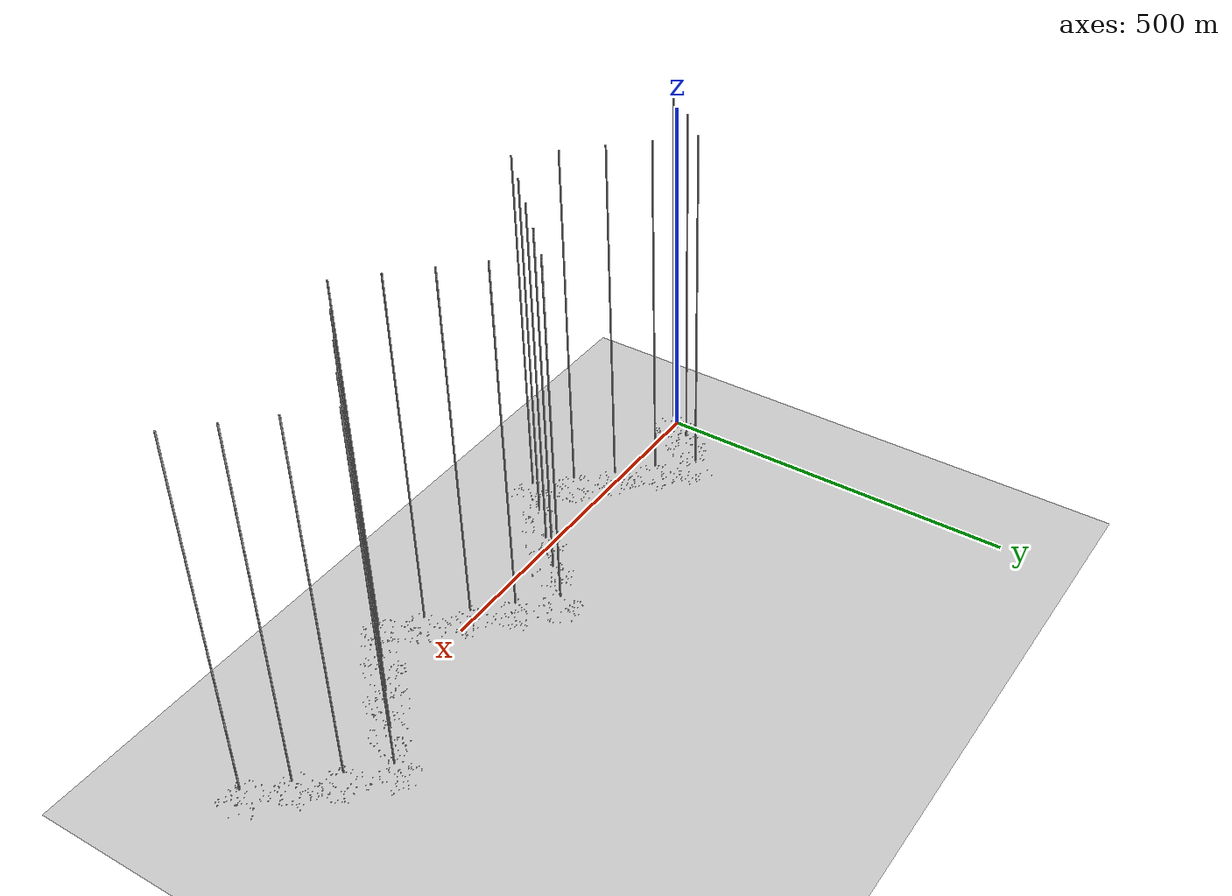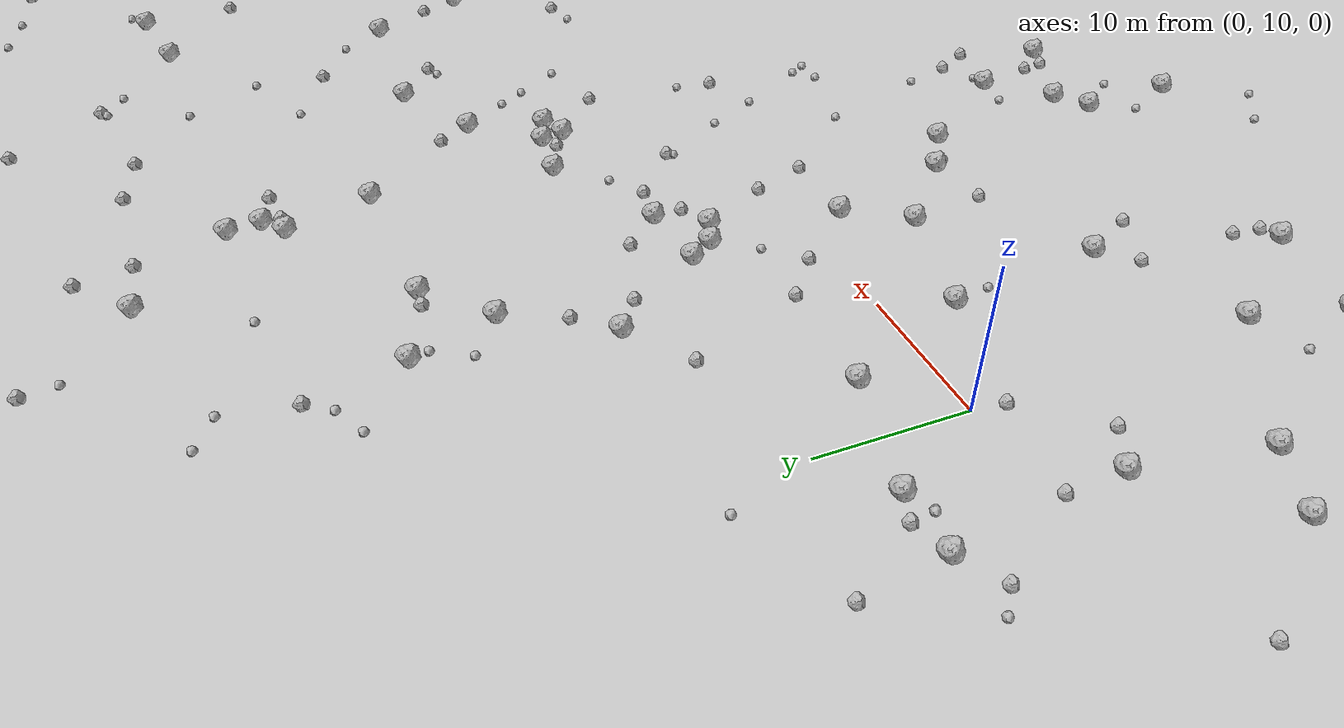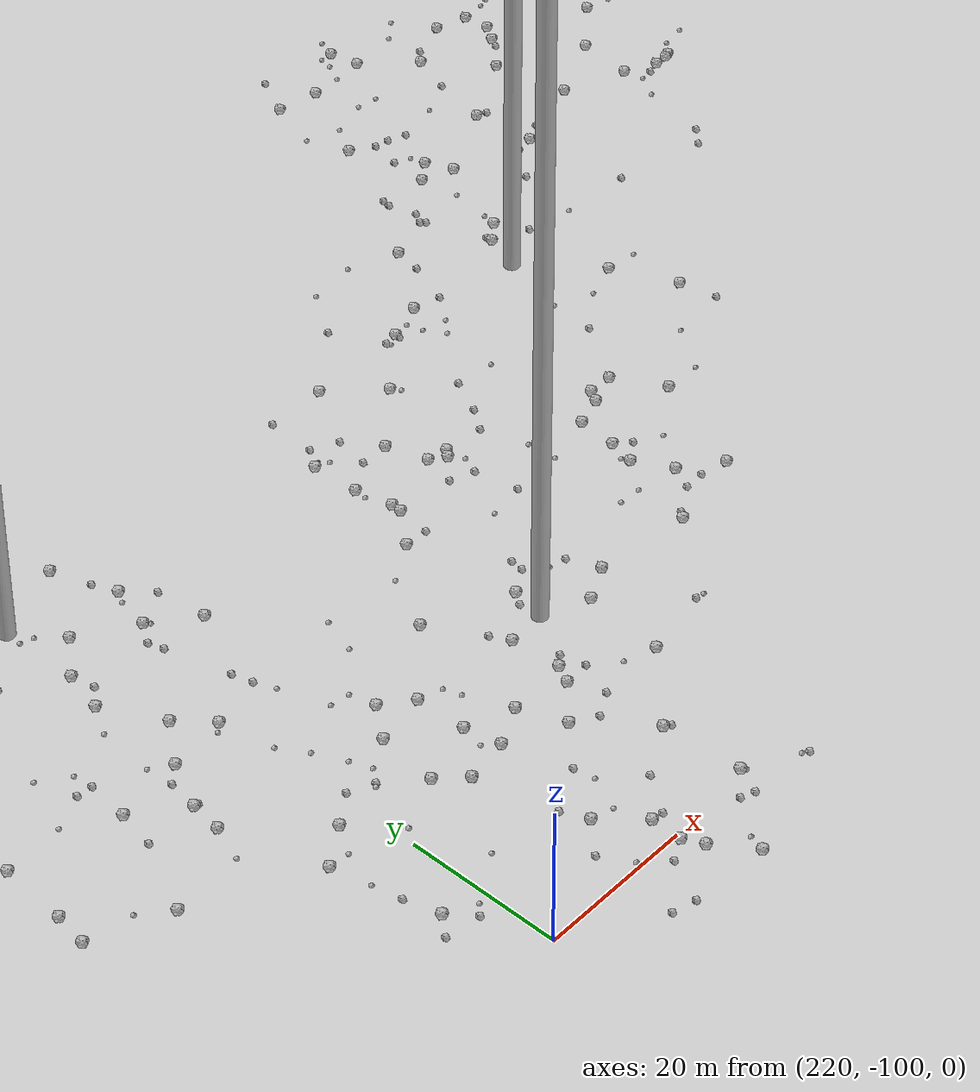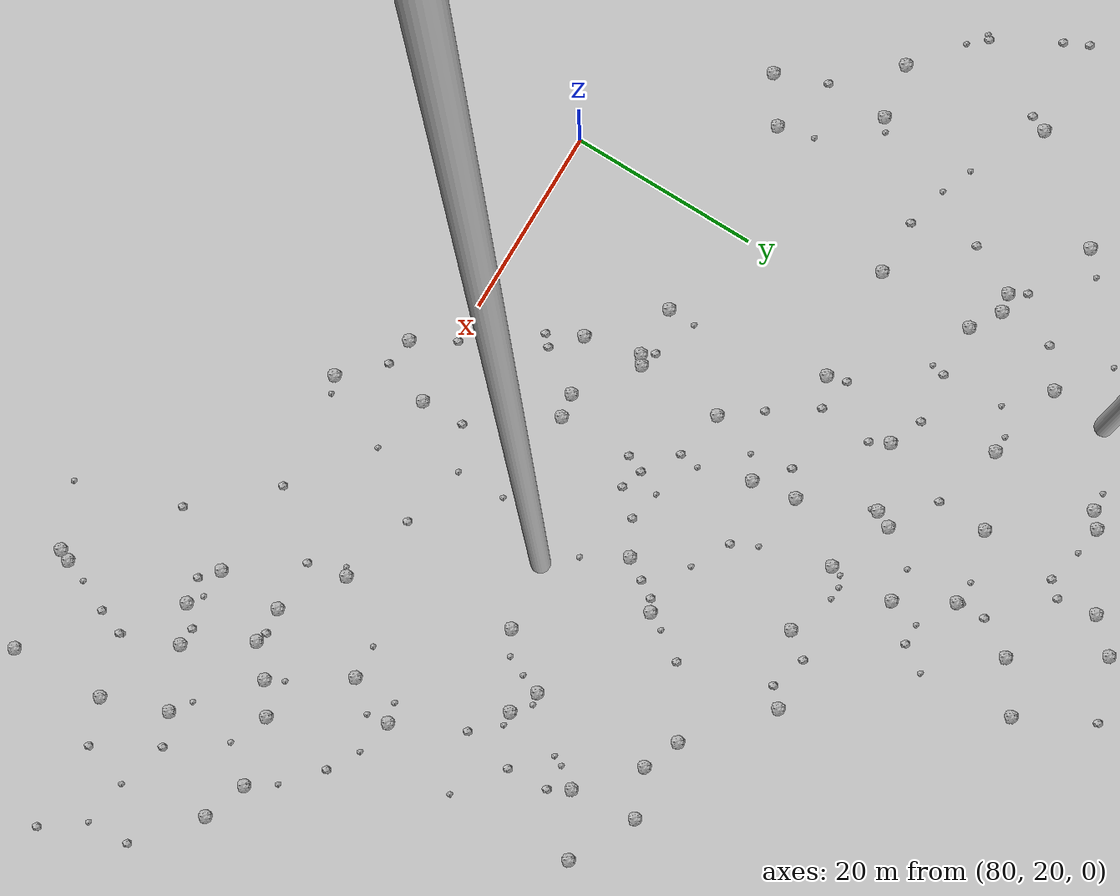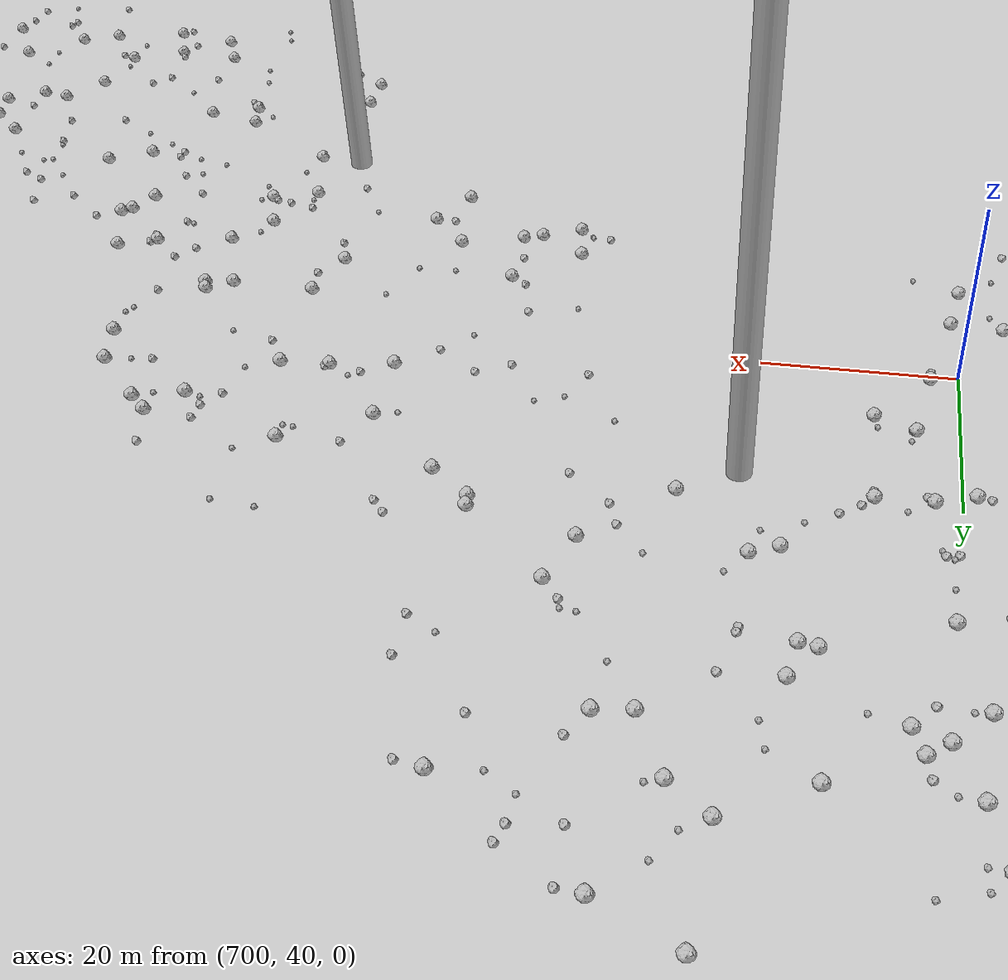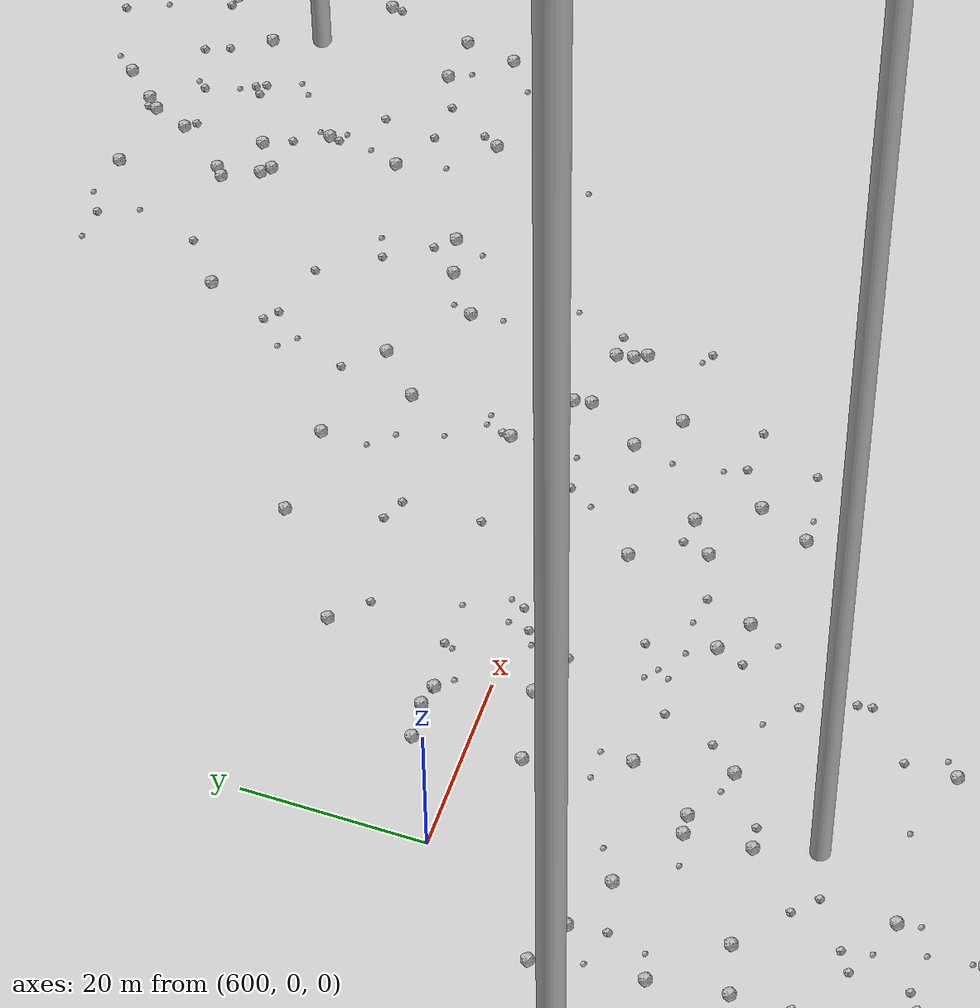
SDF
<sdf version="1.6">
 <world name="default">
  <include><uri>model://custom_ground</uri></include>
  <include><uri>model://sun</uri></include>
  <spherical_coordinates>
   <surface_model>EARTH_WGS84</surface_model>
   <latitude_deg>38.161479</latitude_deg>
   <longitude_deg>-122.454630</longitude_deg>
   <elevation>488.0</elevation>
   <heading_deg>90</heading_deg>
  </spherical_coordinates>
  <model name="rock1_0_0">
   <include><uri>model://rock1</uri><pose>23.90514248581144 -15.776609992672268 0.5 0 0 0</pose></include>
  </model>
  <model name="rock1_0_1">
   <include><uri>model://rock1</uri><pose>24.062548666263957 -22.37770992525668 0.5 0 0 0</pose></include>
  </model>
  <model name="rock1_0_2">
   <include><uri>model://rock1</uri><pose>19.26466761740881 7.367127554734566 0.5 0 0 0</pose></include>
  </model>
  <model name="rock1_0_3">
   <include><uri>model://rock1</uri><pose>9.498476944416563 -5.250346106173144 0.5 0 0 0</pose></include>
  </model>
  <model name="rock1_0_4">
   <include><uri>model://rock1</uri><pose>-3.8976977318944677 16.866911622512205 0.5 0 0 0</pose></include>
  </model>
  <model name="rock1_0_5">
   <include><uri>model://rock1</uri><pose>31.94172232389188 -16.715653397427694 0.5 0 0 0</pose></include>
  </model>
  <model name="rock1_0_6">
   <include><uri>model://rock1</uri><pose>24.478854565243772 -3.426902629569124 0.5 0 0 0</pose></include>
  </model>
  <model name="rock1_0_7">
   <include><uri>model://rock1</uri><pose>29.421577492951286 -10.552254862496937 0.5 0 0 0</pose></include>
  </model>
  <model name="rock1_0_8">
   <include><uri>model://rock1</uri><pose>-6.9936545619670625 5.128483801502298 0.5 0 0 0</pose></include>
  </model>
  <model name="rock1_0_9">
   <include><uri>model://rock1</uri><pose>13.553108611587476 25.226569998773982 0.5 0 0 0</pose></include>
  </model>
  <model name="rock1_0_10">
   <include><uri>model://rock1</uri><pose>-13.872759898773555 -6.137383635538246 0.5 0 0 0</pose></include>
  </model>
  <model name="rock1_0_11">
   <include><uri>model://rock1</uri><pose>-13.1394932801294 -1.5010698386584096 0.5 0 0 0</pose></include>
  </model>
  <model name="rock1_0_12">
   <include><uri>model://rock1</uri><pose>-8.408873832621174 16.891115773531894 0.5 0 0 0</pose></include>
  </model>
  <model name="rock1_0_13">
   <include><uri>model://rock1</uri><pose>21.20148329498128 15.84222829981411 0.5 0 0 0</pose></include>
  </model>
  <model name="rock1_0_14">
   <include><uri>model://rock1</uri><pose>21.454445798479398 -1.3343171631813036 0.5 0 0 0</pose></include>
  </model>
  <model name="rock1_0_15">
   <include><uri>model://rock1</uri><pose>-1.089683898890744 -15.893842803204794 0.5 0 0 0</pose></include>
  </model>
  <model name="rock1_0_16">
   <include><uri>model://rock1</uri><pose>18.347664019257643 18.383973501463053 0.5 0 0 0</pose></include>
  </model>
  <model name="rock1_0_17">
   <include><uri>model://rock1</uri><pose>-11.060439580061969 -10.285798714422906 0.5 0 0 0</pose></include>
  </model>
  <model name="rock1_0_18">
   <include><uri>model://rock1</uri><pose>8.442152969146182 5.593030265820673 0.5 0 0 0</pose></include>
  </model>
  <model name="rock1_0_19">
   <include><uri>model://rock1</uri><pose>-4.7624591109978915 -18.244246839159466 0.5 0 0 0</pose></include>
  </model>
  <model name="rock1_0_20">
   <include><uri>model://rock1</uri><pose>19.401934575711216 16.643141567928872 0.5 0 0 0</pose></include>
  </model>
  <model name="rock1_0_21">
   <include><uri>model://rock1</uri><pose>4.497002273492988 14.609899977009633 0.5 0 0 0</pose></include>
  </model>
  <model name="rock1_0_22">
   <include><uri>model://rock1</uri><pose>6.170723235934371 -17.154163934171493 0.5 0 0 0</pose></include>
  </model>
  <model name="rock1_0_23">
   <include><uri>model://rock1</uri><pose>-8.576273701318122 -3.5485500679403046 0.5 0 0 0</pose></include>
  </model>
  <model name="rock1_0_24">
   <include><uri>model://rock1</uri><pose>25.96695102715183 -14.200774754953787 0.5 0 0 0</pose></include>
  </model>
  <model name="rock1_0_25">
   <include><uri>model://rock1</uri><pose>16.59132923096994 3.333806554088234 0.5 0 0 0</pose></include>
  </model>
  <model name="rock1_0_26">
   <include><uri>model://rock1</uri><pose>0.6459155607628944 -9.634874376459607 0.5 0 0 0</pose></include>
  </model>
  <model name="rock2_0_0">
   <include><uri>model://rock2</uri><pose>32.30616476708222 -8.924000438733266 0.3 0 0 0</pose></include>
  </model>
  <model name="rock2_0_1">
   <include><uri>model://rock2</uri><pose>-1.0612061455158504 -19.86772602399803 0.3 0 0 0</pose></include>
  </model>
  <model name="rock2_0_2">
   <include><uri>model://rock2</uri><pose>23.078787285256567 16.915643389325453 0.3 0 0 0</pose></include>
  </model>
  <model name="rock2_0_3">
   <include><uri>model://rock2</uri><pose>7.185711933578595 -16.44457044044877 0.3 0 0 0</pose></include>
  </model>
  <model name="rock2_0_4">
   <include><uri>model://rock2</uri><pose>-4.26046943274577 3.5204913949392704 0.3 0 0 0</pose></include>
  </model>
  <model name="rock2_0_5">
   <include><uri>model://rock2</uri><pose>23.254146154322385 11.205621321905355 0.3 0 0 0</pose></include>
  </model>
  <model name="rock2_0_6">
   <include><uri>model://rock2</uri><pose>11.2030750738626 -8.892081518628753 0.3 0 0 0</pose></include>
  </model>
  <model name="rock2_0_7">
   <include><uri>model://rock2</uri><pose>-15.296130021034877 -9.714030185738284 0.3 0 0 0</pose></include>
  </model>
  <model name="rock2_0_8">
   <include><uri>model://rock2</uri><pose>7.419158112340991 -14.495429219400325 0.3 0 0 0</pose></include>
  </model>
  <model name="rock2_0_9">
   <include><uri>model://rock2</uri><pose>36.86140968460093 8.229020657344442 0.3 0 0 0</pose></include>
  </model>
  <model name="rock2_0_10">
   <include><uri>model://rock2</uri><pose>9.254284133685001 22.369434763716278 0.3 0 0 0</pose></include>
  </model>
  <model name="rock2_0_11">
   <include><uri>model://rock2</uri><pose>-0.4052610552809526 8.019389821687177 0.3 0 0 0</pose></include>
  </model>
  <model name="rock2_0_12">
   <include><uri>model://rock2</uri><pose>-12.352176524135752 -5.242946420622573 0.3 0 0 0</pose></include>
  </model>
  <model name="rock2_0_13">
   <include><uri>model://rock2</uri><pose>17.061243782203846 -1.8883533749555141 0.3 0 0 0</pose></include>
  </model>
  <model name="rock2_0_14">
   <include><uri>model://rock2</uri><pose>24.520232445384316 7.459599209034792 0.3 0 0 0</pose></include>
  </model>
  <model name="rock2_0_15">
   <include><uri>model://rock2</uri><pose>-18.828745005168837 5.716877561441294 0.3 0 0 0</pose></include>
  </model>
  <model name="rock2_0_16">
   <include><uri>model://rock2</uri><pose>15.282183353533831 11.772567445829203 0.3 0 0 0</pose></include>
  </model>
  <model name="rock2_0_17">
   <include><uri>model://rock2</uri><pose>33.50856588868285 -11.270543672061947 0.3 0 0 0</pose></include>
  </model>
  <model name="rock2_0_18">
   <include><uri>model://rock2</uri><pose>7.314118963043498 -7.276590151645291 0.3 0 0 0</pose></include>
  </model>
  <model name="rock2_0_19">
   <include><uri>model://rock2</uri><pose>-9.397347539297522 22.761748379742535 0.3 0 0 0</pose></include>
  </model>
  <model name="rock2_0_20">
   <include><uri>model://rock2</uri><pose>12.401107659494244 14.251508081529977 0.3 0 0 0</pose></include>
  </model>
  <model name="rock2_0_21">
   <include><uri>model://rock2</uri><pose>29.88710672770015 -14.523434083755633 0.3 0 0 0</pose></include>
  </model>
  <model name="rock2_0_22">
   <include><uri>model://rock2</uri><pose>29.459380678787625 15.066071057537954 0.3 0 0 0</pose></include>
  </model>
  <model name="rock2_0_23">
   <include><uri>model://rock2</uri><pose>-11.29419561924662 15.308042618079895 0.3 0 0 0</pose></include>
  </model>
  <model name="rock2_0_24">
   <include><uri>model://rock2</uri><pose>-7.299938241637456 9.184068201793757 0.3 0 0 0</pose></include>
  </model>
  <model name="rock2_0_25">
   <include><uri>model://rock2</uri><pose>30.09931239799326 -16.049530003374965 0.3 0 0 0</pose></include>
  </model>
  <model name="rock2_0_26">
   <include><uri>model://rock2</uri><pose>-6.004776256208981 17.66972991553162 0.3 0 0 0</pose></include>
  </model>
  <model name="rock3_0_0">
   <include><uri>model://rock3</uri><pose>25.86657156645606 -18.753002055815145 0.2 0 0 0</pose></include>
  </model>
  <model name="rock3_0_1">
   <include><uri>model://rock3</uri><pose>-3.159205451215648 -10.89454419106223 0.2 0 0 0</pose></include>
  </model>
  <model name="rock3_0_2">
   <include><uri>model://rock3</uri><pose>17.40953230557073 13.950407362589822 0.2 0 0 0</pose></include>
  </model>
  <model name="rock3_0_3">
   <include><uri>model://rock3</uri><pose>26.871188802014558 -10.28639626866536 0.2 0 0 0</pose></include>
  </model>
  <model name="rock3_0_4">
   <include><uri>model://rock3</uri><pose>22.222023410509003 -18.73594644117499 0.2 0 0 0</pose></include>
  </model>
  <model name="rock3_0_5">
   <include><uri>model://rock3</uri><pose>23.85044268488356 -15.854169367772979 0.2 0 0 0</pose></include>
  </model>
  <model name="rock3_0_6">
   <include><uri>model://rock3</uri><pose>-5.76801378556274 15.979278366247378 0.2 0 0 0</pose></include>
  </model>
  <model name="rock3_0_7">
   <include><uri>model://rock3</uri><pose>-0.41517145102861974 -19.076126693718315 0.2 0 0 0</pose></include>
  </model>
  <model name="rock3_0_8">
   <include><uri>model://rock3</uri><pose>29.352678654066594 1.848030815742142 0.2 0 0 0</pose></include>
  </model>
  <model name="rock3_0_9">
   <include><uri>model://rock3</uri><pose>31.571709674600825 -5.792991380420425 0.2 0 0 0</pose></include>
  </model>
  <model name="rock3_0_10">
   <include><uri>model://rock3</uri><pose>9.496916427679984 -26.76207077281906 0.2 0 0 0</pose></include>
  </model>
  <model name="rock3_0_11">
   <include><uri>model://rock3</uri><pose>36.64075866637953 0.6071230862160597 0.2 0 0 0</pose></include>
  </model>
  <model name="rock3_0_12">
   <include><uri>model://rock3</uri><pose>8.716146539063018 2.9864275665033517 0.2 0 0 0</pose></include>
  </model>
  <model name="rock3_0_13">
   <include><uri>model://rock3</uri><pose>20.70884072252165 -27.648700829823287 0.2 0 0 0</pose></include>
  </model>
  <model name="rock3_0_14">
   <include><uri>model://rock3</uri><pose>34.81159477735602 0.49354304213481726 0.2 0 0 0</pose></include>
  </model>
  <model name="rock3_0_15">
   <include><uri>model://rock3</uri><pose>-2.0575609582297574 25.75250774178636 0.2 0 0 0</pose></include>
  </model>
  <model name="rock3_0_16">
   <include><uri>model://rock3</uri><pose>-12.85835022294733 16.499489728339896 0.2 0 0 0</pose></include>
  </model>
  <model name="rock3_0_17">
   <include><uri>model://rock3</uri><pose>7.0311009851401565 -29.36834621869092 0.2 0 0 0</pose></include>
  </model>
  <model name="rock3_0_18">
   <include><uri>model://rock3</uri><pose>21.771771584969954 -2.26247250198686 0.2 0 0 0</pose></include>
  </model>
  <model name="rock3_0_19">
   <include><uri>model://rock3</uri><pose>-5.702797993029339 15.954991053566914 0.2 0 0 0</pose></include>
  </model>
  <model name="rock3_0_20">
   <include><uri>model://rock3</uri><pose>2.0782490250298764 -23.724322403019407 0.2 0 0 0</pose></include>
  </model>
  <model name="rock3_0_21">
   <include><uri>model://rock3</uri><pose>36.04568914905599 1.7087110787532396 0.2 0 0 0</pose></include>
  </model>
  <model name="rock3_0_22">
   <include><uri>model://rock3</uri><pose>17.827801428712682 -25.58969793073608 0.2 0 0 0</pose></include>
  </model>
  <model name="rock3_0_23">
   <include><uri>model://rock3</uri><pose>-9.502178383439384 -8.107182008089467 0.2 0 0 0</pose></include>
  </model>
  <model name="rock3_0_24">
   <include><uri>model://rock3</uri><pose>33.5090195196125 6.604541267216781 0.2 0 0 0</pose></include>
  </model>
  <model name="rock3_0_25">
   <include><uri>model://rock3</uri><pose>31.86077061844596 10.175480890280312 0.2 0 0 0</pose></include>
  </model>
  <model name="rock3_0_26">
   <include><uri>model://rock3</uri><pose>30.241678158029828 -10.310555947709897 0.2 0 0 0</pose></include>
  </model>
  <model name="rock1_1_0">
   <include><uri>model://rock1</uri><pose>56.65688458287951 21.630027258252248 0.5 0 0 0</pose></include>
  </model>
  <model name="rock1_1_1">
   <include><uri>model://rock1</uri><pose>36.60887359926889 21.464202379892463 0.5 0 0 0</pose></include>
  </model>
  <model name="rock1_1_2">
   <include><uri>model://rock1</uri><pose>63.95400084840171 33.21983883816674 0.5 0 0 0</pose></include>
  </model>
  <model name="rock1_1_3">
   <include><uri>model://rock1</uri><pose>30.614069243709356 59.388300419000565 0.5 0 0 0</pose></include>
  </model>
  <model name="rock1_1_4">
   <include><uri>model://rock1</uri><pose>21.530571276748102 35.254338399793305 0.5 0 0 0</pose></include>
  </model>
  <model name="rock1_1_5">
   <include><uri>model://rock1</uri><pose>53.96502938339451 28.544155341389835 0.5 0 0 0</pose></include>
  </model>
  <model name="rock1_1_6">
   <include><uri>model://rock1</uri><pose>30.88619026452426 22.88939253853606 0.5 0 0 0</pose></include>
  </model>
  <model name="rock1_1_7">
   <include><uri>model://rock1</uri><pose>26.2960555101412 51.5454606538042 0.5 0 0 0</pose></include>
  </model>
  <model name="rock1_1_8">
   <include><uri>model://rock1</uri><pose>32.97617574941335 68.43613989080265 0.5 0 0 0</pose></include>
  </model>
  <model name="rock1_1_9">
   <include><uri>model://rock1</uri><pose>17.586128481280653 31.626551556343568 0.5 0 0 0</pose></include>
  </model>
  <model name="rock1_1_10">
   <include><uri>model://rock1</uri><pose>31.890379767441207 44.78896034935239 0.5 0 0 0</pose></include>
  </model>
  <model name="rock1_1_11">
   <include><uri>model://rock1</uri><pose>32.13597703780091 42.50078551022702 0.5 0 0 0</pose></include>
  </model>
  <model name="rock1_1_12">
   <include><uri>model://rock1</uri><pose>30.695910675210886 41.28246619500288 0.5 0 0 0</pose></include>
  </model>
  <model name="rock1_1_13">
   <include><uri>model://rock1</uri><pose>34.85093976709551 20.688069312649848 0.5 0 0 0</pose></include>
  </model>
  <model name="rock1_1_14">
   <include><uri>model://rock1</uri><pose>34.54319849332542 22.31352926168345 0.5 0 0 0</pose></include>
  </model>
  <model name="rock1_1_15">
   <include><uri>model://rock1</uri><pose>23.224176379876262 18.860508892768713 0.5 0 0 0</pose></include>
  </model>
  <model name="rock1_1_16">
   <include><uri>model://rock1</uri><pose>43.89935457900827 29.522069688202166 0.5 0 0 0</pose></include>
  </model>
  <model name="rock1_1_17">
   <include><uri>model://rock1</uri><pose>43.703199792996685 69.23189325593519 0.5 0 0 0</pose></include>
  </model>
  <model name="rock1_1_18">
   <include><uri>model://rock1</uri><pose>38.180664026516084 26.542191964359212 0.5 0 0 0</pose></include>
  </model>
  <model name="rock1_1_19">
   <include><uri>model://rock1</uri><pose>15.708440304690225 37.533616114222085 0.5 0 0 0</pose></include>
  </model>
  <model name="rock1_1_20">
   <include><uri>model://rock1</uri><pose>54.67501565183822 59.854569157448616 0.5 0 0 0</pose></include>
  </model>
  <model name="rock1_1_21">
   <include><uri>model://rock1</uri><pose>39.90059248012389 62.3375482964421 0.5 0 0 0</pose></include>
  </model>
  <model name="rock1_1_22">
   <include><uri>model://rock1</uri><pose>32.360823271565906 35.2288111079033 0.5 0 0 0</pose></include>
  </model>
  <model name="rock1_1_23">
   <include><uri>model://rock1</uri><pose>61.93935760137199 45.225100505519656 0.5 0 0 0</pose></include>
  </model>
  <model name="rock1_1_24">
   <include><uri>model://rock1</uri><pose>56.203833927041345 44.33437237972534 0.5 0 0 0</pose></include>
  </model>
  <model name="rock1_1_25">
   <include><uri>model://rock1</uri><pose>34.487333134541345 66.3890419684796 0.5 0 0 0</pose></include>
  </model>
  <model name="rock1_1_26">
   <include><uri>model://rock1</uri><pose>68.4015980601236 36.403868323242776 0.5 0 0 0</pose></include>
  </model>
  <model name="rock2_1_0">
   <include><uri>model://rock2</uri><pose>15.678740909876005 23.44094291478771 0.3 0 0 0</pose></include>
  </model>
  <model name="rock2_1_1">
   <include><uri>model://rock2</uri><pose>55.558832197175924 24.42002377745542 0.3 0 0 0</pose></include>
  </model>
  <model name="rock2_1_2">
   <include><uri>model://rock2</uri><pose>53.956043284260275 58.122460524522396 0.3 0 0 0</pose></include>
  </model>
  <model name="rock2_1_3">
   <include><uri>model://rock2</uri><pose>20.606505308893723 58.5664935126029 0.3 0 0 0</pose></include>
  </model>
  <model name="rock2_1_4">
   <include><uri>model://rock2</uri><pose>48.53338898541058 34.34825830829914 0.3 0 0 0</pose></include>
  </model>
  <model name="rock2_1_5">
   <include><uri>model://rock2</uri><pose>58.349439959478616 17.65798479396421 0.3 0 0 0</pose></include>
  </model>
  <model name="rock2_1_6">
   <include><uri>model://rock2</uri><pose>33.29326839177331 21.67406095667552 0.3 0 0 0</pose></include>
  </model>
  <model name="rock2_1_7">
   <include><uri>model://rock2</uri><pose>20.007961721979164 35.43388655702044 0.3 0 0 0</pose></include>
  </model>
  <model name="rock2_1_8">
   <include><uri>model://rock2</uri><pose>38.148676899730845 17.274339739604873 0.3 0 0 0</pose></include>
  </model>
  <model name="rock2_1_9">
   <include><uri>model://rock2</uri><pose>49.500796288275005 50.27024812235805 0.3 0 0 0</pose></include>
  </model>
  <model name="rock2_1_10">
   <include><uri>model://rock2</uri><pose>37.96909971479036 50.36185911260741 0.3 0 0 0</pose></include>
  </model>
  <model name="rock2_1_11">
   <include><uri>model://rock2</uri><pose>20.80956572290942 21.488618780739394 0.3 0 0 0</pose></include>
  </model>
  <model name="rock2_1_12">
   <include><uri>model://rock2</uri><pose>36.84918282349581 28.898203044877743 0.3 0 0 0</pose></include>
  </model>
  <model name="rock2_1_13">
   <include><uri>model://rock2</uri><pose>52.244056768438824 14.83241027347997 0.3 0 0 0</pose></include>
  </model>
  <model name="rock2_1_14">
   <include><uri>model://rock2</uri><pose>44.663040002071824 59.32806377639353 0.3 0 0 0</pose></include>
  </model>
  <model name="rock2_1_15">
   <include><uri>model://rock2</uri><pose>29.73284844930557 54.54480453788486 0.3 0 0 0</pose></include>
  </model>
  <model name="rock2_1_16">
   <include><uri>model://rock2</uri><pose>46.700885961629794 26.811478769704237 0.3 0 0 0</pose></include>
  </model>
  <model name="rock2_1_17">
   <include><uri>model://rock2</uri><pose>59.82593408005918 21.732876369614445 0.3 0 0 0</pose></include>
  </model>
  <model name="rock2_1_18">
   <include><uri>model://rock2</uri><pose>14.171644552603444 44.08200481755999 0.3 0 0 0</pose></include>
  </model>
  <model name="rock2_1_19">
   <include><uri>model://rock2</uri><pose>31.927503730757056 41.25118272508925 0.3 0 0 0</pose></include>
  </model>
  <model name="rock2_1_20">
   <include><uri>model://rock2</uri><pose>25.798555988710444 18.39319040755944 0.3 0 0 0</pose></include>
  </model>
  <model name="rock2_1_21">
   <include><uri>model://rock2</uri><pose>30.379822664782424 50.809335837874 0.3 0 0 0</pose></include>
  </model>
  <model name="rock2_1_22">
   <include><uri>model://rock2</uri><pose>45.826100709082624 56.88137673492493 0.3 0 0 0</pose></include>
  </model>
  <model name="rock2_1_23">
   <include><uri>model://rock2</uri><pose>15.540589315319814 27.64064169636405 0.3 0 0 0</pose></include>
  </model>
  <model name="rock2_1_24">
   <include><uri>model://rock2</uri><pose>34.52542270203428 41.443152894557 0.3 0 0 0</pose></include>
  </model>
  <model name="rock2_1_25">
   <include><uri>model://rock2</uri><pose>41.87983565010862 49.020823037284714 0.3 0 0 0</pose></include>
  </model>
  <model name="rock2_1_26">
   <include><uri>model://rock2</uri><pose>61.89053337816474 38.6108038050432 0.3 0 0 0</pose></include>
  </model>
  <model name="rock3_1_0">
   <include><uri>model://rock3</uri><pose>51.05363982919497 48.46369859277459 0.2 0 0 0</pose></include>
  </model>
  <model name="rock3_1_1">
   <include><uri>model://rock3</uri><pose>49.0991659025746 49.87940038031952 0.2 0 0 0</pose></include>
  </model>
  <model name="rock3_1_2">
   <include><uri>model://rock3</uri><pose>12.864255199367369 50.28224832070893 0.2 0 0 0</pose></include>
  </model>
  <model name="rock3_1_3">
   <include><uri>model://rock3</uri><pose>28.04879857949192 19.871885185580325 0.2 0 0 0</pose></include>
  </model>
  <model name="rock3_1_4">
   <include><uri>model://rock3</uri><pose>22.290501763163093 44.95152821387734 0.2 0 0 0</pose></include>
  </model>
  <model name="rock3_1_5">
   <include><uri>model://rock3</uri><pose>42.6916521065889 18.406193178455712 0.2 0 0 0</pose></include>
  </model>
  <model name="rock3_1_6">
   <include><uri>model://rock3</uri><pose>45.83538404980111 26.345843450823356 0.2 0 0 0</pose></include>
  </model>
  <model name="rock3_1_7">
   <include><uri>model://rock3</uri><pose>63.17132223416991 46.108136421531434 0.2 0 0 0</pose></include>
  </model>
  <model name="rock3_1_8">
   <include><uri>model://rock3</uri><pose>40.98392584611479 21.461093522994506 0.2 0 0 0</pose></include>
  </model>
  <model name="rock3_1_9">
   <include><uri>model://rock3</uri><pose>20.310080846519316 60.89697098067973 0.2 0 0 0</pose></include>
  </model>
  <model name="rock3_1_10">
   <include><uri>model://rock3</uri><pose>15.887213134326132 36.189959195880405 0.2 0 0 0</pose></include>
  </model>
  <model name="rock3_1_11">
   <include><uri>model://rock3</uri><pose>52.059615086792874 31.66799365090939 0.2 0 0 0</pose></include>
  </model>
  <model name="rock3_1_12">
   <include><uri>model://rock3</uri><pose>49.21727935158025 39.155274799093135 0.2 0 0 0</pose></include>
  </model>
  <model name="rock3_1_13">
   <include><uri>model://rock3</uri><pose>37.347783012851494 10.601901734891776 0.2 0 0 0</pose></include>
  </model>
  <model name="rock3_1_14">
   <include><uri>model://rock3</uri><pose>62.068848118506196 55.567033467848354 0.2 0 0 0</pose></include>
  </model>
  <model name="rock3_1_15">
   <include><uri>model://rock3</uri><pose>13.077512003836642 42.43280591381802 0.2 0 0 0</pose></include>
  </model>
  <model name="rock3_1_16">
   <include><uri>model://rock3</uri><pose>29.289863494997853 14.577962554121378 0.2 0 0 0</pose></include>
  </model>
  <model name="rock3_1_17">
   <include><uri>model://rock3</uri><pose>50.1561505364548 14.230810369271353 0.2 0 0 0</pose></include>
  </model>
  <model name="rock3_1_18">
   <include><uri>model://rock3</uri><pose>14.497278991811164 33.85545627702949 0.2 0 0 0</pose></include>
  </model>
  <model name="rock3_1_19">
   <include><uri>model://rock3</uri><pose>46.83802985759351 44.42885811862695 0.2 0 0 0</pose></include>
  </model>
  <model name="rock3_1_20">
   <include><uri>model://rock3</uri><pose>10.853554875541887 41.42964524262939 0.2 0 0 0</pose></include>
  </model>
  <model name="rock3_1_21">
   <include><uri>model://rock3</uri><pose>20.92883817933666 56.22655949652846 0.2 0 0 0</pose></include>
  </model>
  <model name="rock3_1_22">
   <include><uri>model://rock3</uri><pose>44.10853537587906 37.05963595290203 0.2 0 0 0</pose></include>
  </model>
  <model name="rock3_1_23">
   <include><uri>model://rock3</uri><pose>15.083295484214862 48.67231609169138 0.2 0 0 0</pose></include>
  </model>
  <model name="rock3_1_24">
   <include><uri>model://rock3</uri><pose>67.42638593556094 40.21047761496381 0.2 0 0 0</pose></include>
  </model>
  <model name="rock3_1_25">
   <include><uri>model://rock3</uri><pose>39.9813364345584 23.29144115720441 0.2 0 0 0</pose></include>
  </model>
  <model name="rock3_1_26">
   <include><uri>model://rock3</uri><pose>44.265911033542125 65.72676789253882 0.2 0 0 0</pose></include>
  </model>
  <model name="rock1_2_0">
   <include><uri>model://rock1</uri><pose>76.9645957130577 74.42245115209431 0.5 0 0 0</pose></include>
  </model>
  <model name="rock1_2_1">
   <include><uri>model://rock1</uri><pose>86.98356771424082 89.54751552695531 0.5 0 0 0</pose></include>
  </model>
  <model name="rock1_2_2">
   <include><uri>model://rock1</uri><pose>75.65062438048732 53.22371670337996 0.5 0 0 0</pose></include>
  </model>
  <model name="rock1_2_3">
   <include><uri>model://rock1</uri><pose>100.57589029738926 77.06741236148285 0.5 0 0 0</pose></include>
  </model>
  <model name="rock1_2_4">
   <include><uri>model://rock1</uri><pose>92.65730099924559 94.86663026800231 0.5 0 0 0</pose></include>
  </model>
  <model name="rock1_2_5">
   <include><uri>model://rock1</uri><pose>86.81535895009736 85.34474858332317 0.5 0 0 0</pose></include>
  </model>
  <model name="rock1_2_6">
   <include><uri>model://rock1</uri><pose>90.16504255864331 62.97439501663972 0.5 0 0 0</pose></include>
  </model>
  <model name="rock1_2_7">
   <include><uri>model://rock1</uri><pose>87.67967308808574 53.912975968885654 0.5 0 0 0</pose></include>
  </model>
  <model name="rock1_2_8">
   <include><uri>model://rock1</uri><pose>85.39580543515495 72.51526670864499 0.5 0 0 0</pose></include>
  </model>
  <model name="rock1_2_9">
   <include><uri>model://rock1</uri><pose>96.7804535240443 65.45249501697309 0.5 0 0 0</pose></include>
  </model>
  <model name="rock1_2_10">
   <include><uri>model://rock1</uri><pose>52.93578875789311 71.5861487245438 0.5 0 0 0</pose></include>
  </model>
  <model name="rock1_2_11">
   <include><uri>model://rock1</uri><pose>103.996608109868 64.38850927500006 0.5 0 0 0</pose></include>
  </model>
  <model name="rock1_2_12">
   <include><uri>model://rock1</uri><pose>70.92178233704671 65.31457132341839 0.5 0 0 0</pose></include>
  </model>
  <model name="rock1_2_13">
   <include><uri>model://rock1</uri><pose>97.23773243476317 93.01795246262935 0.5 0 0 0</pose></include>
  </model>
  <model name="rock1_2_14">
   <include><uri>model://rock1</uri><pose>92.81571675150006 75.70782541176509 0.5 0 0 0</pose></include>
  </model>
  <model name="rock1_2_15">
   <include><uri>model://rock1</uri><pose>107.5968922468809 87.71261716145244 0.5 0 0 0</pose></include>
  </model>
  <model name="rock1_2_16">
   <include><uri>model://rock1</uri><pose>62.59313027508929 70.06293049462941 0.5 0 0 0</pose></include>
  </model>
  <model name="rock1_2_17">
   <include><uri>model://rock1</uri><pose>72.83309934593072 65.7359223831711 0.5 0 0 0</pose></include>
  </model>
  <model name="rock1_2_18">
   <include><uri>model://rock1</uri><pose>97.60936948603546 67.20455720179658 0.5 0 0 0</pose></include>
  </model>
  <model name="rock1_2_19">
   <include><uri>model://rock1</uri><pose>94.2740726630139 89.713786430888 0.5 0 0 0</pose></include>
  </model>
  <model name="rock1_2_20">
   <include><uri>model://rock1</uri><pose>70.46714064651212 98.68229068627338 0.5 0 0 0</pose></include>
  </model>
  <model name="rock1_2_21">
   <include><uri>model://rock1</uri><pose>51.17967520256795 75.88107083716328 0.5 0 0 0</pose></include>
  </model>
  <model name="rock1_2_22">
   <include><uri>model://rock1</uri><pose>102.76092578106466 84.15406157155473 0.5 0 0 0</pose></include>
  </model>
  <model name="rock1_2_23">
   <include><uri>model://rock1</uri><pose>75.93062354260647 63.720420807971635 0.5 0 0 0</pose></include>
  </model>
  <model name="rock1_2_24">
   <include><uri>model://rock1</uri><pose>103.85623439062675 71.34323110489944 0.5 0 0 0</pose></include>
  </model>
  <model name="rock1_2_25">
   <include><uri>model://rock1</uri><pose>85.3350193937951 84.11190209566891 0.5 0 0 0</pose></include>
  </model>
  <model name="rock1_2_26">
   <include><uri>model://rock1</uri><pose>74.67551386892961 103.22572251609482 0.5 0 0 0</pose></include>
  </model>
  <model name="rock2_2_0">
   <include><uri>model://rock2</uri><pose>103.56192512198265 95.5545671399586 0.3 0 0 0</pose></include>
  </model>
  <model name="rock2_2_1">
   <include><uri>model://rock2</uri><pose>87.0871730306555 55.99959321870491 0.3 0 0 0</pose></include>
  </model>
  <model name="rock2_2_2">
   <include><uri>model://rock2</uri><pose>69.80122672552419 53.16024868739211 0.3 0 0 0</pose></include>
  </model>
  <model name="rock2_2_3">
   <include><uri>model://rock2</uri><pose>79.97552533280994 87.98625381105609 0.3 0 0 0</pose></include>
  </model>
  <model name="rock2_2_4">
   <include><uri>model://rock2</uri><pose>106.82603228759649 74.8115625170297 0.3 0 0 0</pose></include>
  </model>
  <model name="rock2_2_5">
   <include><uri>model://rock2</uri><pose>69.82488011627095 67.08597226037762 0.3 0 0 0</pose></include>
  </model>
  <model name="rock2_2_6">
   <include><uri>model://rock2</uri><pose>94.89838442125529 85.59270457914133 0.3 0 0 0</pose></include>
  </model>
  <model name="rock2_2_7">
   <include><uri>model://rock2</uri><pose>72.75296466333342 86.90163318832157 0.3 0 0 0</pose></include>
  </model>
  <model name="rock2_2_8">
   <include><uri>model://rock2</uri><pose>68.58616807210231 92.56999265514766 0.3 0 0 0</pose></include>
  </model>
  <model name="rock2_2_9">
   <include><uri>model://rock2</uri><pose>51.05064965405504 84.10645862264482 0.3 0 0 0</pose></include>
  </model>
  <model name="rock2_2_10">
   <include><uri>model://rock2</uri><pose>69.14434087967109 93.44949052978086 0.3 0 0 0</pose></include>
  </model>
  <model name="rock2_2_11">
   <include><uri>model://rock2</uri><pose>86.66486637442101 64.52091302477857 0.3 0 0 0</pose></include>
  </model>
  <model name="rock2_2_12">
   <include><uri>model://rock2</uri><pose>93.50873113878191 84.08413350805591 0.3 0 0 0</pose></include>
  </model>
  <model name="rock2_2_13">
   <include><uri>model://rock2</uri><pose>70.27021248111222 104.39795247888183 0.3 0 0 0</pose></include>
  </model>
  <model name="rock2_2_14">
   <include><uri>model://rock2</uri><pose>53.138224177077745 75.91070275234372 0.3 0 0 0</pose></include>
  </model>
  <model name="rock2_2_15">
   <include><uri>model://rock2</uri><pose>73.58153472876562 90.83273238853184 0.3 0 0 0</pose></include>
  </model>
  <model name="rock2_2_16">
   <include><uri>model://rock2</uri><pose>73.27763039917718 82.77148641272379 0.3 0 0 0</pose></include>
  </model>
  <model name="rock2_2_17">
   <include><uri>model://rock2</uri><pose>60.51329258643841 96.08100533389918 0.3 0 0 0</pose></include>
  </model>
  <model name="rock2_2_18">
   <include><uri>model://rock2</uri><pose>100.43591122333525 80.27889235870038 0.3 0 0 0</pose></include>
  </model>
  <model name="rock2_2_19">
   <include><uri>model://rock2</uri><pose>73.21313944602056 71.66845111044587 0.3 0 0 0</pose></include>
  </model>
  <model name="rock2_2_20">
   <include><uri>model://rock2</uri><pose>63.73833905937816 97.43086851784017 0.3 0 0 0</pose></include>
  </model>
  <model name="rock2_2_21">
   <include><uri>model://rock2</uri><pose>87.91926843858045 91.7693335828604 0.3 0 0 0</pose></include>
  </model>
  <model name="rock2_2_22">
   <include><uri>model://rock2</uri><pose>92.67072607414374 70.30250780237154 0.3 0 0 0</pose></include>
  </model>
  <model name="rock2_2_23">
   <include><uri>model://rock2</uri><pose>91.17172666824342 61.062545673008 0.3 0 0 0</pose></include>
  </model>
  <model name="rock2_2_24">
   <include><uri>model://rock2</uri><pose>81.37606531668078 64.00721523119428 0.3 0 0 0</pose></include>
  </model>
  <model name="rock2_2_25">
   <include><uri>model://rock2</uri><pose>90.71354621887005 55.259695441139726 0.3 0 0 0</pose></include>
  </model>
  <model name="rock2_2_26">
   <include><uri>model://rock2</uri><pose>68.33491644506302 60.086114866748154 0.3 0 0 0</pose></include>
  </model>
  <model name="rock3_2_0">
   <include><uri>model://rock3</uri><pose>83.10078710617262 103.01545967124764 0.2 0 0 0</pose></include>
  </model>
  <model name="rock3_2_1">
   <include><uri>model://rock3</uri><pose>105.42837574479591 66.08466531828299 0.2 0 0 0</pose></include>
  </model>
  <model name="rock3_2_2">
   <include><uri>model://rock3</uri><pose>59.977602984682 99.08015981250551 0.2 0 0 0</pose></include>
  </model>
  <model name="rock3_2_3">
   <include><uri>model://rock3</uri><pose>65.32937292224133 54.25199963962023 0.2 0 0 0</pose></include>
  </model>
  <model name="rock3_2_4">
   <include><uri>model://rock3</uri><pose>90.60971298122104 106.48660280381141 0.2 0 0 0</pose></include>
  </model>
  <model name="rock3_2_5">
   <include><uri>model://rock3</uri><pose>89.79714674682307 84.96135643182251 0.2 0 0 0</pose></include>
  </model>
  <model name="rock3_2_6">
   <include><uri>model://rock3</uri><pose>77.05258144763735 91.57685454706015 0.2 0 0 0</pose></include>
  </model>
  <model name="rock3_2_7">
   <include><uri>model://rock3</uri><pose>83.56995952863673 72.58265792240249 0.2 0 0 0</pose></include>
  </model>
  <model name="rock3_2_8">
   <include><uri>model://rock3</uri><pose>64.78859281392937 72.13091486360932 0.2 0 0 0</pose></include>
  </model>
  <model name="rock3_2_9">
   <include><uri>model://rock3</uri><pose>100.35702873671164 77.66136863607792 0.2 0 0 0</pose></include>
  </model>
  <model name="rock3_2_10">
   <include><uri>model://rock3</uri><pose>86.2875372705538 95.66452311048936 0.2 0 0 0</pose></include>
  </model>
  <model name="rock3_2_11">
   <include><uri>model://rock3</uri><pose>96.88822842052681 64.75809092999435 0.2 0 0 0</pose></include>
  </model>
  <model name="rock3_2_12">
   <include><uri>model://rock3</uri><pose>102.39027487931244 84.41951785866755 0.2 0 0 0</pose></include>
  </model>
  <model name="rock3_2_13">
   <include><uri>model://rock3</uri><pose>100.22973756841606 71.04689727851385 0.2 0 0 0</pose></include>
  </model>
  <model name="rock3_2_14">
   <include><uri>model://rock3</uri><pose>68.69841624358949 79.61521723201491 0.2 0 0 0</pose></include>
  </model>
  <model name="rock3_2_15">
   <include><uri>model://rock3</uri><pose>98.04170020083929 77.2275848210229 0.2 0 0 0</pose></include>
  </model>
  <model name="rock3_2_16">
   <include><uri>model://rock3</uri><pose>86.01619779675298 93.64865467376282 0.2 0 0 0</pose></include>
  </model>
  <model name="rock3_2_17">
   <include><uri>model://rock3</uri><pose>108.5660365728121 77.63510012389628 0.2 0 0 0</pose></include>
  </model>
  <model name="rock3_2_18">
   <include><uri>model://rock3</uri><pose>83.34438609806611 84.01804027945401 0.2 0 0 0</pose></include>
  </model>
  <model name="rock3_2_19">
   <include><uri>model://rock3</uri><pose>81.0327730697419 70.63549609733735 0.2 0 0 0</pose></include>
  </model>
  <model name="rock3_2_20">
   <include><uri>model://rock3</uri><pose>65.16869437490891 76.50912776149055 0.2 0 0 0</pose></include>
  </model>
  <model name="rock3_2_21">
   <include><uri>model://rock3</uri><pose>104.61053581858377 74.72496410658479 0.2 0 0 0</pose></include>
  </model>
  <model name="rock3_2_22">
   <include><uri>model://rock3</uri><pose>81.11906355715732 62.55193549094575 0.2 0 0 0</pose></include>
  </model>
  <model name="rock3_2_23">
   <include><uri>model://rock3</uri><pose>71.75919655307214 78.38471110542127 0.2 0 0 0</pose></include>
  </model>
  <model name="rock3_2_24">
   <include><uri>model://rock3</uri><pose>62.856930643176106 92.97854251443624 0.2 0 0 0</pose></include>
  </model>
  <model name="rock3_2_25">
   <include><uri>model://rock3</uri><pose>54.06783060063584 74.56671715861154 0.2 0 0 0</pose></include>
  </model>
  <model name="rock3_2_26">
   <include><uri>model://rock3</uri><pose>55.693496658973466 92.49762136250246 0.2 0 0 0</pose></include>
  </model>
  <model name="rock1_3_0">
   <include><uri>model://rock1</uri><pose>140.85861773868282 34.339624918619236 0.5 0 0 0</pose></include>
  </model>
  <model name="rock1_3_1">
   <include><uri>model://rock1</uri><pose>130.40085362109642 23.00163481343998 0.5 0 0 0</pose></include>
  </model>
  <model name="rock1_3_2">
   <include><uri>model://rock1</uri><pose>133.50641122098702 44.283384718730204 0.5 0 0 0</pose></include>
  </model>
  <model name="rock1_3_3">
   <include><uri>model://rock1</uri><pose>143.15327250871164 57.10402653442411 0.5 0 0 0</pose></include>
  </model>
  <model name="rock1_3_4">
   <include><uri>model://rock1</uri><pose>131.18081239198 58.74984703888052 0.5 0 0 0</pose></include>
  </model>
  <model name="rock1_3_5">
   <include><uri>model://rock1</uri><pose>126.25395804855746 40.01270488923798 0.5 0 0 0</pose></include>
  </model>
  <model name="rock1_3_6">
   <include><uri>model://rock1</uri><pose>99.99415513093038 57.68263048414838 0.5 0 0 0</pose></include>
  </model>
  <model name="rock1_3_7">
   <include><uri>model://rock1</uri><pose>136.93339602321737 53.634381769242765 0.5 0 0 0</pose></include>
  </model>
  <model name="rock1_3_8">
   <include><uri>model://rock1</uri><pose>138.64861944669684 29.13801588419533 0.5 0 0 0</pose></include>
  </model>
  <model name="rock1_3_9">
   <include><uri>model://rock1</uri><pose>102.73663553771746 32.77101019349603 0.5 0 0 0</pose></include>
  </model>
  <model name="rock1_3_10">
   <include><uri>model://rock1</uri><pose>136.13348224118658 60.64221268651159 0.5 0 0 0</pose></include>
  </model>
  <model name="rock1_3_11">
   <include><uri>model://rock1</uri><pose>96.52048187621587 37.31160906489392 0.5 0 0 0</pose></include>
  </model>
  <model name="rock1_3_12">
   <include><uri>model://rock1</uri><pose>130.41723935621167 45.613699349925625 0.5 0 0 0</pose></include>
  </model>
  <model name="rock1_3_13">
   <include><uri>model://rock1</uri><pose>97.01902944292127 30.813867946040293 0.5 0 0 0</pose></include>
  </model>
  <model name="rock1_3_14">
   <include><uri>model://rock1</uri><pose>106.64644926410338 15.860176308103384 0.5 0 0 0</pose></include>
  </model>
  <model name="rock1_3_15">
   <include><uri>model://rock1</uri><pose>100.76039191026715 52.988703905423684 0.5 0 0 0</pose></include>
  </model>
  <model name="rock1_3_16">
   <include><uri>model://rock1</uri><pose>105.24938509179265 33.1314123518918 0.5 0 0 0</pose></include>
  </model>
  <model name="rock1_3_17">
   <include><uri>model://rock1</uri><pose>127.302674811164 60.33410244146388 0.5 0 0 0</pose></include>
  </model>
  <model name="rock1_3_18">
   <include><uri>model://rock1</uri><pose>119.13156019797377 67.22483306048795 0.5 0 0 0</pose></include>
  </model>
  <model name="rock1_3_19">
   <include><uri>model://rock1</uri><pose>90.20757791298865 36.741291581965484 0.5 0 0 0</pose></include>
  </model>
  <model name="rock1_3_20">
   <include><uri>model://rock1</uri><pose>95.62070800585619 36.657467808768374 0.5 0 0 0</pose></include>
  </model>
  <model name="rock1_3_21">
   <include><uri>model://rock1</uri><pose>113.6208776478013 11.26581126051767 0.5 0 0 0</pose></include>
  </model>
  <model name="rock1_3_22">
   <include><uri>model://rock1</uri><pose>111.65400797852334 64.18892254147612 0.5 0 0 0</pose></include>
  </model>
  <model name="rock1_3_23">
   <include><uri>model://rock1</uri><pose>111.2110571350616 20.279416454308205 0.5 0 0 0</pose></include>
  </model>
  <model name="rock1_3_24">
   <include><uri>model://rock1</uri><pose>96.91222981174508 46.53077663203365 0.5 0 0 0</pose></include>
  </model>
  <model name="rock1_3_25">
   <include><uri>model://rock1</uri><pose>117.5127023256131 51.141285255461135 0.5 0 0 0</pose></include>
  </model>
  <model name="rock1_3_26">
   <include><uri>model://rock1</uri><pose>113.83830127202685 46.46124455642257 0.5 0 0 0</pose></include>
  </model>
  <model name="rock2_3_0">
   <include><uri>model://rock2</uri><pose>102.1725510913341 45.461317838213766 0.3 0 0 0</pose></include>
  </model>
  <model name="rock2_3_1">
   <include><uri>model://rock2</uri><pose>108.07100393749113 42.118146339156695 0.3 0 0 0</pose></include>
  </model>
  <model name="rock2_3_2">
   <include><uri>model://rock2</uri><pose>148.0695588186002 31.536229591291306 0.3 0 0 0</pose></include>
  </model>
  <model name="rock2_3_3">
   <include><uri>model://rock2</uri><pose>125.88274653899843 12.714005940252092 0.3 0 0 0</pose></include>
  </model>
  <model name="rock2_3_4">
   <include><uri>model://rock2</uri><pose>105.79053723886604 42.91893674860187 0.3 0 0 0</pose></include>
  </model>
  <model name="rock2_3_5">
   <include><uri>model://rock2</uri><pose>107.36787350602312 54.43910161506442 0.3 0 0 0</pose></include>
  </model>
  <model name="rock2_3_6">
   <include><uri>model://rock2</uri><pose>137.35662494753245 41.6786140251 0.3 0 0 0</pose></include>
  </model>
  <model name="rock2_3_7">
   <include><uri>model://rock2</uri><pose>109.68802351720109 15.340767239969795 0.3 0 0 0</pose></include>
  </model>
  <model name="rock2_3_8">
   <include><uri>model://rock2</uri><pose>105.04422020240054 41.052002065426976 0.3 0 0 0</pose></include>
  </model>
  <model name="rock2_3_9">
   <include><uri>model://rock2</uri><pose>97.54158682096154 55.832411683866255 0.3 0 0 0</pose></include>
  </model>
  <model name="rock2_3_10">
   <include><uri>model://rock2</uri><pose>122.41113030208865 25.374704916852757 0.3 0 0 0</pose></include>
  </model>
  <model name="rock2_3_11">
   <include><uri>model://rock2</uri><pose>138.18437421290542 51.52934129380074 0.3 0 0 0</pose></include>
  </model>
  <model name="rock2_3_12">
   <include><uri>model://rock2</uri><pose>117.36278907891248 65.60774155762661 0.3 0 0 0</pose></include>
  </model>
  <model name="rock2_3_13">
   <include><uri>model://rock2</uri><pose>94.73677740506058 37.9478273995384 0.3 0 0 0</pose></include>
  </model>
  <model name="rock2_3_14">
   <include><uri>model://rock2</uri><pose>138.44534670028798 47.094383625738544 0.3 0 0 0</pose></include>
  </model>
  <model name="rock2_3_15">
   <include><uri>model://rock2</uri><pose>93.96650893048573 50.481587472948206 0.3 0 0 0</pose></include>
  </model>
  <model name="rock2_3_16">
   <include><uri>model://rock2</uri><pose>99.83681266096715 28.28716460931521 0.3 0 0 0</pose></include>
  </model>
  <model name="rock2_3_17">
   <include><uri>model://rock2</uri><pose>110.29445033403607 44.64274734750866 0.3 0 0 0</pose></include>
  </model>
  <model name="rock2_3_18">
   <include><uri>model://rock2</uri><pose>116.27634727417619 50.44747878333151 0.3 0 0 0</pose></include>
  </model>
  <model name="rock2_3_19">
   <include><uri>model://rock2</uri><pose>98.78625422895564 27.326138267503303 0.3 0 0 0</pose></include>
  </model>
  <model name="rock2_3_20">
   <include><uri>model://rock2</uri><pose>120.39697778504502 56.039547479252704 0.3 0 0 0</pose></include>
  </model>
  <model name="rock2_3_21">
   <include><uri>model://rock2</uri><pose>104.09741949706823 20.162723665672658 0.3 0 0 0</pose></include>
  </model>
  <model name="rock2_3_22">
   <include><uri>model://rock2</uri><pose>115.17756378165795 48.672324489786185 0.3 0 0 0</pose></include>
  </model>
  <model name="rock2_3_23">
   <include><uri>model://rock2</uri><pose>131.26540923800133 18.942232299976723 0.3 0 0 0</pose></include>
  </model>
  <model name="rock2_3_24">
   <include><uri>model://rock2</uri><pose>139.5032927332959 19.100968137076457 0.3 0 0 0</pose></include>
  </model>
  <model name="rock2_3_25">
   <include><uri>model://rock2</uri><pose>113.59059161960877 66.84744021596379 0.3 0 0 0</pose></include>
  </model>
  <model name="rock2_3_26">
   <include><uri>model://rock2</uri><pose>111.08895226544395 24.939422371671565 0.3 0 0 0</pose></include>
  </model>
  <model name="rock3_3_0">
   <include><uri>model://rock3</uri><pose>106.07905174271121 57.02497310109073 0.2 0 0 0</pose></include>
  </model>
  <model name="rock3_3_1">
   <include><uri>model://rock3</uri><pose>143.6908507635402 43.41040203829248 0.2 0 0 0</pose></include>
  </model>
  <model name="rock3_3_2">
   <include><uri>model://rock3</uri><pose>135.0096821040054 28.986535742350544 0.2 0 0 0</pose></include>
  </model>
  <model name="rock3_3_3">
   <include><uri>model://rock3</uri><pose>116.41503196044363 42.09063237783628 0.2 0 0 0</pose></include>
  </model>
  <model name="rock3_3_4">
   <include><uri>model://rock3</uri><pose>134.9071145371177 44.412130767951425 0.2 0 0 0</pose></include>
  </model>
  <model name="rock3_3_5">
   <include><uri>model://rock3</uri><pose>128.65654300964053 41.345601030036235 0.2 0 0 0</pose></include>
  </model>
  <model name="rock3_3_6">
   <include><uri>model://rock3</uri><pose>90.20457349427501 39.71678404274816 0.2 0 0 0</pose></include>
  </model>
  <model name="rock3_3_7">
   <include><uri>model://rock3</uri><pose>118.46142719907868 52.9702549491648 0.2 0 0 0</pose></include>
  </model>
  <model name="rock3_3_8">
   <include><uri>model://rock3</uri><pose>129.5703015273757 22.466033034791796 0.2 0 0 0</pose></include>
  </model>
  <model name="rock3_3_9">
   <include><uri>model://rock3</uri><pose>144.7518325072938 33.44314824097637 0.2 0 0 0</pose></include>
  </model>
  <model name="rock3_3_10">
   <include><uri>model://rock3</uri><pose>111.37762541180086 52.23667248838473 0.2 0 0 0</pose></include>
  </model>
  <model name="rock3_3_11">
   <include><uri>model://rock3</uri><pose>115.42447053239778 27.087879006081444 0.2 0 0 0</pose></include>
  </model>
  <model name="rock3_3_12">
   <include><uri>model://rock3</uri><pose>104.22806718517408 25.993402044665924 0.2 0 0 0</pose></include>
  </model>
  <model name="rock3_3_13">
   <include><uri>model://rock3</uri><pose>104.2971322932049 65.55430617422667 0.2 0 0 0</pose></include>
  </model>
  <model name="rock3_3_14">
   <include><uri>model://rock3</uri><pose>106.80203408444078 66.0379978731954 0.2 0 0 0</pose></include>
  </model>
  <model name="rock3_3_15">
   <include><uri>model://rock3</uri><pose>102.42994401320831 47.54211806793722 0.2 0 0 0</pose></include>
  </model>
  <model name="rock3_3_16">
   <include><uri>model://rock3</uri><pose>131.63441730369203 45.85552458824403 0.2 0 0 0</pose></include>
  </model>
  <model name="rock3_3_17">
   <include><uri>model://rock3</uri><pose>135.3856789527387 51.51567407326346 0.2 0 0 0</pose></include>
  </model>
  <model name="rock3_3_18">
   <include><uri>model://rock3</uri><pose>98.4431936888713 51.44046853587121 0.2 0 0 0</pose></include>
  </model>
  <model name="rock3_3_19">
   <include><uri>model://rock3</uri><pose>115.32106625368411 11.904172211838233 0.2 0 0 0</pose></include>
  </model>
  <model name="rock3_3_20">
   <include><uri>model://rock3</uri><pose>106.95334152052146 45.40040770278981 0.2 0 0 0</pose></include>
  </model>
  <model name="rock3_3_21">
   <include><uri>model://rock3</uri><pose>138.73211059331496 33.834766071953396 0.2 0 0 0</pose></include>
  </model>
  <model name="rock3_3_22">
   <include><uri>model://rock3</uri><pose>115.3009003702523 32.34498387685669 0.2 0 0 0</pose></include>
  </model>
  <model name="rock3_3_23">
   <include><uri>model://rock3</uri><pose>117.57147155677849 18.83908897637065 0.2 0 0 0</pose></include>
  </model>
  <model name="rock3_3_24">
   <include><uri>model://rock3</uri><pose>134.89160985305307 50.43213798856681 0.2 0 0 0</pose></include>
  </model>
  <model name="rock3_3_25">
   <include><uri>model://rock3</uri><pose>141.16806331448356 32.058160036002 0.2 0 0 0</pose></include>
  </model>
  <model name="rock3_3_26">
   <include><uri>model://rock3</uri><pose>129.6093252436459 43.44992487378349 0.2 0 0 0</pose></include>
  </model>
  <model name="rock1_4_0">
   <include><uri>model://rock1</uri><pose>177.50851782961894 -9.744323710520103 0.5 0 0 0</pose></include>
  </model>
  <model name="rock1_4_1">
   <include><uri>model://rock1</uri><pose>143.6754049981179 -1.882518117771184 0.5 0 0 0</pose></include>
  </model>
  <model name="rock1_4_2">
   <include><uri>model://rock1</uri><pose>145.02242839840454 12.282886945889466 0.5 0 0 0</pose></include>
  </model>
  <model name="rock1_4_3">
   <include><uri>model://rock1</uri><pose>154.042132400396 -1.8073502216100863 0.5 0 0 0</pose></include>
  </model>
  <model name="rock1_4_4">
   <include><uri>model://rock1</uri><pose>136.47879868203927 11.906660361726523 0.5 0 0 0</pose></include>
  </model>
  <model name="rock1_4_5">
   <include><uri>model://rock1</uri><pose>146.85079340259395 -24.47166255357587 0.5 0 0 0</pose></include>
  </model>
  <model name="rock1_4_6">
   <include><uri>model://rock1</uri><pose>157.68957502377037 -26.306024122572186 0.5 0 0 0</pose></include>
  </model>
  <model name="rock1_4_7">
   <include><uri>model://rock1</uri><pose>146.70813315365248 23.545975472087946 0.5 0 0 0</pose></include>
  </model>
  <model name="rock1_4_8">
   <include><uri>model://rock1</uri><pose>186.0017646695439 10.527190790420875 0.5 0 0 0</pose></include>
  </model>
  <model name="rock1_4_9">
   <include><uri>model://rock1</uri><pose>180.93438992754415 -11.293263965627737 0.5 0 0 0</pose></include>
  </model>
  <model name="rock1_4_10">
   <include><uri>model://rock1</uri><pose>166.2688967700178 -9.624195562223928 0.5 0 0 0</pose></include>
  </model>
  <model name="rock1_4_11">
   <include><uri>model://rock1</uri><pose>187.44445235684296 -0.7044528984152123 0.5 0 0 0</pose></include>
  </model>
  <model name="rock1_4_12">
   <include><uri>model://rock1</uri><pose>143.11654934130078 -3.079661295705904 0.5 0 0 0</pose></include>
  </model>
  <model name="rock1_4_13">
   <include><uri>model://rock1</uri><pose>153.73279588010843 8.163612081147136 0.5 0 0 0</pose></include>
  </model>
  <model name="rock1_4_14">
   <include><uri>model://rock1</uri><pose>151.37191838649107 14.881855766273922 0.5 0 0 0</pose></include>
  </model>
  <model name="rock1_4_15">
   <include><uri>model://rock1</uri><pose>158.4421651203735 23.576010339803936 0.5 0 0 0</pose></include>
  </model>
  <model name="rock1_4_16">
   <include><uri>model://rock1</uri><pose>177.11046247859304 -17.60597196804366 0.5 0 0 0</pose></include>
  </model>
  <model name="rock1_4_17">
   <include><uri>model://rock1</uri><pose>154.83034707308823 -14.662796624888285 0.5 0 0 0</pose></include>
  </model>
  <model name="rock1_4_18">
   <include><uri>model://rock1</uri><pose>143.6214512505654 21.418487145151623 0.5 0 0 0</pose></include>
  </model>
  <model name="rock1_4_19">
   <include><uri>model://rock1</uri><pose>153.77267606816918 25.27808727416943 0.5 0 0 0</pose></include>
  </model>
  <model name="rock1_4_20">
   <include><uri>model://rock1</uri><pose>140.72354636596543 18.70601274294632 0.5 0 0 0</pose></include>
  </model>
  <model name="rock1_4_21">
   <include><uri>model://rock1</uri><pose>141.1102842182201 10.644501597768333 0.5 0 0 0</pose></include>
  </model>
  <model name="rock1_4_22">
   <include><uri>model://rock1</uri><pose>160.76031837182657 -12.13623236284251 0.5 0 0 0</pose></include>
  </model>
  <model name="rock1_4_23">
   <include><uri>model://rock1</uri><pose>175.02471608841813 -17.986062665740693 0.5 0 0 0</pose></include>
  </model>
  <model name="rock1_4_24">
   <include><uri>model://rock1</uri><pose>185.47690887911537 5.905404146486347 0.5 0 0 0</pose></include>
  </model>
  <model name="rock1_4_25">
   <include><uri>model://rock1</uri><pose>176.75860229521206 -6.079674277284877 0.5 0 0 0</pose></include>
  </model>
  <model name="rock1_4_26">
   <include><uri>model://rock1</uri><pose>136.82082911370424 18.796001805586755 0.5 0 0 0</pose></include>
  </model>
  <model name="rock2_4_0">
   <include><uri>model://rock2</uri><pose>168.1262392122187 9.604466909255443 0.3 0 0 0</pose></include>
  </model>
  <model name="rock2_4_1">
   <include><uri>model://rock2</uri><pose>163.0693947106157 -23.947035877633013 0.3 0 0 0</pose></include>
  </model>
  <model name="rock2_4_2">
   <include><uri>model://rock2</uri><pose>146.16430882698162 3.7283238844381046 0.3 0 0 0</pose></include>
  </model>
  <model name="rock2_4_3">
   <include><uri>model://rock2</uri><pose>155.40743381664956 -4.563303752067171 0.3 0 0 0</pose></include>
  </model>
  <model name="rock2_4_4">
   <include><uri>model://rock2</uri><pose>141.68763439310626 -12.034285030965009 0.3 0 0 0</pose></include>
  </model>
  <model name="rock2_4_5">
   <include><uri>model://rock2</uri><pose>162.57940801176426 -29.17633347031542 0.3 0 0 0</pose></include>
  </model>
  <model name="rock2_4_6">
   <include><uri>model://rock2</uri><pose>152.09439165575805 -19.286592024892755 0.3 0 0 0</pose></include>
  </model>
  <model name="rock2_4_7">
   <include><uri>model://rock2</uri><pose>178.8788940680282 1.8539394370739473 0.3 0 0 0</pose></include>
  </model>
  <model name="rock2_4_8">
   <include><uri>model://rock2</uri><pose>160.85809293559274 -23.237844686588673 0.3 0 0 0</pose></include>
  </model>
  <model name="rock2_4_9">
   <include><uri>model://rock2</uri><pose>142.99313013026318 12.48911389804966 0.3 0 0 0</pose></include>
  </model>
  <model name="rock2_4_10">
   <include><uri>model://rock2</uri><pose>178.02077723140349 23.117428442002314 0.3 0 0 0</pose></include>
  </model>
  <model name="rock2_4_11">
   <include><uri>model://rock2</uri><pose>168.6078926148765 -6.676634207881364 0.3 0 0 0</pose></include>
  </model>
  <model name="rock2_4_12">
   <include><uri>model://rock2</uri><pose>179.20322456170348 13.963693677210962 0.3 0 0 0</pose></include>
  </model>
  <model name="rock2_4_13">
   <include><uri>model://rock2</uri><pose>181.8251051223259 7.316763204750032 0.3 0 0 0</pose></include>
  </model>
  <model name="rock2_4_14">
   <include><uri>model://rock2</uri><pose>147.22816605338255 6.42159448143795 0.3 0 0 0</pose></include>
  </model>
  <model name="rock2_4_15">
   <include><uri>model://rock2</uri><pose>138.29699837402543 10.247226004718321 0.3 0 0 0</pose></include>
  </model>
  <model name="rock2_4_16">
   <include><uri>model://rock2</uri><pose>181.66399323244283 -1.838340383950129 0.3 0 0 0</pose></include>
  </model>
  <model name="rock2_4_17">
   <include><uri>model://rock2</uri><pose>164.8104552431013 18.28064522245098 0.3 0 0 0</pose></include>
  </model>
  <model name="rock2_4_18">
   <include><uri>model://rock2</uri><pose>161.67276685495054 -3.5874511954397406 0.3 0 0 0</pose></include>
  </model>
  <model name="rock2_4_19">
   <include><uri>model://rock2</uri><pose>186.75879496061697 0.5011062918368765 0.3 0 0 0</pose></include>
  </model>
  <model name="rock2_4_20">
   <include><uri>model://rock2</uri><pose>162.93867166290534 -8.700665309473369 0.3 0 0 0</pose></include>
  </model>
  <model name="rock2_4_21">
   <include><uri>model://rock2</uri><pose>169.00644737032178 27.325090755350473 0.3 0 0 0</pose></include>
  </model>
  <model name="rock2_4_22">
   <include><uri>model://rock2</uri><pose>183.16465643074807 5.997940998579551 0.3 0 0 0</pose></include>
  </model>
  <model name="rock2_4_23">
   <include><uri>model://rock2</uri><pose>158.48934040004784 9.80345845000815 0.3 0 0 0</pose></include>
  </model>
  <model name="rock2_4_24">
   <include><uri>model://rock2</uri><pose>154.71724717856804 16.219741993245528 0.3 0 0 0</pose></include>
  </model>
  <model name="rock2_4_25">
   <include><uri>model://rock2</uri><pose>132.97132853413459 5.1578851581018625 0.3 0 0 0</pose></include>
  </model>
  <model name="rock2_4_26">
   <include><uri>model://rock2</uri><pose>170.02081993721868 26.60130494029312 0.3 0 0 0</pose></include>
  </model>
  <model name="rock3_4_0">
   <include><uri>model://rock3</uri><pose>142.62519815967144 23.251334914175473 0.2 0 0 0</pose></include>
  </model>
  <model name="rock3_4_1">
   <include><uri>model://rock3</uri><pose>162.43249253984877 -18.91911547289504 0.2 0 0 0</pose></include>
  </model>
  <model name="rock3_4_2">
   <include><uri>model://rock3</uri><pose>151.86318078490558 28.1075852712013 0.2 0 0 0</pose></include>
  </model>
  <model name="rock3_4_3">
   <include><uri>model://rock3</uri><pose>138.8955352460908 -20.235297346131013 0.2 0 0 0</pose></include>
  </model>
  <model name="rock3_4_4">
   <include><uri>model://rock3</uri><pose>182.54556398507538 7.789553019262989 0.2 0 0 0</pose></include>
  </model>
  <model name="rock3_4_5">
   <include><uri>model://rock3</uri><pose>154.37384005753097 -18.896463813951264 0.2 0 0 0</pose></include>
  </model>
  <model name="rock3_4_6">
   <include><uri>model://rock3</uri><pose>164.39248286370707 -0.24992318332768804 0.2 0 0 0</pose></include>
  </model>
  <model name="rock3_4_7">
   <include><uri>model://rock3</uri><pose>172.9068522569434 -9.438792772170157 0.2 0 0 0</pose></include>
  </model>
  <model name="rock3_4_8">
   <include><uri>model://rock3</uri><pose>141.5592948339793 -13.939973113494961 0.2 0 0 0</pose></include>
  </model>
  <model name="rock3_4_9">
   <include><uri>model://rock3</uri><pose>147.08241419614703 6.722708681644015 0.2 0 0 0</pose></include>
  </model>
  <model name="rock3_4_10">
   <include><uri>model://rock3</uri><pose>158.90145557140437 -7.5292455366159565 0.2 0 0 0</pose></include>
  </model>
  <model name="rock3_4_11">
   <include><uri>model://rock3</uri><pose>161.80748444051446 -11.146212147996849 0.2 0 0 0</pose></include>
  </model>
  <model name="rock3_4_12">
   <include><uri>model://rock3</uri><pose>178.29241063484514 -20.60936270630752 0.2 0 0 0</pose></include>
  </model>
  <model name="rock3_4_13">
   <include><uri>model://rock3</uri><pose>165.02631726833604 13.789497979548138 0.2 0 0 0</pose></include>
  </model>
  <model name="rock3_4_14">
   <include><uri>model://rock3</uri><pose>139.58251707750256 11.708126166630592 0.2 0 0 0</pose></include>
  </model>
  <model name="rock3_4_15">
   <include><uri>model://rock3</uri><pose>159.1116465526446 -28.025023733910068 0.2 0 0 0</pose></include>
  </model>
  <model name="rock3_4_16">
   <include><uri>model://rock3</uri><pose>175.5069747733518 18.154172855823887 0.2 0 0 0</pose></include>
  </model>
  <model name="rock3_4_17">
   <include><uri>model://rock3</uri><pose>136.4459267298069 -5.694077115937933 0.2 0 0 0</pose></include>
  </model>
  <model name="rock3_4_18">
   <include><uri>model://rock3</uri><pose>148.82349129632678 -12.133197036587955 0.2 0 0 0</pose></include>
  </model>
  <model name="rock3_4_19">
   <include><uri>model://rock3</uri><pose>150.72723582088346 21.799148723334824 0.2 0 0 0</pose></include>
  </model>
  <model name="rock3_4_20">
   <include><uri>model://rock3</uri><pose>160.03616324118377 14.601541136991436 0.2 0 0 0</pose></include>
  </model>
  <model name="rock3_4_21">
   <include><uri>model://rock3</uri><pose>182.08970570515595 15.984857079264515 0.2 0 0 0</pose></include>
  </model>
  <model name="rock3_4_22">
   <include><uri>model://rock3</uri><pose>143.5460050481938 -14.77854498024972 0.2 0 0 0</pose></include>
  </model>
  <model name="rock3_4_23">
   <include><uri>model://rock3</uri><pose>182.2948964869986 15.548653482484951 0.2 0 0 0</pose></include>
  </model>
  <model name="rock3_4_24">
   <include><uri>model://rock3</uri><pose>149.25881879414973 16.392478935423135 0.2 0 0 0</pose></include>
  </model>
  <model name="rock3_4_25">
   <include><uri>model://rock3</uri><pose>159.51012633323714 -17.54712902518729 0.2 0 0 0</pose></include>
  </model>
  <model name="rock3_4_26">
   <include><uri>model://rock3</uri><pose>144.6144557543367 0.47267911887864145 0.2 0 0 0</pose></include>
  </model>
  <model name="rock1_5_0">
   <include><uri>model://rock1</uri><pose>214.94488929603006 -48.0571456968963 0.5 0 0 0</pose></include>
  </model>
  <model name="rock1_5_1">
   <include><uri>model://rock1</uri><pose>216.4309997807423 -30.70268123388503 0.5 0 0 0</pose></include>
  </model>
  <model name="rock1_5_2">
   <include><uri>model://rock1</uri><pose>223.54319283831165 -35.20078953381657 0.5 0 0 0</pose></include>
  </model>
  <model name="rock1_5_3">
   <include><uri>model://rock1</uri><pose>211.0248467754276 -40.4185509002335 0.5 0 0 0</pose></include>
  </model>
  <model name="rock1_5_4">
   <include><uri>model://rock1</uri><pose>187.98064416041476 -50.70373940002875 0.5 0 0 0</pose></include>
  </model>
  <model name="rock1_5_5">
   <include><uri>model://rock1</uri><pose>205.34822838780053 -11.305117779492775 0.5 0 0 0</pose></include>
  </model>
  <model name="rock1_5_6">
   <include><uri>model://rock1</uri><pose>195.1882220274305 -21.22247099869506 0.5 0 0 0</pose></include>
  </model>
  <model name="rock1_5_7">
   <include><uri>model://rock1</uri><pose>187.2196797327773 -59.35868503936279 0.5 0 0 0</pose></include>
  </model>
  <model name="rock1_5_8">
   <include><uri>model://rock1</uri><pose>212.4014024461495 -35.16945046412163 0.5 0 0 0</pose></include>
  </model>
  <model name="rock1_5_9">
   <include><uri>model://rock1</uri><pose>222.23375071941763 -21.47615882440771 0.5 0 0 0</pose></include>
  </model>
  <model name="rock1_5_10">
   <include><uri>model://rock1</uri><pose>180.3501592250231 -43.34151744315511 0.5 0 0 0</pose></include>
  </model>
  <model name="rock1_5_11">
   <include><uri>model://rock1</uri><pose>170.9214259390466 -43.48613938052627 0.5 0 0 0</pose></include>
  </model>
  <model name="rock1_5_12">
   <include><uri>model://rock1</uri><pose>207.33275055229782 -62.98403383627939 0.5 0 0 0</pose></include>
  </model>
  <model name="rock1_5_13">
   <include><uri>model://rock1</uri><pose>225.1907013133743 -29.5984119193633 0.5 0 0 0</pose></include>
  </model>
  <model name="rock1_5_14">
   <include><uri>model://rock1</uri><pose>229.0523960302884 -39.47857332685321 0.5 0 0 0</pose></include>
  </model>
  <model name="rock1_5_15">
   <include><uri>model://rock1</uri><pose>177.7538054008061 -46.931515778779136 0.5 0 0 0</pose></include>
  </model>
  <model name="rock1_5_16">
   <include><uri>model://rock1</uri><pose>174.12696761562654 -47.821111528141756 0.5 0 0 0</pose></include>
  </model>
  <model name="rock1_5_17">
   <include><uri>model://rock1</uri><pose>197.0928580790202 -33.210032950053474 0.5 0 0 0</pose></include>
  </model>
  <model name="rock1_5_18">
   <include><uri>model://rock1</uri><pose>207.91808652923885 -58.84849197579153 0.5 0 0 0</pose></include>
  </model>
  <model name="rock1_5_19">
   <include><uri>model://rock1</uri><pose>201.67683807586573 -20.78041751851336 0.5 0 0 0</pose></include>
  </model>
  <model name="rock1_5_20">
   <include><uri>model://rock1</uri><pose>218.47939334878347 -52.20859525570711 0.5 0 0 0</pose></include>
  </model>
  <model name="rock1_5_21">
   <include><uri>model://rock1</uri><pose>196.31814268522135 -67.97063685387101 0.5 0 0 0</pose></include>
  </model>
  <model name="rock1_5_22">
   <include><uri>model://rock1</uri><pose>201.86038614166375 -54.12173161730179 0.5 0 0 0</pose></include>
  </model>
  <model name="rock1_5_23">
   <include><uri>model://rock1</uri><pose>215.6903794990138 -16.663642079841694 0.5 0 0 0</pose></include>
  </model>
  <model name="rock1_5_24">
   <include><uri>model://rock1</uri><pose>210.83637245526492 -53.057171636377085 0.5 0 0 0</pose></include>
  </model>
  <model name="rock1_5_25">
   <include><uri>model://rock1</uri><pose>186.45661077282543 -63.70107124376712 0.5 0 0 0</pose></include>
  </model>
  <model name="rock1_5_26">
   <include><uri>model://rock1</uri><pose>192.99676967074615 -14.806137584634072 0.5 0 0 0</pose></include>
  </model>
  <model name="rock2_5_0">
   <include><uri>model://rock2</uri><pose>181.04549552504102 -40.77587709487575 0.3 0 0 0</pose></include>
  </model>
  <model name="rock2_5_1">
   <include><uri>model://rock2</uri><pose>228.14350150360858 -32.81089313716631 0.3 0 0 0</pose></include>
  </model>
  <model name="rock2_5_2">
   <include><uri>model://rock2</uri><pose>224.61554574334582 -47.97450918931132 0.3 0 0 0</pose></include>
  </model>
  <model name="rock2_5_3">
   <include><uri>model://rock2</uri><pose>196.21507510995372 -13.473684809083224 0.3 0 0 0</pose></include>
  </model>
  <model name="rock2_5_4">
   <include><uri>model://rock2</uri><pose>208.44737320266154 -58.859995117639144 0.3 0 0 0</pose></include>
  </model>
  <model name="rock2_5_5">
   <include><uri>model://rock2</uri><pose>208.1859756914045 -18.598410350069557 0.3 0 0 0</pose></include>
  </model>
  <model name="rock2_5_6">
   <include><uri>model://rock2</uri><pose>221.75742648759876 -37.681832848020846 0.3 0 0 0</pose></include>
  </model>
  <model name="rock2_5_7">
   <include><uri>model://rock2</uri><pose>179.65871201042668 -28.145556380552677 0.3 0 0 0</pose></include>
  </model>
  <model name="rock2_5_8">
   <include><uri>model://rock2</uri><pose>202.47586642891264 -48.55485734075229 0.3 0 0 0</pose></include>
  </model>
  <model name="rock2_5_9">
   <include><uri>model://rock2</uri><pose>213.0514925524618 -38.05388436458951 0.3 0 0 0</pose></include>
  </model>
  <model name="rock2_5_10">
   <include><uri>model://rock2</uri><pose>171.59719408770403 -49.081051385604795 0.3 0 0 0</pose></include>
  </model>
  <model name="rock2_5_11">
   <include><uri>model://rock2</uri><pose>172.5179309855729 -41.20712406149151 0.3 0 0 0</pose></include>
  </model>
  <model name="rock2_5_12">
   <include><uri>model://rock2</uri><pose>198.40445009119446 -25.402944619845357 0.3 0 0 0</pose></include>
  </model>
  <model name="rock2_5_13">
   <include><uri>model://rock2</uri><pose>222.3678045367862 -39.62151369367869 0.3 0 0 0</pose></include>
  </model>
  <model name="rock2_5_14">
   <include><uri>model://rock2</uri><pose>200.41846767986735 -48.354071353819975 0.3 0 0 0</pose></include>
  </model>
  <model name="rock2_5_15">
   <include><uri>model://rock2</uri><pose>208.53732894923283 -54.72735689570217 0.3 0 0 0</pose></include>
  </model>
  <model name="rock2_5_16">
   <include><uri>model://rock2</uri><pose>192.55840969297796 -29.910447348942633 0.3 0 0 0</pose></include>
  </model>
  <model name="rock2_5_17">
   <include><uri>model://rock2</uri><pose>175.33062350843267 -34.58037964417022 0.3 0 0 0</pose></include>
  </model>
  <model name="rock2_5_18">
   <include><uri>model://rock2</uri><pose>205.44251469771459 -30.557012000559986 0.3 0 0 0</pose></include>
  </model>
  <model name="rock2_5_19">
   <include><uri>model://rock2</uri><pose>225.3569789142951 -50.58344602493065 0.3 0 0 0</pose></include>
  </model>
  <model name="rock2_5_20">
   <include><uri>model://rock2</uri><pose>174.2501007273982 -42.01142025836157 0.3 0 0 0</pose></include>
  </model>
  <model name="rock2_5_21">
   <include><uri>model://rock2</uri><pose>182.90168437900766 -35.64910620536441 0.3 0 0 0</pose></include>
  </model>
  <model name="rock2_5_22">
   <include><uri>model://rock2</uri><pose>197.01874826334637 -36.83029044190788 0.3 0 0 0</pose></include>
  </model>
  <model name="rock2_5_23">
   <include><uri>model://rock2</uri><pose>223.93057007746054 -26.363786300177523 0.3 0 0 0</pose></include>
  </model>
  <model name="rock2_5_24">
   <include><uri>model://rock2</uri><pose>200.83335692943206 -58.958365852025906 0.3 0 0 0</pose></include>
  </model>
  <model name="rock2_5_25">
   <include><uri>model://rock2</uri><pose>212.93209243054457 -19.87281810073437 0.3 0 0 0</pose></include>
  </model>
  <model name="rock2_5_26">
   <include><uri>model://rock2</uri><pose>180.9617480478132 -31.057949631913154 0.3 0 0 0</pose></include>
  </model>
  <model name="rock3_5_0">
   <include><uri>model://rock3</uri><pose>197.53003168941456 -34.69454604146402 0.2 0 0 0</pose></include>
  </model>
  <model name="rock3_5_1">
   <include><uri>model://rock3</uri><pose>208.817373954986 -43.96095798509495 0.2 0 0 0</pose></include>
  </model>
  <model name="rock3_5_2">
   <include><uri>model://rock3</uri><pose>195.83696364116207 -50.31754054582414 0.2 0 0 0</pose></include>
  </model>
  <model name="rock3_5_3">
   <include><uri>model://rock3</uri><pose>224.3271537441822 -30.992350413805624 0.2 0 0 0</pose></include>
  </model>
  <model name="rock3_5_4">
   <include><uri>model://rock3</uri><pose>176.83941860227978 -35.845898814368894 0.2 0 0 0</pose></include>
  </model>
  <model name="rock3_5_5">
   <include><uri>model://rock3</uri><pose>212.12891120494157 -27.087847667683413 0.2 0 0 0</pose></include>
  </model>
  <model name="rock3_5_6">
   <include><uri>model://rock3</uri><pose>213.7658822622947 -27.640236620408324 0.2 0 0 0</pose></include>
  </model>
  <model name="rock3_5_7">
   <include><uri>model://rock3</uri><pose>219.91022550852028 -59.222443059916934 0.2 0 0 0</pose></include>
  </model>
  <model name="rock3_5_8">
   <include><uri>model://rock3</uri><pose>185.6852970420584 -33.26787754334385 0.2 0 0 0</pose></include>
  </model>
  <model name="rock3_5_9">
   <include><uri>model://rock3</uri><pose>185.75638874907912 -38.92713059954288 0.2 0 0 0</pose></include>
  </model>
  <model name="rock3_5_10">
   <include><uri>model://rock3</uri><pose>226.48697693674848 -53.22519350668171 0.2 0 0 0</pose></include>
  </model>
  <model name="rock3_5_11">
   <include><uri>model://rock3</uri><pose>196.66890431304392 -29.38681306465893 0.2 0 0 0</pose></include>
  </model>
  <model name="rock3_5_12">
   <include><uri>model://rock3</uri><pose>202.23716455458688 -46.00870297371661 0.2 0 0 0</pose></include>
  </model>
  <model name="rock3_5_13">
   <include><uri>model://rock3</uri><pose>204.38346170202442 -30.87121748122484 0.2 0 0 0</pose></include>
  </model>
  <model name="rock3_5_14">
   <include><uri>model://rock3</uri><pose>208.30896774244073 -51.17082883223923 0.2 0 0 0</pose></include>
  </model>
  <model name="rock3_5_15">
   <include><uri>model://rock3</uri><pose>214.8554966042891 -15.029068459030242 0.2 0 0 0</pose></include>
  </model>
  <model name="rock3_5_16">
   <include><uri>model://rock3</uri><pose>193.96498033764166 -20.063480674998075 0.2 0 0 0</pose></include>
  </model>
  <model name="rock3_5_17">
   <include><uri>model://rock3</uri><pose>224.1627076405428 -35.73695293327511 0.2 0 0 0</pose></include>
  </model>
  <model name="rock3_5_18">
   <include><uri>model://rock3</uri><pose>175.26084410023188 -28.283534852537564 0.2 0 0 0</pose></include>
  </model>
  <model name="rock3_5_19">
   <include><uri>model://rock3</uri><pose>209.83954618679513 -20.14390451772629 0.2 0 0 0</pose></include>
  </model>
  <model name="rock3_5_20">
   <include><uri>model://rock3</uri><pose>181.46965108405598 -45.42262872561076 0.2 0 0 0</pose></include>
  </model>
  <model name="rock3_5_21">
   <include><uri>model://rock3</uri><pose>194.0581578148452 -16.676843419341104 0.2 0 0 0</pose></include>
  </model>
  <model name="rock3_5_22">
   <include><uri>model://rock3</uri><pose>205.69201817125824 -67.41386154818026 0.2 0 0 0</pose></include>
  </model>
  <model name="rock3_5_23">
   <include><uri>model://rock3</uri><pose>217.37793711143067 -53.037450048827864 0.2 0 0 0</pose></include>
  </model>
  <model name="rock3_5_24">
   <include><uri>model://rock3</uri><pose>192.73388260414055 -64.88774396033219 0.2 0 0 0</pose></include>
  </model>
  <model name="rock3_5_25">
   <include><uri>model://rock3</uri><pose>199.1446741003895 -10.40913715113448 0.2 0 0 0</pose></include>
  </model>
  <model name="rock3_5_26">
   <include><uri>model://rock3</uri><pose>198.6759584924241 -43.431391436711046 0.2 0 0 0</pose></include>
  </model>
  <model name="rock1_6_0">
   <include><uri>model://rock1</uri><pose>249.98264472822686 -74.20240019311801 0.5 0 0 0</pose></include>
  </model>
  <model name="rock1_6_1">
   <include><uri>model://rock1</uri><pose>239.6499864232989 -96.78549582920346 0.5 0 0 0</pose></include>
  </model>
  <model name="rock1_6_2">
   <include><uri>model://rock1</uri><pose>235.265052938719 -91.85442315891706 0.5 0 0 0</pose></include>
  </model>
  <model name="rock1_6_3">
   <include><uri>model://rock1</uri><pose>264.805574572775 -67.59065335676206 0.5 0 0 0</pose></include>
  </model>
  <model name="rock1_6_4">
   <include><uri>model://rock1</uri><pose>251.72594470045033 -99.06469401123152 0.5 0 0 0</pose></include>
  </model>
  <model name="rock1_6_5">
   <include><uri>model://rock1</uri><pose>231.18090740507316 -78.22467226791522 0.5 0 0 0</pose></include>
  </model>
  <model name="rock1_6_6">
   <include><uri>model://rock1</uri><pose>228.01900463988838 -75.15695417640984 0.5 0 0 0</pose></include>
  </model>
  <model name="rock1_6_7">
   <include><uri>model://rock1</uri><pose>228.81122079271378 -67.26875604902708 0.5 0 0 0</pose></include>
  </model>
  <model name="rock1_6_8">
   <include><uri>model://rock1</uri><pose>236.93713948834076 -77.35108540194348 0.5 0 0 0</pose></include>
  </model>
  <model name="rock1_6_9">
   <include><uri>model://rock1</uri><pose>239.65942543556886 -100.8149392981742 0.5 0 0 0</pose></include>
  </model>
  <model name="rock1_6_10">
   <include><uri>model://rock1</uri><pose>244.24483796123792 -58.470465761492115 0.5 0 0 0</pose></include>
  </model>
  <model name="rock1_6_11">
   <include><uri>model://rock1</uri><pose>250.87162620488942 -88.73103774785397 0.5 0 0 0</pose></include>
  </model>
  <model name="rock1_6_12">
   <include><uri>model://rock1</uri><pose>216.448609832502 -72.39637100515543 0.5 0 0 0</pose></include>
  </model>
  <model name="rock1_6_13">
   <include><uri>model://rock1</uri><pose>259.44921969491276 -80.3449959539962 0.5 0 0 0</pose></include>
  </model>
  <model name="rock1_6_14">
   <include><uri>model://rock1</uri><pose>255.3262316978349 -62.98224352005691 0.5 0 0 0</pose></include>
  </model>
  <model name="rock1_6_15">
   <include><uri>model://rock1</uri><pose>235.95926248907392 -72.66172017841822 0.5 0 0 0</pose></include>
  </model>
  <model name="rock1_6_16">
   <include><uri>model://rock1</uri><pose>231.96580248723052 -63.21281236517838 0.5 0 0 0</pose></include>
  </model>
  <model name="rock1_6_17">
   <include><uri>model://rock1</uri><pose>244.28451901047566 -80.72094507003045 0.5 0 0 0</pose></include>
  </model>
  <model name="rock1_6_18">
   <include><uri>model://rock1</uri><pose>260.3439264861905 -69.8816263241635 0.5 0 0 0</pose></include>
  </model>
  <model name="rock1_6_19">
   <include><uri>model://rock1</uri><pose>214.6538813043619 -89.03322033605708 0.5 0 0 0</pose></include>
  </model>
  <model name="rock1_6_20">
   <include><uri>model://rock1</uri><pose>244.3582651961905 -108.29993006663474 0.5 0 0 0</pose></include>
  </model>
  <model name="rock1_6_21">
   <include><uri>model://rock1</uri><pose>235.66095455435968 -66.08462089506342 0.5 0 0 0</pose></include>
  </model>
  <model name="rock1_6_22">
   <include><uri>model://rock1</uri><pose>211.46097641855036 -75.69750583511096 0.5 0 0 0</pose></include>
  </model>
  <model name="rock1_6_23">
   <include><uri>model://rock1</uri><pose>249.4468772010006 -67.70815273869994 0.5 0 0 0</pose></include>
  </model>
  <model name="rock1_6_24">
   <include><uri>model://rock1</uri><pose>248.79438232731687 -76.4978100682524 0.5 0 0 0</pose></include>
  </model>
  <model name="rock1_6_25">
   <include><uri>model://rock1</uri><pose>241.99127644985202 -74.87451021337577 0.5 0 0 0</pose></include>
  </model>
  <model name="rock1_6_26">
   <include><uri>model://rock1</uri><pose>240.8727771006431 -103.34772898064823 0.5 0 0 0</pose></include>
  </model>
  <model name="rock2_6_0">
   <include><uri>model://rock2</uri><pose>258.72669196215895 -59.203952699101414 0.3 0 0 0</pose></include>
  </model>
  <model name="rock2_6_1">
   <include><uri>model://rock2</uri><pose>231.67474094716647 -95.57490014798495 0.3 0 0 0</pose></include>
  </model>
  <model name="rock2_6_2">
   <include><uri>model://rock2</uri><pose>236.81940921405226 -102.25914360310472 0.3 0 0 0</pose></include>
  </model>
  <model name="rock2_6_3">
   <include><uri>model://rock2</uri><pose>258.5503249241872 -60.89224364227276 0.3 0 0 0</pose></include>
  </model>
  <model name="rock2_6_4">
   <include><uri>model://rock2</uri><pose>217.17385312492232 -92.07874735726817 0.3 0 0 0</pose></include>
  </model>
  <model name="rock2_6_5">
   <include><uri>model://rock2</uri><pose>213.39503196573003 -84.42988761441762 0.3 0 0 0</pose></include>
  </model>
  <model name="rock2_6_6">
   <include><uri>model://rock2</uri><pose>234.17773736545135 -107.59979109463124 0.3 0 0 0</pose></include>
  </model>
  <model name="rock2_6_7">
   <include><uri>model://rock2</uri><pose>250.2696779081032 -102.32845706404011 0.3 0 0 0</pose></include>
  </model>
  <model name="rock2_6_8">
   <include><uri>model://rock2</uri><pose>239.55449103147242 -85.46597724765283 0.3 0 0 0</pose></include>
  </model>
  <model name="rock2_6_9">
   <include><uri>model://rock2</uri><pose>248.48907879741364 -101.68827879403914 0.3 0 0 0</pose></include>
  </model>
  <model name="rock2_6_10">
   <include><uri>model://rock2</uri><pose>268.39474096449044 -78.55735093935826 0.3 0 0 0</pose></include>
  </model>
  <model name="rock2_6_11">
   <include><uri>model://rock2</uri><pose>231.17230956969684 -106.8127152891348 0.3 0 0 0</pose></include>
  </model>
  <model name="rock2_6_12">
   <include><uri>model://rock2</uri><pose>220.31917248454062 -69.63264046783138 0.3 0 0 0</pose></include>
  </model>
  <model name="rock2_6_13">
   <include><uri>model://rock2</uri><pose>248.20273668124165 -65.19901473599256 0.3 0 0 0</pose></include>
  </model>
  <model name="rock2_6_14">
   <include><uri>model://rock2</uri><pose>251.38128029746875 -73.06563194291047 0.3 0 0 0</pose></include>
  </model>
  <model name="rock2_6_15">
   <include><uri>model://rock2</uri><pose>223.5729323235882 -70.99563843882383 0.3 0 0 0</pose></include>
  </model>
  <model name="rock2_6_16">
   <include><uri>model://rock2</uri><pose>254.21643244225504 -64.47049077137967 0.3 0 0 0</pose></include>
  </model>
  <model name="rock2_6_17">
   <include><uri>model://rock2</uri><pose>212.57505690199568 -91.38997422785613 0.3 0 0 0</pose></include>
  </model>
  <model name="rock2_6_18">
   <include><uri>model://rock2</uri><pose>231.12468615325957 -78.41075053447685 0.3 0 0 0</pose></include>
  </model>
  <model name="rock2_6_19">
   <include><uri>model://rock2</uri><pose>251.6476911942968 -89.18694485575394 0.3 0 0 0</pose></include>
  </model>
  <model name="rock2_6_20">
   <include><uri>model://rock2</uri><pose>247.37929859606476 -82.48329955050694 0.3 0 0 0</pose></include>
  </model>
  <model name="rock2_6_21">
   <include><uri>model://rock2</uri><pose>233.8267448597896 -88.45881069288761 0.3 0 0 0</pose></include>
  </model>
  <model name="rock2_6_22">
   <include><uri>model://rock2</uri><pose>250.52964266909652 -80.68058072644497 0.3 0 0 0</pose></include>
  </model>
  <model name="rock2_6_23">
   <include><uri>model://rock2</uri><pose>244.43772854831676 -92.32747436715408 0.3 0 0 0</pose></include>
  </model>
  <model name="rock2_6_24">
   <include><uri>model://rock2</uri><pose>258.8167640700897 -102.94701677971312 0.3 0 0 0</pose></include>
  </model>
  <model name="rock2_6_25">
   <include><uri>model://rock2</uri><pose>252.1590798676203 -76.22318870192359 0.3 0 0 0</pose></include>
  </model>
  <model name="rock2_6_26">
   <include><uri>model://rock2</uri><pose>241.18828618951812 -96.89884538106364 0.3 0 0 0</pose></include>
  </model>
  <model name="rock3_6_0">
   <include><uri>model://rock3</uri><pose>240.08258145967292 -88.20724335111089 0.2 0 0 0</pose></include>
  </model>
  <model name="rock3_6_1">
   <include><uri>model://rock3</uri><pose>239.57107057753285 -96.92234518034793 0.2 0 0 0</pose></include>
  </model>
  <model name="rock3_6_2">
   <include><uri>model://rock3</uri><pose>239.54479603849643 -69.08228884602357 0.2 0 0 0</pose></include>
  </model>
  <model name="rock3_6_3">
   <include><uri>model://rock3</uri><pose>235.36283002575396 -75.69742612105746 0.2 0 0 0</pose></include>
  </model>
  <model name="rock3_6_4">
   <include><uri>model://rock3</uri><pose>252.18426662364593 -99.53366352365929 0.2 0 0 0</pose></include>
  </model>
  <model name="rock3_6_5">
   <include><uri>model://rock3</uri><pose>233.98469932253167 -99.397452583107 0.2 0 0 0</pose></include>
  </model>
  <model name="rock3_6_6">
   <include><uri>model://rock3</uri><pose>224.56159756699256 -87.09911818566272 0.2 0 0 0</pose></include>
  </model>
  <model name="rock3_6_7">
   <include><uri>model://rock3</uri><pose>222.06507883713016 -62.71675005677463 0.2 0 0 0</pose></include>
  </model>
  <model name="rock3_6_8">
   <include><uri>model://rock3</uri><pose>260.99315017111235 -62.97267106699195 0.2 0 0 0</pose></include>
  </model>
  <model name="rock3_6_9">
   <include><uri>model://rock3</uri><pose>218.45324917013093 -90.87570001354558 0.2 0 0 0</pose></include>
  </model>
  <model name="rock3_6_10">
   <include><uri>model://rock3</uri><pose>258.09067956994 -102.44959969824498 0.2 0 0 0</pose></include>
  </model>
  <model name="rock3_6_11">
   <include><uri>model://rock3</uri><pose>255.4729710963466 -78.98885597319202 0.2 0 0 0</pose></include>
  </model>
  <model name="rock3_6_12">
   <include><uri>model://rock3</uri><pose>238.7935527149682 -66.89594769323759 0.2 0 0 0</pose></include>
  </model>
  <model name="rock3_6_13">
   <include><uri>model://rock3</uri><pose>231.17525006142094 -59.79386035680884 0.2 0 0 0</pose></include>
  </model>
  <model name="rock3_6_14">
   <include><uri>model://rock3</uri><pose>223.17728649844375 -71.40024804829744 0.2 0 0 0</pose></include>
  </model>
  <model name="rock3_6_15">
   <include><uri>model://rock3</uri><pose>237.7223017193251 -50.42041133127073 0.2 0 0 0</pose></include>
  </model>
  <model name="rock3_6_16">
   <include><uri>model://rock3</uri><pose>245.02894933290543 -106.12537985983437 0.2 0 0 0</pose></include>
  </model>
  <model name="rock3_6_17">
   <include><uri>model://rock3</uri><pose>212.62954841108075 -80.66701767899113 0.2 0 0 0</pose></include>
  </model>
  <model name="rock3_6_18">
   <include><uri>model://rock3</uri><pose>238.17193606103572 -92.53886066917619 0.2 0 0 0</pose></include>
  </model>
  <model name="rock3_6_19">
   <include><uri>model://rock3</uri><pose>224.95982713308234 -69.30923333341352 0.2 0 0 0</pose></include>
  </model>
  <model name="rock3_6_20">
   <include><uri>model://rock3</uri><pose>236.2733047951431 -55.04162013608847 0.2 0 0 0</pose></include>
  </model>
  <model name="rock3_6_21">
   <include><uri>model://rock3</uri><pose>228.67246193179938 -59.41937498034298 0.2 0 0 0</pose></include>
  </model>
  <model name="rock3_6_22">
   <include><uri>model://rock3</uri><pose>214.216758843552 -75.85084944666616 0.2 0 0 0</pose></include>
  </model>
  <model name="rock3_6_23">
   <include><uri>model://rock3</uri><pose>221.2230069050779 -78.08363337958511 0.2 0 0 0</pose></include>
  </model>
  <model name="rock3_6_24">
   <include><uri>model://rock3</uri><pose>247.6207980327826 -51.48357991189954 0.2 0 0 0</pose></include>
  </model>
  <model name="rock3_6_25">
   <include><uri>model://rock3</uri><pose>269.55856121672304 -78.72802252157427 0.2 0 0 0</pose></include>
  </model>
  <model name="rock3_6_26">
   <include><uri>model://rock3</uri><pose>223.91463705588566 -66.64614008730399 0.2 0 0 0</pose></include>
  </model>
  <model name="rock1_7_0">
   <include><uri>model://rock1</uri><pose>281.0921296009829 -55.01969445768727 0.5 0 0 0</pose></include>
  </model>
  <model name="rock1_7_1">
   <include><uri>model://rock1</uri><pose>277.20312347150707 -69.16506244101757 0.5 0 0 0</pose></include>
  </model>
  <model name="rock1_7_2">
   <include><uri>model://rock1</uri><pose>292.9716749330051 -53.54816553251884 0.5 0 0 0</pose></include>
  </model>
  <model name="rock1_7_3">
   <include><uri>model://rock1</uri><pose>285.3205844612304 -48.753731375328584 0.5 0 0 0</pose></include>
  </model>
  <model name="rock1_7_4">
   <include><uri>model://rock1</uri><pose>256.24834137249167 -42.93508784746176 0.5 0 0 0</pose></include>
  </model>
  <model name="rock1_7_5">
   <include><uri>model://rock1</uri><pose>256.19167146063955 -44.328029028023174 0.5 0 0 0</pose></include>
  </model>
  <model name="rock1_7_6">
   <include><uri>model://rock1</uri><pose>262.883229786467 -35.673751000434414 0.5 0 0 0</pose></include>
  </model>
  <model name="rock1_7_7">
   <include><uri>model://rock1</uri><pose>282.8547295549288 -21.688373483171688 0.5 0 0 0</pose></include>
  </model>
  <model name="rock1_7_8">
   <include><uri>model://rock1</uri><pose>255.1503717900148 -38.16216386622344 0.5 0 0 0</pose></include>
  </model>
  <model name="rock1_7_9">
   <include><uri>model://rock1</uri><pose>264.58271268074026 -40.89693646846008 0.5 0 0 0</pose></include>
  </model>
  <model name="rock1_7_10">
   <include><uri>model://rock1</uri><pose>264.4883466510717 -23.42783858208427 0.5 0 0 0</pose></include>
  </model>
  <model name="rock1_7_11">
   <include><uri>model://rock1</uri><pose>281.4426136562246 -49.96663361640492 0.5 0 0 0</pose></include>
  </model>
  <model name="rock1_7_12">
   <include><uri>model://rock1</uri><pose>270.44779460867915 -29.32064453106117 0.5 0 0 0</pose></include>
  </model>
  <model name="rock1_7_13">
   <include><uri>model://rock1</uri><pose>277.8887553330301 -23.26705093511778 0.5 0 0 0</pose></include>
  </model>
  <model name="rock1_7_14">
   <include><uri>model://rock1</uri><pose>280.30580632509384 -58.46135540743907 0.5 0 0 0</pose></include>
  </model>
  <model name="rock1_7_15">
   <include><uri>model://rock1</uri><pose>289.40355904517446 -47.26504007251917 0.5 0 0 0</pose></include>
  </model>
  <model name="rock1_7_16">
   <include><uri>model://rock1</uri><pose>286.17772464491946 -47.25055770959375 0.5 0 0 0</pose></include>
  </model>
  <model name="rock1_7_17">
   <include><uri>model://rock1</uri><pose>252.62033381855287 -48.58359336325954 0.5 0 0 0</pose></include>
  </model>
  <model name="rock1_7_18">
   <include><uri>model://rock1</uri><pose>304.1919137987859 -34.302396537554465 0.5 0 0 0</pose></include>
  </model>
  <model name="rock1_7_19">
   <include><uri>model://rock1</uri><pose>287.7581919073305 -66.84488445111776 0.5 0 0 0</pose></include>
  </model>
  <model name="rock1_7_20">
   <include><uri>model://rock1</uri><pose>298.47772680626144 -20.25934187782662 0.5 0 0 0</pose></include>
  </model>
  <model name="rock1_7_21">
   <include><uri>model://rock1</uri><pose>254.8247262705188 -31.9825544182863 0.5 0 0 0</pose></include>
  </model>
  <model name="rock1_7_22">
   <include><uri>model://rock1</uri><pose>266.495936512718 -42.26111411284061 0.5 0 0 0</pose></include>
  </model>
  <model name="rock1_7_23">
   <include><uri>model://rock1</uri><pose>267.2329814267257 -41.38909681511082 0.5 0 0 0</pose></include>
  </model>
  <model name="rock1_7_24">
   <include><uri>model://rock1</uri><pose>282.8668959249127 -63.23497275197748 0.5 0 0 0</pose></include>
  </model>
  <model name="rock1_7_25">
   <include><uri>model://rock1</uri><pose>307.9564703912772 -42.44366563664934 0.5 0 0 0</pose></include>
  </model>
  <model name="rock1_7_26">
   <include><uri>model://rock1</uri><pose>289.04051002864077 -13.378955139657386 0.5 0 0 0</pose></include>
  </model>
  <model name="rock2_7_0">
   <include><uri>model://rock2</uri><pose>256.721229413882 -23.16709668363709 0.3 0 0 0</pose></include>
  </model>
  <model name="rock2_7_1">
   <include><uri>model://rock2</uri><pose>309.0726534907785 -47.2705967811698 0.3 0 0 0</pose></include>
  </model>
  <model name="rock2_7_2">
   <include><uri>model://rock2</uri><pose>255.71524206055454 -48.64140873687308 0.3 0 0 0</pose></include>
  </model>
  <model name="rock2_7_3">
   <include><uri>model://rock2</uri><pose>259.1600871568636 -35.528359553471994 0.3 0 0 0</pose></include>
  </model>
  <model name="rock2_7_4">
   <include><uri>model://rock2</uri><pose>277.89403462123744 -23.79112055411064 0.3 0 0 0</pose></include>
  </model>
  <model name="rock2_7_5">
   <include><uri>model://rock2</uri><pose>272.75680532064814 -16.865834660047184 0.3 0 0 0</pose></include>
  </model>
  <model name="rock2_7_6">
   <include><uri>model://rock2</uri><pose>263.6923214526673 -45.02649479799217 0.3 0 0 0</pose></include>
  </model>
  <model name="rock2_7_7">
   <include><uri>model://rock2</uri><pose>266.80643061967766 -46.127465390572254 0.3 0 0 0</pose></include>
  </model>
  <model name="rock2_7_8">
   <include><uri>model://rock2</uri><pose>281.4889856793051 -66.0778706598499 0.3 0 0 0</pose></include>
  </model>
  <model name="rock2_7_9">
   <include><uri>model://rock2</uri><pose>276.66655693076143 -34.54233622730642 0.3 0 0 0</pose></include>
  </model>
  <model name="rock2_7_10">
   <include><uri>model://rock2</uri><pose>303.14264335193906 -22.140629643509854 0.3 0 0 0</pose></include>
  </model>
  <model name="rock2_7_11">
   <include><uri>model://rock2</uri><pose>263.15545041504487 -63.48363555454823 0.3 0 0 0</pose></include>
  </model>
  <model name="rock2_7_12">
   <include><uri>model://rock2</uri><pose>274.4912440829512 -38.995536365335155 0.3 0 0 0</pose></include>
  </model>
  <model name="rock2_7_13">
   <include><uri>model://rock2</uri><pose>267.99304230805217 -51.78643994481425 0.3 0 0 0</pose></include>
  </model>
  <model name="rock2_7_14">
   <include><uri>model://rock2</uri><pose>259.85798538562574 -31.070029642448432 0.3 0 0 0</pose></include>
  </model>
  <model name="rock2_7_15">
   <include><uri>model://rock2</uri><pose>285.3880482698933 -39.68252304372476 0.3 0 0 0</pose></include>
  </model>
  <model name="rock2_7_16">
   <include><uri>model://rock2</uri><pose>286.4485387234958 -22.475298920472696 0.3 0 0 0</pose></include>
  </model>
  <model name="rock2_7_17">
   <include><uri>model://rock2</uri><pose>282.9433774068071 -56.54947318050243 0.3 0 0 0</pose></include>
  </model>
  <model name="rock2_7_18">
   <include><uri>model://rock2</uri><pose>276.04630619008077 -23.416039283561986 0.3 0 0 0</pose></include>
  </model>
  <model name="rock2_7_19">
   <include><uri>model://rock2</uri><pose>294.40371655741495 -39.6255690328625 0.3 0 0 0</pose></include>
  </model>
  <model name="rock2_7_20">
   <include><uri>model://rock2</uri><pose>277.8691618819068 -68.2581428225297 0.3 0 0 0</pose></include>
  </model>
  <model name="rock2_7_21">
   <include><uri>model://rock2</uri><pose>288.117193660039 -38.52279928802988 0.3 0 0 0</pose></include>
  </model>
  <model name="rock2_7_22">
   <include><uri>model://rock2</uri><pose>272.5127457567861 -41.7934778070688 0.3 0 0 0</pose></include>
  </model>
  <model name="rock2_7_23">
   <include><uri>model://rock2</uri><pose>256.5115108124006 -29.423744762044876 0.3 0 0 0</pose></include>
  </model>
  <model name="rock2_7_24">
   <include><uri>model://rock2</uri><pose>298.3904623717842 -19.315777526827006 0.3 0 0 0</pose></include>
  </model>
  <model name="rock2_7_25">
   <include><uri>model://rock2</uri><pose>284.18706770887184 -65.96715803914277 0.3 0 0 0</pose></include>
  </model>
  <model name="rock2_7_26">
   <include><uri>model://rock2</uri><pose>288.44661853647324 -16.850987438548287 0.3 0 0 0</pose></include>
  </model>
  <model name="rock3_7_0">
   <include><uri>model://rock3</uri><pose>276.3283809845687 -23.9280732229777 0.2 0 0 0</pose></include>
  </model>
  <model name="rock3_7_1">
   <include><uri>model://rock3</uri><pose>301.60919093542765 -48.02170631370536 0.2 0 0 0</pose></include>
  </model>
  <model name="rock3_7_2">
   <include><uri>model://rock3</uri><pose>283.9549737715481 -25.84047365867813 0.2 0 0 0</pose></include>
  </model>
  <model name="rock3_7_3">
   <include><uri>model://rock3</uri><pose>274.475472885019 -47.70843708858051 0.2 0 0 0</pose></include>
  </model>
  <model name="rock3_7_4">
   <include><uri>model://rock3</uri><pose>299.56827625336206 -35.82457539634744 0.2 0 0 0</pose></include>
  </model>
  <model name="rock3_7_5">
   <include><uri>model://rock3</uri><pose>255.68403611579325 -31.507235488330466 0.2 0 0 0</pose></include>
  </model>
  <model name="rock3_7_6">
   <include><uri>model://rock3</uri><pose>274.4285112345812 -62.11661658028944 0.2 0 0 0</pose></include>
  </model>
  <model name="rock3_7_7">
   <include><uri>model://rock3</uri><pose>282.76697028608766 -10.68924521426922 0.2 0 0 0</pose></include>
  </model>
  <model name="rock3_7_8">
   <include><uri>model://rock3</uri><pose>284.94073988616185 -41.61001690807117 0.2 0 0 0</pose></include>
  </model>
  <model name="rock3_7_9">
   <include><uri>model://rock3</uri><pose>286.25056844885495 -58.42243644224753 0.2 0 0 0</pose></include>
  </model>
  <model name="rock3_7_10">
   <include><uri>model://rock3</uri><pose>270.70174715455323 -52.967530591425756 0.2 0 0 0</pose></include>
  </model>
  <model name="rock3_7_11">
   <include><uri>model://rock3</uri><pose>277.35086478460363 -62.277213829017796 0.2 0 0 0</pose></include>
  </model>
  <model name="rock3_7_12">
   <include><uri>model://rock3</uri><pose>279.9382509127167 -57.34291245166439 0.2 0 0 0</pose></include>
  </model>
  <model name="rock3_7_13">
   <include><uri>model://rock3</uri><pose>281.79587186278286 -35.17105203064993 0.2 0 0 0</pose></include>
  </model>
  <model name="rock3_7_14">
   <include><uri>model://rock3</uri><pose>280.78758007687924 -25.01112373515658 0.2 0 0 0</pose></include>
  </model>
  <model name="rock3_7_15">
   <include><uri>model://rock3</uri><pose>267.7329112462936 -43.88266123308673 0.2 0 0 0</pose></include>
  </model>
  <model name="rock3_7_16">
   <include><uri>model://rock3</uri><pose>255.1404706806233 -39.68191943793706 0.2 0 0 0</pose></include>
  </model>
  <model name="rock3_7_17">
   <include><uri>model://rock3</uri><pose>276.5437292311096 -11.293723323767246 0.2 0 0 0</pose></include>
  </model>
  <model name="rock3_7_18">
   <include><uri>model://rock3</uri><pose>271.3052424556807 -30.33335644553712 0.2 0 0 0</pose></include>
  </model>
  <model name="rock3_7_19">
   <include><uri>model://rock3</uri><pose>256.66496126380395 -32.577320420207045 0.2 0 0 0</pose></include>
  </model>
  <model name="rock3_7_20">
   <include><uri>model://rock3</uri><pose>308.2861161884472 -34.71879504131842 0.2 0 0 0</pose></include>
  </model>
  <model name="rock3_7_21">
   <include><uri>model://rock3</uri><pose>274.8518993661997 -51.56388073957322 0.2 0 0 0</pose></include>
  </model>
  <model name="rock3_7_22">
   <include><uri>model://rock3</uri><pose>294.72473388148205 -33.78933827538995 0.2 0 0 0</pose></include>
  </model>
  <model name="rock3_7_23">
   <include><uri>model://rock3</uri><pose>297.7888394012546 -53.55918509713855 0.2 0 0 0</pose></include>
  </model>
  <model name="rock3_7_24">
   <include><uri>model://rock3</uri><pose>282.35768970278076 -27.570065309777107 0.2 0 0 0</pose></include>
  </model>
  <model name="rock3_7_25">
   <include><uri>model://rock3</uri><pose>280.165112834056 -22.952320401764865 0.2 0 0 0</pose></include>
  </model>
  <model name="rock3_7_26">
   <include><uri>model://rock3</uri><pose>263.24685944649207 -52.53737965090378 0.2 0 0 0</pose></include>
  </model>
  <model name="rock1_8_0">
   <include><uri>model://rock1</uri><pose>303.7113069662558 -4.1787831308459715 0.5 0 0 0</pose></include>
  </model>
  <model name="rock1_8_1">
   <include><uri>model://rock1</uri><pose>299.10378481531325 16.596328297930555 0.5 0 0 0</pose></include>
  </model>
  <model name="rock1_8_2">
   <include><uri>model://rock1</uri><pose>311.57835159520795 19.55722105199198 0.5 0 0 0</pose></include>
  </model>
  <model name="rock1_8_3">
   <include><uri>model://rock1</uri><pose>313.2291117161252 -11.161499316413451 0.5 0 0 0</pose></include>
  </model>
  <model name="rock1_8_4">
   <include><uri>model://rock1</uri><pose>324.1174505487467 2.1971228598309267 0.5 0 0 0</pose></include>
  </model>
  <model name="rock1_8_5">
   <include><uri>model://rock1</uri><pose>334.27996133699145 -10.702567122873855 0.5 0 0 0</pose></include>
  </model>
  <model name="rock1_8_6">
   <include><uri>model://rock1</uri><pose>316.06828683789007 -10.783402697122199 0.5 0 0 0</pose></include>
  </model>
  <model name="rock1_8_7">
   <include><uri>model://rock1</uri><pose>324.67889818562264 13.094487363727701 0.5 0 0 0</pose></include>
  </model>
  <model name="rock1_8_8">
   <include><uri>model://rock1</uri><pose>338.2995826673082 -12.690894569163067 0.5 0 0 0</pose></include>
  </model>
  <model name="rock1_8_9">
   <include><uri>model://rock1</uri><pose>322.0937932427368 -7.95614474470942 0.5 0 0 0</pose></include>
  </model>
  <model name="rock1_8_10">
   <include><uri>model://rock1</uri><pose>300.9559815260727 -18.301161767634337 0.5 0 0 0</pose></include>
  </model>
  <model name="rock1_8_11">
   <include><uri>model://rock1</uri><pose>299.07124221801564 4.505324784170888 0.5 0 0 0</pose></include>
  </model>
  <model name="rock1_8_12">
   <include><uri>model://rock1</uri><pose>340.9703815547611 1.5044408686055952 0.5 0 0 0</pose></include>
  </model>
  <model name="rock1_8_13">
   <include><uri>model://rock1</uri><pose>340.7935557446199 -12.482022723648342 0.5 0 0 0</pose></include>
  </model>
  <model name="rock1_8_14">
   <include><uri>model://rock1</uri><pose>334.9134456647022 -3.553613319131383 0.5 0 0 0</pose></include>
  </model>
  <model name="rock1_8_15">
   <include><uri>model://rock1</uri><pose>304.5488007572798 15.52112459571601 0.5 0 0 0</pose></include>
  </model>
  <model name="rock1_8_16">
   <include><uri>model://rock1</uri><pose>313.7616578368094 -16.206458737638684 0.5 0 0 0</pose></include>
  </model>
  <model name="rock1_8_17">
   <include><uri>model://rock1</uri><pose>312.3871483392803 15.72078147021773 0.5 0 0 0</pose></include>
  </model>
  <model name="rock1_8_18">
   <include><uri>model://rock1</uri><pose>326.23257900974215 -7.572836823037342 0.5 0 0 0</pose></include>
  </model>
  <model name="rock1_8_19">
   <include><uri>model://rock1</uri><pose>315.02530372839806 -2.6520002937793166 0.5 0 0 0</pose></include>
  </model>
  <model name="rock1_8_20">
   <include><uri>model://rock1</uri><pose>328.82959249619364 11.839115949814968 0.5 0 0 0</pose></include>
  </model>
  <model name="rock1_8_21">
   <include><uri>model://rock1</uri><pose>329.22630155711965 8.444324469955156 0.5 0 0 0</pose></include>
  </model>
  <model name="rock1_8_22">
   <include><uri>model://rock1</uri><pose>327.817141785299 6.318958988628886 0.5 0 0 0</pose></include>
  </model>
  <model name="rock1_8_23">
   <include><uri>model://rock1</uri><pose>340.1531281701098 -12.659864861376406 0.5 0 0 0</pose></include>
  </model>
  <model name="rock1_8_24">
   <include><uri>model://rock1</uri><pose>318.20441777976697 9.933972134757894 0.5 0 0 0</pose></include>
  </model>
  <model name="rock1_8_25">
   <include><uri>model://rock1</uri><pose>301.10237746381557 -6.123054633769019 0.5 0 0 0</pose></include>
  </model>
  <model name="rock1_8_26">
   <include><uri>model://rock1</uri><pose>305.27359189985856 -7.628806868054763 0.5 0 0 0</pose></include>
  </model>
  <model name="rock2_8_0">
   <include><uri>model://rock2</uri><pose>295.01455748524677 -11.272079228200099 0.3 0 0 0</pose></include>
  </model>
  <model name="rock2_8_1">
   <include><uri>model://rock2</uri><pose>302.0140105269651 2.7731917680378686 0.3 0 0 0</pose></include>
  </model>
  <model name="rock2_8_2">
   <include><uri>model://rock2</uri><pose>295.4980782524382 -11.864135936523322 0.3 0 0 0</pose></include>
  </model>
  <model name="rock2_8_3">
   <include><uri>model://rock2</uri><pose>316.3567206809599 -3.0540891874054097 0.3 0 0 0</pose></include>
  </model>
  <model name="rock2_8_4">
   <include><uri>model://rock2</uri><pose>316.4325081396206 4.746531709463454 0.3 0 0 0</pose></include>
  </model>
  <model name="rock2_8_5">
   <include><uri>model://rock2</uri><pose>318.1375639122092 -24.125515667498703 0.3 0 0 0</pose></include>
  </model>
  <model name="rock2_8_6">
   <include><uri>model://rock2</uri><pose>294.9399743149079 -5.208824186115894 0.3 0 0 0</pose></include>
  </model>
  <model name="rock2_8_7">
   <include><uri>model://rock2</uri><pose>338.98529024123803 7.532045932657411 0.3 0 0 0</pose></include>
  </model>
  <model name="rock2_8_8">
   <include><uri>model://rock2</uri><pose>322.9161894101615 -6.876335641737054 0.3 0 0 0</pose></include>
  </model>
  <model name="rock2_8_9">
   <include><uri>model://rock2</uri><pose>295.8551133966489 -9.86379385720647 0.3 0 0 0</pose></include>
  </model>
  <model name="rock2_8_10">
   <include><uri>model://rock2</uri><pose>329.73162015152656 -26.89534278747645 0.3 0 0 0</pose></include>
  </model>
  <model name="rock2_8_11">
   <include><uri>model://rock2</uri><pose>334.30571442387475 20.278650269794873 0.3 0 0 0</pose></include>
  </model>
  <model name="rock2_8_12">
   <include><uri>model://rock2</uri><pose>306.2062338320083 1.5162423449103173 0.3 0 0 0</pose></include>
  </model>
  <model name="rock2_8_13">
   <include><uri>model://rock2</uri><pose>331.65768525188827 -24.911392937811534 0.3 0 0 0</pose></include>
  </model>
  <model name="rock2_8_14">
   <include><uri>model://rock2</uri><pose>319.70688570341696 11.587097739647504 0.3 0 0 0</pose></include>
  </model>
  <model name="rock2_8_15">
   <include><uri>model://rock2</uri><pose>317.5225786143152 -6.604125893467881 0.3 0 0 0</pose></include>
  </model>
  <model name="rock2_8_16">
   <include><uri>model://rock2</uri><pose>327.14413533225155 5.1671760616130555 0.3 0 0 0</pose></include>
  </model>
  <model name="rock2_8_17">
   <include><uri>model://rock2</uri><pose>310.39037596265916 -15.153249658099238 0.3 0 0 0</pose></include>
  </model>
  <model name="rock2_8_18">
   <include><uri>model://rock2</uri><pose>303.86119196040823 2.425552351076533 0.3 0 0 0</pose></include>
  </model>
  <model name="rock2_8_19">
   <include><uri>model://rock2</uri><pose>336.5625476786617 -13.0532562964977 0.3 0 0 0</pose></include>
  </model>
  <model name="rock2_8_20">
   <include><uri>model://rock2</uri><pose>337.76049039540885 20.368911293906343 0.3 0 0 0</pose></include>
  </model>
  <model name="rock2_8_21">
   <include><uri>model://rock2</uri><pose>333.60236144049753 12.83214036785553 0.3 0 0 0</pose></include>
  </model>
  <model name="rock2_8_22">
   <include><uri>model://rock2</uri><pose>318.670398908864 -9.36898207929033 0.3 0 0 0</pose></include>
  </model>
  <model name="rock2_8_23">
   <include><uri>model://rock2</uri><pose>294.7950457726648 -6.27881406558086 0.3 0 0 0</pose></include>
  </model>
  <model name="rock2_8_24">
   <include><uri>model://rock2</uri><pose>301.6109380541418 21.752909422978583 0.3 0 0 0</pose></include>
  </model>
  <model name="rock2_8_25">
   <include><uri>model://rock2</uri><pose>301.28762735140606 -1.1122995434502343 0.3 0 0 0</pose></include>
  </model>
  <model name="rock2_8_26">
   <include><uri>model://rock2</uri><pose>344.4266915584581 1.0358830642166552 0.3 0 0 0</pose></include>
  </model>
  <model name="rock3_8_0">
   <include><uri>model://rock3</uri><pose>310.041129300433 19.806039660620883 0.2 0 0 0</pose></include>
  </model>
  <model name="rock3_8_1">
   <include><uri>model://rock3</uri><pose>301.1680520161441 -21.840763549110363 0.2 0 0 0</pose></include>
  </model>
  <model name="rock3_8_2">
   <include><uri>model://rock3</uri><pose>311.89234918454844 2.641669787791322 0.2 0 0 0</pose></include>
  </model>
  <model name="rock3_8_3">
   <include><uri>model://rock3</uri><pose>323.87996445089163 0.16917218729293282 0.2 0 0 0</pose></include>
  </model>
  <model name="rock3_8_4">
   <include><uri>model://rock3</uri><pose>325.0109651096855 28.963647138814125 0.2 0 0 0</pose></include>
  </model>
  <model name="rock3_8_5">
   <include><uri>model://rock3</uri><pose>301.3366934574196 -16.399878942079745 0.2 0 0 0</pose></include>
  </model>
  <model name="rock3_8_6">
   <include><uri>model://rock3</uri><pose>321.6624229730068 18.471481811311335 0.2 0 0 0</pose></include>
  </model>
  <model name="rock3_8_7">
   <include><uri>model://rock3</uri><pose>342.510730965211 -10.772793462677342 0.2 0 0 0</pose></include>
  </model>
  <model name="rock3_8_8">
   <include><uri>model://rock3</uri><pose>297.035501221973 9.952370393804841 0.2 0 0 0</pose></include>
  </model>
  <model name="rock3_8_9">
   <include><uri>model://rock3</uri><pose>324.65501455745476 29.046631735346864 0.2 0 0 0</pose></include>
  </model>
  <model name="rock3_8_10">
   <include><uri>model://rock3</uri><pose>301.33660481890394 8.327267904954269 0.2 0 0 0</pose></include>
  </model>
  <model name="rock3_8_11">
   <include><uri>model://rock3</uri><pose>309.74783050077735 18.100386162752613 0.2 0 0 0</pose></include>
  </model>
  <model name="rock3_8_12">
   <include><uri>model://rock3</uri><pose>319.03817197522545 16.396175948495916 0.2 0 0 0</pose></include>
  </model>
  <model name="rock3_8_13">
   <include><uri>model://rock3</uri><pose>306.28878613020004 9.716416990584037 0.2 0 0 0</pose></include>
  </model>
  <model name="rock3_8_14">
   <include><uri>model://rock3</uri><pose>345.63733045407594 -10.30539619065339 0.2 0 0 0</pose></include>
  </model>
  <model name="rock3_8_15">
   <include><uri>model://rock3</uri><pose>333.2627724868743 -16.151068251198865 0.2 0 0 0</pose></include>
  </model>
  <model name="rock3_8_16">
   <include><uri>model://rock3</uri><pose>334.9676634942373 -13.210929373895045 0.2 0 0 0</pose></include>
  </model>
  <model name="rock3_8_17">
   <include><uri>model://rock3</uri><pose>308.48011815106935 15.595392650901175 0.2 0 0 0</pose></include>
  </model>
  <model name="rock3_8_18">
   <include><uri>model://rock3</uri><pose>332.10635515062273 12.236071224314962 0.2 0 0 0</pose></include>
  </model>
  <model name="rock3_8_19">
   <include><uri>model://rock3</uri><pose>309.1506296397955 -23.43747025986793 0.2 0 0 0</pose></include>
  </model>
  <model name="rock3_8_20">
   <include><uri>model://rock3</uri><pose>308.96919723523064 9.2564606772602 0.2 0 0 0</pose></include>
  </model>
  <model name="rock3_8_21">
   <include><uri>model://rock3</uri><pose>333.87068716499687 14.639007891698107 0.2 0 0 0</pose></include>
  </model>
  <model name="rock3_8_22">
   <include><uri>model://rock3</uri><pose>301.98801089940844 -11.149374969640323 0.2 0 0 0</pose></include>
  </model>
  <model name="rock3_8_23">
   <include><uri>model://rock3</uri><pose>312.4892522983883 22.09078935215217 0.2 0 0 0</pose></include>
  </model>
  <model name="rock3_8_24">
   <include><uri>model://rock3</uri><pose>322.539290003108 -1.8277897942884884 0.2 0 0 0</pose></include>
  </model>
  <model name="rock3_8_25">
   <include><uri>model://rock3</uri><pose>303.31078306804625 -2.048016685320178 0.2 0 0 0</pose></include>
  </model>
  <model name="rock3_8_26">
   <include><uri>model://rock3</uri><pose>323.57198889619974 28.176524678387878 0.2 0 0 0</pose></include>
  </model>
  <model name="rock1_9_0">
   <include><uri>model://rock1</uri><pose>359.1566397424366 59.26586308678531 0.5 0 0 0</pose></include>
  </model>
  <model name="rock1_9_1">
   <include><uri>model://rock1</uri><pose>353.7002789393551 31.56743644303195 0.5 0 0 0</pose></include>
  </model>
  <model name="rock1_9_2">
   <include><uri>model://rock1</uri><pose>359.45106019230457 66.26817389133146 0.5 0 0 0</pose></include>
  </model>
  <model name="rock1_9_3">
   <include><uri>model://rock1</uri><pose>357.0233520358327 51.4230797996149 0.5 0 0 0</pose></include>
  </model>
  <model name="rock1_9_4">
   <include><uri>model://rock1</uri><pose>376.8470166210938 41.46146492287591 0.5 0 0 0</pose></include>
  </model>
  <model name="rock1_9_5">
   <include><uri>model://rock1</uri><pose>368.75098910108085 42.193929567086485 0.5 0 0 0</pose></include>
  </model>
  <model name="rock1_9_6">
   <include><uri>model://rock1</uri><pose>364.66912472556555 45.09862889693006 0.5 0 0 0</pose></include>
  </model>
  <model name="rock1_9_7">
   <include><uri>model://rock1</uri><pose>341.7273856511915 40.82240871118594 0.5 0 0 0</pose></include>
  </model>
  <model name="rock1_9_8">
   <include><uri>model://rock1</uri><pose>336.53778605346037 53.6602935744833 0.5 0 0 0</pose></include>
  </model>
  <model name="rock1_9_9">
   <include><uri>model://rock1</uri><pose>370.48462182418103 13.862820281432246 0.5 0 0 0</pose></include>
  </model>
  <model name="rock1_9_10">
   <include><uri>model://rock1</uri><pose>371.0389846102304 50.44649314224783 0.5 0 0 0</pose></include>
  </model>
  <model name="rock1_9_11">
   <include><uri>model://rock1</uri><pose>367.3957080649918 41.136629683320216 0.5 0 0 0</pose></include>
  </model>
  <model name="rock1_9_12">
   <include><uri>model://rock1</uri><pose>351.6252625050999 42.12855406246706 0.5 0 0 0</pose></include>
  </model>
  <model name="rock1_9_13">
   <include><uri>model://rock1</uri><pose>361.4321282152036 37.194426569848794 0.5 0 0 0</pose></include>
  </model>
  <model name="rock1_9_14">
   <include><uri>model://rock1</uri><pose>362.581281173938 15.952690009794185 0.5 0 0 0</pose></include>
  </model>
  <model name="rock1_9_15">
   <include><uri>model://rock1</uri><pose>340.2800841017917 49.66326933651112 0.5 0 0 0</pose></include>
  </model>
  <model name="rock1_9_16">
   <include><uri>model://rock1</uri><pose>379.11289018736875 57.819303211195816 0.5 0 0 0</pose></include>
  </model>
  <model name="rock1_9_17">
   <include><uri>model://rock1</uri><pose>377.5648361298498 55.95452259694413 0.5 0 0 0</pose></include>
  </model>
  <model name="rock1_9_18">
   <include><uri>model://rock1</uri><pose>352.3206517644078 56.861343876804 0.5 0 0 0</pose></include>
  </model>
  <model name="rock1_9_19">
   <include><uri>model://rock1</uri><pose>349.6488610616395 38.74721221606274 0.5 0 0 0</pose></include>
  </model>
  <model name="rock1_9_20">
   <include><uri>model://rock1</uri><pose>363.86835136076957 54.89310430723471 0.5 0 0 0</pose></include>
  </model>
  <model name="rock1_9_21">
   <include><uri>model://rock1</uri><pose>342.60419510598587 23.398601825002004 0.5 0 0 0</pose></include>
  </model>
  <model name="rock1_9_22">
   <include><uri>model://rock1</uri><pose>376.2750266403209 46.212761422752195 0.5 0 0 0</pose></include>
  </model>
  <model name="rock1_9_23">
   <include><uri>model://rock1</uri><pose>333.76259839685025 31.944223670119392 0.5 0 0 0</pose></include>
  </model>
  <model name="rock1_9_24">
   <include><uri>model://rock1</uri><pose>339.95489975104215 39.60768697500806 0.5 0 0 0</pose></include>
  </model>
  <model name="rock1_9_25">
   <include><uri>model://rock1</uri><pose>362.7138389014254 43.28643350011217 0.5 0 0 0</pose></include>
  </model>
  <model name="rock1_9_26">
   <include><uri>model://rock1</uri><pose>372.5155614990111 15.235334426630784 0.5 0 0 0</pose></include>
  </model>
  <model name="rock2_9_0">
   <include><uri>model://rock2</uri><pose>357.54420291403295 16.56060781009829 0.3 0 0 0</pose></include>
  </model>
  <model name="rock2_9_1">
   <include><uri>model://rock2</uri><pose>348.5697204164874 39.0578841830821 0.3 0 0 0</pose></include>
  </model>
  <model name="rock2_9_2">
   <include><uri>model://rock2</uri><pose>341.44916932662574 51.37890130336798 0.3 0 0 0</pose></include>
  </model>
  <model name="rock2_9_3">
   <include><uri>model://rock2</uri><pose>371.68023987164634 15.772946324451304 0.3 0 0 0</pose></include>
  </model>
  <model name="rock2_9_4">
   <include><uri>model://rock2</uri><pose>375.80234168066227 62.17691431465674 0.3 0 0 0</pose></include>
  </model>
  <model name="rock2_9_5">
   <include><uri>model://rock2</uri><pose>381.7297805005486 22.2802128742941 0.3 0 0 0</pose></include>
  </model>
  <model name="rock2_9_6">
   <include><uri>model://rock2</uri><pose>354.2343828031521 66.4061812608279 0.3 0 0 0</pose></include>
  </model>
  <model name="rock2_9_7">
   <include><uri>model://rock2</uri><pose>368.9906050293692 21.184533072619352 0.3 0 0 0</pose></include>
  </model>
  <model name="rock2_9_8">
   <include><uri>model://rock2</uri><pose>359.6268717254751 66.15478298187634 0.3 0 0 0</pose></include>
  </model>
  <model name="rock2_9_9">
   <include><uri>model://rock2</uri><pose>355.9757325785695 15.298743756593323 0.3 0 0 0</pose></include>
  </model>
  <model name="rock2_9_10">
   <include><uri>model://rock2</uri><pose>371.10288984439603 25.804621624132327 0.3 0 0 0</pose></include>
  </model>
  <model name="rock2_9_11">
   <include><uri>model://rock2</uri><pose>342.8576334720783 41.66109305334714 0.3 0 0 0</pose></include>
  </model>
  <model name="rock2_9_12">
   <include><uri>model://rock2</uri><pose>384.1650355676066 34.93800363873884 0.3 0 0 0</pose></include>
  </model>
  <model name="rock2_9_13">
   <include><uri>model://rock2</uri><pose>365.9393713025117 36.040546291506445 0.3 0 0 0</pose></include>
  </model>
  <model name="rock2_9_14">
   <include><uri>model://rock2</uri><pose>332.75036582193763 30.844226181609738 0.3 0 0 0</pose></include>
  </model>
  <model name="rock2_9_15">
   <include><uri>model://rock2</uri><pose>380.904920528024 36.10493044649732 0.3 0 0 0</pose></include>
  </model>
  <model name="rock2_9_16">
   <include><uri>model://rock2</uri><pose>367.44862242050846 36.51769547600409 0.3 0 0 0</pose></include>
  </model>
  <model name="rock2_9_17">
   <include><uri>model://rock2</uri><pose>373.69608702687407 25.964115236038072 0.3 0 0 0</pose></include>
  </model>
  <model name="rock2_9_18">
   <include><uri>model://rock2</uri><pose>347.739495112674 58.88179921580938 0.3 0 0 0</pose></include>
  </model>
  <model name="rock2_9_19">
   <include><uri>model://rock2</uri><pose>348.9592473985492 51.63131372919987 0.3 0 0 0</pose></include>
  </model>
  <model name="rock2_9_20">
   <include><uri>model://rock2</uri><pose>366.30406932336086 46.497839430831746 0.3 0 0 0</pose></include>
  </model>
  <model name="rock2_9_21">
   <include><uri>model://rock2</uri><pose>368.2626709677493 11.212071693617084 0.3 0 0 0</pose></include>
  </model>
  <model name="rock2_9_22">
   <include><uri>model://rock2</uri><pose>342.49008636336424 32.185533621985655 0.3 0 0 0</pose></include>
  </model>
  <model name="rock2_9_23">
   <include><uri>model://rock2</uri><pose>347.7029324178826 43.22836814351849 0.3 0 0 0</pose></include>
  </model>
  <model name="rock2_9_24">
   <include><uri>model://rock2</uri><pose>333.978354681577 34.298396652306025 0.3 0 0 0</pose></include>
  </model>
  <model name="rock2_9_25">
   <include><uri>model://rock2</uri><pose>385.5012468462112 54.076181530646814 0.3 0 0 0</pose></include>
  </model>
  <model name="rock2_9_26">
   <include><uri>model://rock2</uri><pose>360.41728755630766 65.97222919907068 0.3 0 0 0</pose></include>
  </model>
  <model name="rock3_9_0">
   <include><uri>model://rock3</uri><pose>356.58905602348415 36.120464257280226 0.2 0 0 0</pose></include>
  </model>
  <model name="rock3_9_1">
   <include><uri>model://rock3</uri><pose>346.3203460994844 58.550293474982794 0.2 0 0 0</pose></include>
  </model>
  <model name="rock3_9_2">
   <include><uri>model://rock3</uri><pose>379.46892637721993 38.77681992906112 0.2 0 0 0</pose></include>
  </model>
  <model name="rock3_9_3">
   <include><uri>model://rock3</uri><pose>344.7024702202667 41.07556894552832 0.2 0 0 0</pose></include>
  </model>
  <model name="rock3_9_4">
   <include><uri>model://rock3</uri><pose>341.31029816393993 25.024801551263373 0.2 0 0 0</pose></include>
  </model>
  <model name="rock3_9_5">
   <include><uri>model://rock3</uri><pose>356.548885554675 13.21522826346664 0.2 0 0 0</pose></include>
  </model>
  <model name="rock3_9_6">
   <include><uri>model://rock3</uri><pose>363.6579112960449 13.029887542309332 0.2 0 0 0</pose></include>
  </model>
  <model name="rock3_9_7">
   <include><uri>model://rock3</uri><pose>338.16347268768044 36.03589932947831 0.2 0 0 0</pose></include>
  </model>
  <model name="rock3_9_8">
   <include><uri>model://rock3</uri><pose>379.0374387330657 23.56863484845182 0.2 0 0 0</pose></include>
  </model>
  <model name="rock3_9_9">
   <include><uri>model://rock3</uri><pose>369.9916904992108 57.2010282053361 0.2 0 0 0</pose></include>
  </model>
  <model name="rock3_9_10">
   <include><uri>model://rock3</uri><pose>336.0260207916403 29.971200061764694 0.2 0 0 0</pose></include>
  </model>
  <model name="rock3_9_11">
   <include><uri>model://rock3</uri><pose>343.2522337021216 39.66624555531188 0.2 0 0 0</pose></include>
  </model>
  <model name="rock3_9_12">
   <include><uri>model://rock3</uri><pose>368.5765544367625 33.65578840265014 0.2 0 0 0</pose></include>
  </model>
  <model name="rock3_9_13">
   <include><uri>model://rock3</uri><pose>357.5030693401621 52.67858502759484 0.2 0 0 0</pose></include>
  </model>
  <model name="rock3_9_14">
   <include><uri>model://rock3</uri><pose>342.40242287348275 22.171737262739224 0.2 0 0 0</pose></include>
  </model>
  <model name="rock3_9_15">
   <include><uri>model://rock3</uri><pose>381.9395003887902 44.82599133318533 0.2 0 0 0</pose></include>
  </model>
  <model name="rock3_9_16">
   <include><uri>model://rock3</uri><pose>361.24029815970283 50.35651159484009 0.2 0 0 0</pose></include>
  </model>
  <model name="rock3_9_17">
   <include><uri>model://rock3</uri><pose>336.8479298703872 47.00379623711024 0.2 0 0 0</pose></include>
  </model>
  <model name="rock3_9_18">
   <include><uri>model://rock3</uri><pose>365.87193796757236 57.176040768358305 0.2 0 0 0</pose></include>
  </model>
  <model name="rock3_9_19">
   <include><uri>model://rock3</uri><pose>372.564564224815 28.95297155899821 0.2 0 0 0</pose></include>
  </model>
  <model name="rock3_9_20">
   <include><uri>model://rock3</uri><pose>370.27541136933905 30.954831935247448 0.2 0 0 0</pose></include>
  </model>
  <model name="rock3_9_21">
   <include><uri>model://rock3</uri><pose>346.8163175905829 61.93254629543114 0.2 0 0 0</pose></include>
  </model>
  <model name="rock3_9_22">
   <include><uri>model://rock3</uri><pose>349.3617702058353 51.885941560487005 0.2 0 0 0</pose></include>
  </model>
  <model name="rock3_9_23">
   <include><uri>model://rock3</uri><pose>350.3072306042044 52.99348241342134 0.2 0 0 0</pose></include>
  </model>
  <model name="rock3_9_24">
   <include><uri>model://rock3</uri><pose>357.81501721823133 51.32134405041368 0.2 0 0 0</pose></include>
  </model>
  <model name="rock3_9_25">
   <include><uri>model://rock3</uri><pose>350.56854737013043 41.533773201543376 0.2 0 0 0</pose></include>
  </model>
  <model name="rock3_9_26">
   <include><uri>model://rock3</uri><pose>366.94953706413855 63.741525701167284 0.2 0 0 0</pose></include>
  </model>
  <model name="rock1_10_0">
   <include><uri>model://rock1</uri><pose>427.58160697559754 81.87371720746053 0.5 0 0 0</pose></include>
  </model>
  <model name="rock1_10_1">
   <include><uri>model://rock1</uri><pose>399.06865627838624 106.23692864618823 0.5 0 0 0</pose></include>
  </model>
  <model name="rock1_10_2">
   <include><uri>model://rock1</uri><pose>427.0522466634878 78.82327552924141 0.5 0 0 0</pose></include>
  </model>
  <model name="rock1_10_3">
   <include><uri>model://rock1</uri><pose>408.0155783935231 58.387912712212255 0.5 0 0 0</pose></include>
  </model>
  <model name="rock1_10_4">
   <include><uri>model://rock1</uri><pose>390.83469845137887 87.3503370622326 0.5 0 0 0</pose></include>
  </model>
  <model name="rock1_10_5">
   <include><uri>model://rock1</uri><pose>380.15750632578795 91.50583167519565 0.5 0 0 0</pose></include>
  </model>
  <model name="rock1_10_6">
   <include><uri>model://rock1</uri><pose>398.38580188622694 85.62817670118231 0.5 0 0 0</pose></include>
  </model>
  <model name="rock1_10_7">
   <include><uri>model://rock1</uri><pose>381.1591306538851 63.75435411362148 0.5 0 0 0</pose></include>
  </model>
  <model name="rock1_10_8">
   <include><uri>model://rock1</uri><pose>385.79312454621675 75.19476064876505 0.5 0 0 0</pose></include>
  </model>
  <model name="rock1_10_9">
   <include><uri>model://rock1</uri><pose>408.970218545054 60.99172298204389 0.5 0 0 0</pose></include>
  </model>
  <model name="rock1_10_10">
   <include><uri>model://rock1</uri><pose>417.7014095839065 70.92551669003701 0.5 0 0 0</pose></include>
  </model>
  <model name="rock1_10_11">
   <include><uri>model://rock1</uri><pose>407.8234677413606 68.0574335299429 0.5 0 0 0</pose></include>
  </model>
  <model name="rock1_10_12">
   <include><uri>model://rock1</uri><pose>411.93036266885747 104.79989947464006 0.5 0 0 0</pose></include>
  </model>
  <model name="rock1_10_13">
   <include><uri>model://rock1</uri><pose>386.24183256838 57.87346735634789 0.5 0 0 0</pose></include>
  </model>
  <model name="rock1_10_14">
   <include><uri>model://rock1</uri><pose>407.412179871718 84.65096986572638 0.5 0 0 0</pose></include>
  </model>
  <model name="rock1_10_15">
   <include><uri>model://rock1</uri><pose>383.18178038864465 101.81182248504933 0.5 0 0 0</pose></include>
  </model>
  <model name="rock1_10_16">
   <include><uri>model://rock1</uri><pose>401.1364076695391 91.34771156288038 0.5 0 0 0</pose></include>
  </model>
  <model name="rock1_10_17">
   <include><uri>model://rock1</uri><pose>390.7538074713168 90.97731023021421 0.5 0 0 0</pose></include>
  </model>
  <model name="rock1_10_18">
   <include><uri>model://rock1</uri><pose>413.54961358558427 105.66224332837695 0.5 0 0 0</pose></include>
  </model>
  <model name="rock1_10_19">
   <include><uri>model://rock1</uri><pose>389.266277723311 97.66857360725112 0.5 0 0 0</pose></include>
  </model>
  <model name="rock1_10_20">
   <include><uri>model://rock1</uri><pose>400.93119398354764 62.01436583557947 0.5 0 0 0</pose></include>
  </model>
  <model name="rock1_10_21">
   <include><uri>model://rock1</uri><pose>381.48440812377123 87.42927562860856 0.5 0 0 0</pose></include>
  </model>
  <model name="rock1_10_22">
   <include><uri>model://rock1</uri><pose>401.0984000269091 94.19228130843783 0.5 0 0 0</pose></include>
  </model>
  <model name="rock1_10_23">
   <include><uri>model://rock1</uri><pose>398.60426916964127 51.54079584671688 0.5 0 0 0</pose></include>
  </model>
  <model name="rock1_10_24">
   <include><uri>model://rock1</uri><pose>409.78192334989507 72.35588584663259 0.5 0 0 0</pose></include>
  </model>
  <model name="rock1_10_25">
   <include><uri>model://rock1</uri><pose>416.97678886779454 71.472527518514 0.5 0 0 0</pose></include>
  </model>
  <model name="rock1_10_26">
   <include><uri>model://rock1</uri><pose>401.91545890463453 65.33969598630969 0.5 0 0 0</pose></include>
  </model>
  <model name="rock2_10_0">
   <include><uri>model://rock2</uri><pose>423.48701133236034 81.04767614118117 0.3 0 0 0</pose></include>
  </model>
  <model name="rock2_10_1">
   <include><uri>model://rock2</uri><pose>398.0737272243238 86.7773310011147 0.3 0 0 0</pose></include>
  </model>
  <model name="rock2_10_2">
   <include><uri>model://rock2</uri><pose>416.67591842133567 98.61468568966964 0.3 0 0 0</pose></include>
  </model>
  <model name="rock2_10_3">
   <include><uri>model://rock2</uri><pose>380.7464767290218 84.46388002590797 0.3 0 0 0</pose></include>
  </model>
  <model name="rock2_10_4">
   <include><uri>model://rock2</uri><pose>404.0841837685149 51.009726710184864 0.3 0 0 0</pose></include>
  </model>
  <model name="rock2_10_5">
   <include><uri>model://rock2</uri><pose>396.8598130471802 96.83177370629153 0.3 0 0 0</pose></include>
  </model>
  <model name="rock2_10_6">
   <include><uri>model://rock2</uri><pose>400.51582802381444 86.4620339176899 0.3 0 0 0</pose></include>
  </model>
  <model name="rock2_10_7">
   <include><uri>model://rock2</uri><pose>422.4367907823818 94.18524010606903 0.3 0 0 0</pose></include>
  </model>
  <model name="rock2_10_8">
   <include><uri>model://rock2</uri><pose>426.7907612302002 87.00911265110715 0.3 0 0 0</pose></include>
  </model>
  <model name="rock2_10_9">
   <include><uri>model://rock2</uri><pose>393.2763010221532 56.93298181462031 0.3 0 0 0</pose></include>
  </model>
  <model name="rock2_10_10">
   <include><uri>model://rock2</uri><pose>399.8992709047561 100.29066765136122 0.3 0 0 0</pose></include>
  </model>
  <model name="rock2_10_11">
   <include><uri>model://rock2</uri><pose>401.88978438160655 103.2430955804427 0.3 0 0 0</pose></include>
  </model>
  <model name="rock2_10_12">
   <include><uri>model://rock2</uri><pose>416.18920623612314 73.65951152552591 0.3 0 0 0</pose></include>
  </model>
  <model name="rock2_10_13">
   <include><uri>model://rock2</uri><pose>384.73155554877565 94.09416629366379 0.3 0 0 0</pose></include>
  </model>
  <model name="rock2_10_14">
   <include><uri>model://rock2</uri><pose>390.5462957664639 90.30686157477464 0.3 0 0 0</pose></include>
  </model>
  <model name="rock2_10_15">
   <include><uri>model://rock2</uri><pose>384.30492143718817 89.19414592031998 0.3 0 0 0</pose></include>
  </model>
  <model name="rock2_10_16">
   <include><uri>model://rock2</uri><pose>407.7269522606575 97.93587592054303 0.3 0 0 0</pose></include>
  </model>
  <model name="rock2_10_17">
   <include><uri>model://rock2</uri><pose>398.317451471344 91.22663940929198 0.3 0 0 0</pose></include>
  </model>
  <model name="rock2_10_18">
   <include><uri>model://rock2</uri><pose>378.7363695880266 93.93704944451406 0.3 0 0 0</pose></include>
  </model>
  <model name="rock2_10_19">
   <include><uri>model://rock2</uri><pose>371.644828879227 70.24347542135538 0.3 0 0 0</pose></include>
  </model>
  <model name="rock2_10_20">
   <include><uri>model://rock2</uri><pose>382.04015331323126 99.68125128456639 0.3 0 0 0</pose></include>
  </model>
  <model name="rock2_10_21">
   <include><uri>model://rock2</uri><pose>401.6063044041305 62.08973012935812 0.3 0 0 0</pose></include>
  </model>
  <model name="rock2_10_22">
   <include><uri>model://rock2</uri><pose>394.9239316206412 77.94016983211137 0.3 0 0 0</pose></include>
  </model>
  <model name="rock2_10_23">
   <include><uri>model://rock2</uri><pose>377.81855239670153 94.27773198500637 0.3 0 0 0</pose></include>
  </model>
  <model name="rock2_10_24">
   <include><uri>model://rock2</uri><pose>398.115829049907 89.14831338007092 0.3 0 0 0</pose></include>
  </model>
  <model name="rock2_10_25">
   <include><uri>model://rock2</uri><pose>379.24287633417555 94.82429161570279 0.3 0 0 0</pose></include>
  </model>
  <model name="rock2_10_26">
   <include><uri>model://rock2</uri><pose>411.4062754878145 72.08622146911614 0.3 0 0 0</pose></include>
  </model>
  <model name="rock3_10_0">
   <include><uri>model://rock3</uri><pose>396.44845224331345 51.94220802424982 0.2 0 0 0</pose></include>
  </model>
  <model name="rock3_10_1">
   <include><uri>model://rock3</uri><pose>392.6959686955372 66.07937471103237 0.2 0 0 0</pose></include>
  </model>
  <model name="rock3_10_2">
   <include><uri>model://rock3</uri><pose>381.8535135907801 59.04242852750111 0.2 0 0 0</pose></include>
  </model>
  <model name="rock3_10_3">
   <include><uri>model://rock3</uri><pose>380.67413476741496 65.65876666313038 0.2 0 0 0</pose></include>
  </model>
  <model name="rock3_10_4">
   <include><uri>model://rock3</uri><pose>396.7804480754832 87.55912421213105 0.2 0 0 0</pose></include>
  </model>
  <model name="rock3_10_5">
   <include><uri>model://rock3</uri><pose>417.46950165060946 86.30592161369984 0.2 0 0 0</pose></include>
  </model>
  <model name="rock3_10_6">
   <include><uri>model://rock3</uri><pose>390.72448404483873 93.76522311222125 0.2 0 0 0</pose></include>
  </model>
  <model name="rock3_10_7">
   <include><uri>model://rock3</uri><pose>415.0736002575993 65.42192636203168 0.2 0 0 0</pose></include>
  </model>
  <model name="rock3_10_8">
   <include><uri>model://rock3</uri><pose>385.4180524895028 100.42365789077462 0.2 0 0 0</pose></include>
  </model>
  <model name="rock3_10_9">
   <include><uri>model://rock3</uri><pose>395.9293903295376 52.67958009765279 0.2 0 0 0</pose></include>
  </model>
  <model name="rock3_10_10">
   <include><uri>model://rock3</uri><pose>417.4822044140668 60.52521818714424 0.2 0 0 0</pose></include>
  </model>
  <model name="rock3_10_11">
   <include><uri>model://rock3</uri><pose>415.8559626049918 70.17780195467186 0.2 0 0 0</pose></include>
  </model>
  <model name="rock3_10_12">
   <include><uri>model://rock3</uri><pose>409.16933337877373 66.89538774497528 0.2 0 0 0</pose></include>
  </model>
  <model name="rock3_10_13">
   <include><uri>model://rock3</uri><pose>400.47086567731503 91.555985540866 0.2 0 0 0</pose></include>
  </model>
  <model name="rock3_10_14">
   <include><uri>model://rock3</uri><pose>387.91980382209374 104.63043214196347 0.2 0 0 0</pose></include>
  </model>
  <model name="rock3_10_15">
   <include><uri>model://rock3</uri><pose>414.82868571122145 59.87510222570067 0.2 0 0 0</pose></include>
  </model>
  <model name="rock3_10_16">
   <include><uri>model://rock3</uri><pose>404.8708997573613 89.49381408584422 0.2 0 0 0</pose></include>
  </model>
  <model name="rock3_10_17">
   <include><uri>model://rock3</uri><pose>412.7977413856952 69.47585739344593 0.2 0 0 0</pose></include>
  </model>
  <model name="rock3_10_18">
   <include><uri>model://rock3</uri><pose>415.8172224717397 103.61528707408944 0.2 0 0 0</pose></include>
  </model>
  <model name="rock3_10_19">
   <include><uri>model://rock3</uri><pose>406.6271231752317 73.09769715449553 0.2 0 0 0</pose></include>
  </model>
  <model name="rock3_10_20">
   <include><uri>model://rock3</uri><pose>398.76574304942153 54.07645471208078 0.2 0 0 0</pose></include>
  </model>
  <model name="rock3_10_21">
   <include><uri>model://rock3</uri><pose>411.78236547465184 54.704863229576844 0.2 0 0 0</pose></include>
  </model>
  <model name="rock3_10_22">
   <include><uri>model://rock3</uri><pose>419.6196611009093 81.76695135368175 0.2 0 0 0</pose></include>
  </model>
  <model name="rock3_10_23">
   <include><uri>model://rock3</uri><pose>414.85708212080897 98.24444284311474 0.2 0 0 0</pose></include>
  </model>
  <model name="rock3_10_24">
   <include><uri>model://rock3</uri><pose>395.2806750497199 86.56234706865715 0.2 0 0 0</pose></include>
  </model>
  <model name="rock3_10_25">
   <include><uri>model://rock3</uri><pose>388.8305952600153 75.46206576441267 0.2 0 0 0</pose></include>
  </model>
  <model name="rock3_10_26">
   <include><uri>model://rock3</uri><pose>413.23404384892547 92.97652346773576 0.2 0 0 0</pose></include>
  </model>
  <model name="rock1_11_0">
   <include><uri>model://rock1</uri><pose>455.1629314958121 28.08066841727661 0.5 0 0 0</pose></include>
  </model>
  <model name="rock1_11_1">
   <include><uri>model://rock1</uri><pose>456.374598743578 45.94147282407069 0.5 0 0 0</pose></include>
  </model>
  <model name="rock1_11_2">
   <include><uri>model://rock1</uri><pose>441.6305981234542 33.99203455159383 0.5 0 0 0</pose></include>
  </model>
  <model name="rock1_11_3">
   <include><uri>model://rock1</uri><pose>429.8756853009664 65.60427325458639 0.5 0 0 0</pose></include>
  </model>
  <model name="rock1_11_4">
   <include><uri>model://rock1</uri><pose>417.0347566272415 25.399385305810608 0.5 0 0 0</pose></include>
  </model>
  <model name="rock1_11_5">
   <include><uri>model://rock1</uri><pose>455.05554634693635 51.032789775771874 0.5 0 0 0</pose></include>
  </model>
  <model name="rock1_11_6">
   <include><uri>model://rock1</uri><pose>442.13127975883117 56.428117243601875 0.5 0 0 0</pose></include>
  </model>
  <model name="rock1_11_7">
   <include><uri>model://rock1</uri><pose>429.1426589981462 20.603594154163922 0.5 0 0 0</pose></include>
  </model>
  <model name="rock1_11_8">
   <include><uri>model://rock1</uri><pose>419.5334076636022 23.334963867772974 0.5 0 0 0</pose></include>
  </model>
  <model name="rock1_11_9">
   <include><uri>model://rock1</uri><pose>457.92536568964294 64.016358162212 0.5 0 0 0</pose></include>
  </model>
  <model name="rock1_11_10">
   <include><uri>model://rock1</uri><pose>453.0829760211965 55.98251096034545 0.5 0 0 0</pose></include>
  </model>
  <model name="rock1_11_11">
   <include><uri>model://rock1</uri><pose>461.29595254791076 23.01395626647076 0.5 0 0 0</pose></include>
  </model>
  <model name="rock1_11_12">
   <include><uri>model://rock1</uri><pose>449.15217068704146 60.37479173814571 0.5 0 0 0</pose></include>
  </model>
  <model name="rock1_11_13">
   <include><uri>model://rock1</uri><pose>418.79726200554904 39.51579376377718 0.5 0 0 0</pose></include>
  </model>
  <model name="rock1_11_14">
   <include><uri>model://rock1</uri><pose>449.8725409256455 46.49647979030761 0.5 0 0 0</pose></include>
  </model>
  <model name="rock1_11_15">
   <include><uri>model://rock1</uri><pose>435.6560321615508 39.683736773313555 0.5 0 0 0</pose></include>
  </model>
  <model name="rock1_11_16">
   <include><uri>model://rock1</uri><pose>418.56371535040137 39.9432465116178 0.5 0 0 0</pose></include>
  </model>
  <model name="rock1_11_17">
   <include><uri>model://rock1</uri><pose>464.6939535783875 48.8728028796483 0.5 0 0 0</pose></include>
  </model>
  <model name="rock1_11_18">
   <include><uri>model://rock1</uri><pose>458.55322339027794 51.53683377761841 0.5 0 0 0</pose></include>
  </model>
  <model name="rock1_11_19">
   <include><uri>model://rock1</uri><pose>429.18833283212496 47.36723010754814 0.5 0 0 0</pose></include>
  </model>
  <model name="rock1_11_20">
   <include><uri>model://rock1</uri><pose>449.4525290034069 31.164518442936217 0.5 0 0 0</pose></include>
  </model>
  <model name="rock1_11_21">
   <include><uri>model://rock1</uri><pose>430.5589703090745 41.58591772367475 0.5 0 0 0</pose></include>
  </model>
  <model name="rock1_11_22">
   <include><uri>model://rock1</uri><pose>449.4401646620251 55.334958896875555 0.5 0 0 0</pose></include>
  </model>
  <model name="rock1_11_23">
   <include><uri>model://rock1</uri><pose>444.81223443535833 40.77693697076225 0.5 0 0 0</pose></include>
  </model>
  <model name="rock1_11_24">
   <include><uri>model://rock1</uri><pose>426.78105826748646 43.10658241535259 0.5 0 0 0</pose></include>
  </model>
  <model name="rock1_11_25">
   <include><uri>model://rock1</uri><pose>423.7148021632177 54.93950161923367 0.5 0 0 0</pose></include>
  </model>
  <model name="rock1_11_26">
   <include><uri>model://rock1</uri><pose>424.7760149971264 33.29602937884124 0.5 0 0 0</pose></include>
  </model>
  <model name="rock2_11_0">
   <include><uri>model://rock2</uri><pose>438.74239415951365 15.535350649139607 0.3 0 0 0</pose></include>
  </model>
  <model name="rock2_11_1">
   <include><uri>model://rock2</uri><pose>443.5763870061764 35.08528441376578 0.3 0 0 0</pose></include>
  </model>
  <model name="rock2_11_2">
   <include><uri>model://rock2</uri><pose>456.9399173662195 49.97920528612193 0.3 0 0 0</pose></include>
  </model>
  <model name="rock2_11_3">
   <include><uri>model://rock2</uri><pose>431.45258837493355 32.12418325214384 0.3 0 0 0</pose></include>
  </model>
  <model name="rock2_11_4">
   <include><uri>model://rock2</uri><pose>452.7995376086852 14.827694748031426 0.3 0 0 0</pose></include>
  </model>
  <model name="rock2_11_5">
   <include><uri>model://rock2</uri><pose>412.77174175336063 34.01933435960973 0.3 0 0 0</pose></include>
  </model>
  <model name="rock2_11_6">
   <include><uri>model://rock2</uri><pose>449.0094572233678 29.6068512389933 0.3 0 0 0</pose></include>
  </model>
  <model name="rock2_11_7">
   <include><uri>model://rock2</uri><pose>447.4578377232793 17.762429282908357 0.3 0 0 0</pose></include>
  </model>
  <model name="rock2_11_8">
   <include><uri>model://rock2</uri><pose>426.0485458003906 51.56792414183555 0.3 0 0 0</pose></include>
  </model>
  <model name="rock2_11_9">
   <include><uri>model://rock2</uri><pose>465.617150836939 38.622098696112296 0.3 0 0 0</pose></include>
  </model>
  <model name="rock2_11_10">
   <include><uri>model://rock2</uri><pose>445.1731136478025 51.341951167351006 0.3 0 0 0</pose></include>
  </model>
  <model name="rock2_11_11">
   <include><uri>model://rock2</uri><pose>451.9697465726602 17.622928991602745 0.3 0 0 0</pose></include>
  </model>
  <model name="rock2_11_12">
   <include><uri>model://rock2</uri><pose>427.42942594589596 18.751733266137965 0.3 0 0 0</pose></include>
  </model>
  <model name="rock2_11_13">
   <include><uri>model://rock2</uri><pose>438.94520095384587 36.06860299700769 0.3 0 0 0</pose></include>
  </model>
  <model name="rock2_11_14">
   <include><uri>model://rock2</uri><pose>463.45930010676216 31.110954358325653 0.3 0 0 0</pose></include>
  </model>
  <model name="rock2_11_15">
   <include><uri>model://rock2</uri><pose>452.8997519028907 38.11496817606121 0.3 0 0 0</pose></include>
  </model>
  <model name="rock2_11_16">
   <include><uri>model://rock2</uri><pose>448.66347112157536 34.252317030209014 0.3 0 0 0</pose></include>
  </model>
  <model name="rock2_11_17">
   <include><uri>model://rock2</uri><pose>431.29768525702957 23.100293606578578 0.3 0 0 0</pose></include>
  </model>
  <model name="rock2_11_18">
   <include><uri>model://rock2</uri><pose>433.0300842851396 23.64083892212369 0.3 0 0 0</pose></include>
  </model>
  <model name="rock2_11_19">
   <include><uri>model://rock2</uri><pose>465.1680723196925 33.18031014794112 0.3 0 0 0</pose></include>
  </model>
  <model name="rock2_11_20">
   <include><uri>model://rock2</uri><pose>431.9623957005937 50.46303420918656 0.3 0 0 0</pose></include>
  </model>
  <model name="rock2_11_21">
   <include><uri>model://rock2</uri><pose>440.147826234578 31.4442564226178 0.3 0 0 0</pose></include>
  </model>
  <model name="rock2_11_22">
   <include><uri>model://rock2</uri><pose>430.17226964776154 14.52791859048827 0.3 0 0 0</pose></include>
  </model>
  <model name="rock2_11_23">
   <include><uri>model://rock2</uri><pose>419.6354760830765 56.41291309104217 0.3 0 0 0</pose></include>
  </model>
  <model name="rock2_11_24">
   <include><uri>model://rock2</uri><pose>463.41798900526555 42.31267603477782 0.3 0 0 0</pose></include>
  </model>
  <model name="rock2_11_25">
   <include><uri>model://rock2</uri><pose>447.64071663832266 24.178948532598337 0.3 0 0 0</pose></include>
  </model>
  <model name="rock2_11_26">
   <include><uri>model://rock2</uri><pose>448.93738713297444 63.18627237417882 0.3 0 0 0</pose></include>
  </model>
  <model name="rock3_11_0">
   <include><uri>model://rock3</uri><pose>423.145136636524 31.152887282770266 0.2 0 0 0</pose></include>
  </model>
  <model name="rock3_11_1">
   <include><uri>model://rock3</uri><pose>426.3845475637389 56.10681118144427 0.2 0 0 0</pose></include>
  </model>
  <model name="rock3_11_2">
   <include><uri>model://rock3</uri><pose>460.3419762793894 42.61872928191876 0.2 0 0 0</pose></include>
  </model>
  <model name="rock3_11_3">
   <include><uri>model://rock3</uri><pose>457.26795237202043 48.23920660942471 0.2 0 0 0</pose></include>
  </model>
  <model name="rock3_11_4">
   <include><uri>model://rock3</uri><pose>426.55018881005617 37.89768952637847 0.2 0 0 0</pose></include>
  </model>
  <model name="rock3_11_5">
   <include><uri>model://rock3</uri><pose>442.3614728912179 61.574774785334505 0.2 0 0 0</pose></include>
  </model>
  <model name="rock3_11_6">
   <include><uri>model://rock3</uri><pose>412.59310927391425 47.766797924162475 0.2 0 0 0</pose></include>
  </model>
  <model name="rock3_11_7">
   <include><uri>model://rock3</uri><pose>428.6927364002966 41.47581549852248 0.2 0 0 0</pose></include>
  </model>
  <model name="rock3_11_8">
   <include><uri>model://rock3</uri><pose>461.64584342886843 53.19926666723543 0.2 0 0 0</pose></include>
  </model>
  <model name="rock3_11_9">
   <include><uri>model://rock3</uri><pose>432.1836765742343 16.983316177933723 0.2 0 0 0</pose></include>
  </model>
  <model name="rock3_11_10">
   <include><uri>model://rock3</uri><pose>446.6001517550383 27.075094243089524 0.2 0 0 0</pose></include>
  </model>
  <model name="rock3_11_11">
   <include><uri>model://rock3</uri><pose>435.2371123790665 51.29758747291373 0.2 0 0 0</pose></include>
  </model>
  <model name="rock3_11_12">
   <include><uri>model://rock3</uri><pose>454.44232360584823 40.838625808521044 0.2 0 0 0</pose></include>
  </model>
  <model name="rock3_11_13">
   <include><uri>model://rock3</uri><pose>435.2619214439799 65.51506666710709 0.2 0 0 0</pose></include>
  </model>
  <model name="rock3_11_14">
   <include><uri>model://rock3</uri><pose>436.4721657991302 37.682037252452616 0.2 0 0 0</pose></include>
  </model>
  <model name="rock3_11_15">
   <include><uri>model://rock3</uri><pose>430.4627503102655 35.76776735010787 0.2 0 0 0</pose></include>
  </model>
  <model name="rock3_11_16">
   <include><uri>model://rock3</uri><pose>447.7065737070112 51.164448163376264 0.2 0 0 0</pose></include>
  </model>
  <model name="rock3_11_17">
   <include><uri>model://rock3</uri><pose>429.93159865715893 54.256528534533736 0.2 0 0 0</pose></include>
  </model>
  <model name="rock3_11_18">
   <include><uri>model://rock3</uri><pose>426.9550601171734 23.573198740680326 0.2 0 0 0</pose></include>
  </model>
  <model name="rock3_11_19">
   <include><uri>model://rock3</uri><pose>443.2540873790768 47.73187801542555 0.2 0 0 0</pose></include>
  </model>
  <model name="rock3_11_20">
   <include><uri>model://rock3</uri><pose>418.0410312879774 30.873917803705787 0.2 0 0 0</pose></include>
  </model>
  <model name="rock3_11_21">
   <include><uri>model://rock3</uri><pose>434.33636803996455 16.666654685822046 0.2 0 0 0</pose></include>
  </model>
  <model name="rock3_11_22">
   <include><uri>model://rock3</uri><pose>435.91844558657436 36.27700439487806 0.2 0 0 0</pose></include>
  </model>
  <model name="rock3_11_23">
   <include><uri>model://rock3</uri><pose>448.8512318217767 12.51207367778868 0.2 0 0 0</pose></include>
  </model>
  <model name="rock3_11_24">
   <include><uri>model://rock3</uri><pose>425.6137317408316 61.14868808952057 0.2 0 0 0</pose></include>
  </model>
  <model name="rock3_11_25">
   <include><uri>model://rock3</uri><pose>434.09910181243123 34.43897122663308 0.2 0 0 0</pose></include>
  </model>
  <model name="rock3_11_26">
   <include><uri>model://rock3</uri><pose>441.1122536903085 33.289075945788966 0.2 0 0 0</pose></include>
  </model>
  <model name="rock1_12_0">
   <include><uri>model://rock1</uri><pose>468.63160569620277 23.848087017733924 0.5 0 0 0</pose></include>
  </model>
  <model name="rock1_12_1">
   <include><uri>model://rock1</uri><pose>487.8910200264774 9.996273647287083 0.5 0 0 0</pose></include>
  </model>
  <model name="rock1_12_2">
   <include><uri>model://rock1</uri><pose>493.00526437556016 -2.983096042897646 0.5 0 0 0</pose></include>
  </model>
  <model name="rock1_12_3">
   <include><uri>model://rock1</uri><pose>488.51026911427454 -10.690837637473663 0.5 0 0 0</pose></include>
  </model>
  <model name="rock1_12_4">
   <include><uri>model://rock1</uri><pose>498.81471642651104 -3.2051603176450314 0.5 0 0 0</pose></include>
  </model>
  <model name="rock1_12_5">
   <include><uri>model://rock1</uri><pose>475.0244525306727 -17.702993863309892 0.5 0 0 0</pose></include>
  </model>
  <model name="rock1_12_6">
   <include><uri>model://rock1</uri><pose>462.6984049350633 -15.358303383581857 0.5 0 0 0</pose></include>
  </model>
  <model name="rock1_12_7">
   <include><uri>model://rock1</uri><pose>482.16589755796684 4.348027776064285 0.5 0 0 0</pose></include>
  </model>
  <model name="rock1_12_8">
   <include><uri>model://rock1</uri><pose>504.86786566640575 5.70778760926936 0.5 0 0 0</pose></include>
  </model>
  <model name="rock1_12_9">
   <include><uri>model://rock1</uri><pose>485.108355233909 13.996634536918705 0.5 0 0 0</pose></include>
  </model>
  <model name="rock1_12_10">
   <include><uri>model://rock1</uri><pose>471.22047329442546 4.58606227852021 0.5 0 0 0</pose></include>
  </model>
  <model name="rock1_12_11">
   <include><uri>model://rock1</uri><pose>496.5503253382733 -20.16662093493086 0.5 0 0 0</pose></include>
  </model>
  <model name="rock1_12_12">
   <include><uri>model://rock1</uri><pose>499.597751164137 -21.049711512078762 0.5 0 0 0</pose></include>
  </model>
  <model name="rock1_12_13">
   <include><uri>model://rock1</uri><pose>501.35765347170536 -6.245630761597646 0.5 0 0 0</pose></include>
  </model>
  <model name="rock1_12_14">
   <include><uri>model://rock1</uri><pose>500.6970691285748 7.43831534938203 0.5 0 0 0</pose></include>
  </model>
  <model name="rock1_12_15">
   <include><uri>model://rock1</uri><pose>474.2329463364207 -23.11399042437881 0.5 0 0 0</pose></include>
  </model>
  <model name="rock1_12_16">
   <include><uri>model://rock1</uri><pose>499.19912997633173 -17.544897584045597 0.5 0 0 0</pose></include>
  </model>
  <model name="rock1_12_17">
   <include><uri>model://rock1</uri><pose>503.1158764238604 11.120471970163557 0.5 0 0 0</pose></include>
  </model>
  <model name="rock1_12_18">
   <include><uri>model://rock1</uri><pose>501.5006265388421 11.116549433390887 0.5 0 0 0</pose></include>
  </model>
  <model name="rock1_12_19">
   <include><uri>model://rock1</uri><pose>484.6341153129515 6.783493661770642 0.5 0 0 0</pose></include>
  </model>
  <model name="rock1_12_20">
   <include><uri>model://rock1</uri><pose>505.00764817503295 -3.878248804173655 0.5 0 0 0</pose></include>
  </model>
  <model name="rock1_12_21">
   <include><uri>model://rock1</uri><pose>457.70172916042037 -17.37311322816135 0.5 0 0 0</pose></include>
  </model>
  <model name="rock1_12_22">
   <include><uri>model://rock1</uri><pose>462.512168131857 -8.38739880065144 0.5 0 0 0</pose></include>
  </model>
  <model name="rock1_12_23">
   <include><uri>model://rock1</uri><pose>483.35445027984974 -21.203171705728913 0.5 0 0 0</pose></include>
  </model>
  <model name="rock1_12_24">
   <include><uri>model://rock1</uri><pose>458.087427754296 -6.775188867354455 0.5 0 0 0</pose></include>
  </model>
  <model name="rock1_12_25">
   <include><uri>model://rock1</uri><pose>459.70501571900155 9.016651396846044 0.5 0 0 0</pose></include>
  </model>
  <model name="rock1_12_26">
   <include><uri>model://rock1</uri><pose>487.1816519666713 -25.8951996084836 0.5 0 0 0</pose></include>
  </model>
  <model name="rock2_12_0">
   <include><uri>model://rock2</uri><pose>460.6173190557929 3.0622291683435066 0.3 0 0 0</pose></include>
  </model>
  <model name="rock2_12_1">
   <include><uri>model://rock2</uri><pose>464.0216613927485 9.222907244950079 0.3 0 0 0</pose></include>
  </model>
  <model name="rock2_12_2">
   <include><uri>model://rock2</uri><pose>493.1711514623957 -13.44123556441538 0.3 0 0 0</pose></include>
  </model>
  <model name="rock2_12_3">
   <include><uri>model://rock2</uri><pose>506.05650849254164 -10.451358618576585 0.3 0 0 0</pose></include>
  </model>
  <model name="rock2_12_4">
   <include><uri>model://rock2</uri><pose>486.0382654775029 -16.97582998601529 0.3 0 0 0</pose></include>
  </model>
  <model name="rock2_12_5">
   <include><uri>model://rock2</uri><pose>473.9792110896737 -6.861621109427894 0.3 0 0 0</pose></include>
  </model>
  <model name="rock2_12_6">
   <include><uri>model://rock2</uri><pose>462.6900433591616 -10.581746767192211 0.3 0 0 0</pose></include>
  </model>
  <model name="rock2_12_7">
   <include><uri>model://rock2</uri><pose>482.9300397067383 2.2246820235900273 0.3 0 0 0</pose></include>
  </model>
  <model name="rock2_12_8">
   <include><uri>model://rock2</uri><pose>498.12968130796395 6.692870765882844 0.3 0 0 0</pose></include>
  </model>
  <model name="rock2_12_9">
   <include><uri>model://rock2</uri><pose>498.8466172009971 19.88906222160103 0.3 0 0 0</pose></include>
  </model>
  <model name="rock2_12_10">
   <include><uri>model://rock2</uri><pose>498.47593460394586 -13.334525188205394 0.3 0 0 0</pose></include>
  </model>
  <model name="rock2_12_11">
   <include><uri>model://rock2</uri><pose>488.48684015803235 -17.212983561446304 0.3 0 0 0</pose></include>
  </model>
  <model name="rock2_12_12">
   <include><uri>model://rock2</uri><pose>507.4246464805424 11.906620571086023 0.3 0 0 0</pose></include>
  </model>
  <model name="rock2_12_13">
   <include><uri>model://rock2</uri><pose>493.95405710731745 -0.7728323102704593 0.3 0 0 0</pose></include>
  </model>
  <model name="rock2_12_14">
   <include><uri>model://rock2</uri><pose>479.8316469928223 13.599919254478074 0.3 0 0 0</pose></include>
  </model>
  <model name="rock2_12_15">
   <include><uri>model://rock2</uri><pose>487.141359404749 -17.1778548995373 0.3 0 0 0</pose></include>
  </model>
  <model name="rock2_12_16">
   <include><uri>model://rock2</uri><pose>506.5226313187862 12.047070564790133 0.3 0 0 0</pose></include>
  </model>
  <model name="rock2_12_17">
   <include><uri>model://rock2</uri><pose>453.1653078649103 5.381546863853096 0.3 0 0 0</pose></include>
  </model>
  <model name="rock2_12_18">
   <include><uri>model://rock2</uri><pose>483.69911856812496 4.873584407003143 0.3 0 0 0</pose></include>
  </model>
  <model name="rock2_12_19">
   <include><uri>model://rock2</uri><pose>477.74823720149107 21.077667547908682 0.3 0 0 0</pose></include>
  </model>
  <model name="rock2_12_20">
   <include><uri>model://rock2</uri><pose>451.216138244248 -5.1747390433468645 0.3 0 0 0</pose></include>
  </model>
  <model name="rock2_12_21">
   <include><uri>model://rock2</uri><pose>470.8072574787307 24.816045297129875 0.3 0 0 0</pose></include>
  </model>
  <model name="rock2_12_22">
   <include><uri>model://rock2</uri><pose>493.05271505637194 16.973512708977495 0.3 0 0 0</pose></include>
  </model>
  <model name="rock2_12_23">
   <include><uri>model://rock2</uri><pose>453.51317582616576 -0.4750598974929119 0.3 0 0 0</pose></include>
  </model>
  <model name="rock2_12_24">
   <include><uri>model://rock2</uri><pose>493.06704511296766 23.804658920040126 0.3 0 0 0</pose></include>
  </model>
  <model name="rock2_12_25">
   <include><uri>model://rock2</uri><pose>490.830373551425 11.76530453602124 0.3 0 0 0</pose></include>
  </model>
  <model name="rock2_12_26">
   <include><uri>model://rock2</uri><pose>475.14571857149025 -10.080852590148965 0.3 0 0 0</pose></include>
  </model>
  <model name="rock3_12_0">
   <include><uri>model://rock3</uri><pose>493.97026727074746 4.3635485452168155 0.2 0 0 0</pose></include>
  </model>
  <model name="rock3_12_1">
   <include><uri>model://rock3</uri><pose>483.35902598218485 21.60425133410687 0.2 0 0 0</pose></include>
  </model>
  <model name="rock3_12_2">
   <include><uri>model://rock3</uri><pose>493.25684893956037 -14.259992650724513 0.2 0 0 0</pose></include>
  </model>
  <model name="rock3_12_3">
   <include><uri>model://rock3</uri><pose>500.48267319580816 -16.94313337808142 0.2 0 0 0</pose></include>
  </model>
  <model name="rock3_12_4">
   <include><uri>model://rock3</uri><pose>457.82318043027504 18.0548890762651 0.2 0 0 0</pose></include>
  </model>
  <model name="rock3_12_5">
   <include><uri>model://rock3</uri><pose>456.2069078621692 -15.800995749065606 0.2 0 0 0</pose></include>
  </model>
  <model name="rock3_12_6">
   <include><uri>model://rock3</uri><pose>470.1305283618206 17.913946238066856 0.2 0 0 0</pose></include>
  </model>
  <model name="rock3_12_7">
   <include><uri>model://rock3</uri><pose>473.2550439073399 2.0640892879974615 0.2 0 0 0</pose></include>
  </model>
  <model name="rock3_12_8">
   <include><uri>model://rock3</uri><pose>499.73234966322025 17.725235467023758 0.2 0 0 0</pose></include>
  </model>
  <model name="rock3_12_9">
   <include><uri>model://rock3</uri><pose>503.4603450501013 4.316174774709594 0.2 0 0 0</pose></include>
  </model>
  <model name="rock3_12_10">
   <include><uri>model://rock3</uri><pose>492.49146935404264 2.9844881348106753 0.2 0 0 0</pose></include>
  </model>
  <model name="rock3_12_11">
   <include><uri>model://rock3</uri><pose>497.4656846896072 3.2171614704739326 0.2 0 0 0</pose></include>
  </model>
  <model name="rock3_12_12">
   <include><uri>model://rock3</uri><pose>484.10574588883463 2.836804711163147 0.2 0 0 0</pose></include>
  </model>
  <model name="rock3_12_13">
   <include><uri>model://rock3</uri><pose>503.64404079695595 -6.077847563068431 0.2 0 0 0</pose></include>
  </model>
  <model name="rock3_12_14">
   <include><uri>model://rock3</uri><pose>470.3061705025136 28.161045639916253 0.2 0 0 0</pose></include>
  </model>
  <model name="rock3_12_15">
   <include><uri>model://rock3</uri><pose>485.4052491035563 26.89910792522842 0.2 0 0 0</pose></include>
  </model>
  <model name="rock3_12_16">
   <include><uri>model://rock3</uri><pose>491.93320178216476 14.032677321913205 0.2 0 0 0</pose></include>
  </model>
  <model name="rock3_12_17">
   <include><uri>model://rock3</uri><pose>463.2921990502027 -24.432167430537735 0.2 0 0 0</pose></include>
  </model>
  <model name="rock3_12_18">
   <include><uri>model://rock3</uri><pose>476.6742745662489 3.24969764649785 0.2 0 0 0</pose></include>
  </model>
  <model name="rock3_12_19">
   <include><uri>model://rock3</uri><pose>474.0344509479888 -6.962876922731795 0.2 0 0 0</pose></include>
  </model>
  <model name="rock3_12_20">
   <include><uri>model://rock3</uri><pose>491.4478219208043 4.020925698617809 0.2 0 0 0</pose></include>
  </model>
  <model name="rock3_12_21">
   <include><uri>model://rock3</uri><pose>494.8353978053123 0.8847147746798072 0.2 0 0 0</pose></include>
  </model>
  <model name="rock3_12_22">
   <include><uri>model://rock3</uri><pose>465.2168641442954 -16.876909687317454 0.2 0 0 0</pose></include>
  </model>
  <model name="rock3_12_23">
   <include><uri>model://rock3</uri><pose>463.2483630654396 -10.336119450813495 0.2 0 0 0</pose></include>
  </model>
  <model name="rock3_12_24">
   <include><uri>model://rock3</uri><pose>475.7485607472117 -11.40648962642716 0.2 0 0 0</pose></include>
  </model>
  <model name="rock3_12_25">
   <include><uri>model://rock3</uri><pose>493.6152925832911 -1.9817349477412876 0.2 0 0 0</pose></include>
  </model>
  <model name="rock3_12_26">
   <include><uri>model://rock3</uri><pose>465.96368536929293 -10.90691814246069 0.2 0 0 0</pose></include>
  </model>
  <model name="rock1_13_0">
   <include><uri>model://rock1</uri><pose>542.7813918841476 -35.60597304392677 0.5 0 0 0</pose></include>
  </model>
  <model name="rock1_13_1">
   <include><uri>model://rock1</uri><pose>506.48330734704086 -19.990922012418643 0.5 0 0 0</pose></include>
  </model>
  <model name="rock1_13_2">
   <include><uri>model://rock1</uri><pose>531.5679374635366 -53.40894779378593 0.5 0 0 0</pose></include>
  </model>
  <model name="rock1_13_3">
   <include><uri>model://rock1</uri><pose>534.8349202172146 -21.029988176625203 0.5 0 0 0</pose></include>
  </model>
  <model name="rock1_13_4">
   <include><uri>model://rock1</uri><pose>506.54800278763156 -46.23386262246838 0.5 0 0 0</pose></include>
  </model>
  <model name="rock1_13_5">
   <include><uri>model://rock1</uri><pose>526.9987650481494 -53.172518699400925 0.5 0 0 0</pose></include>
  </model>
  <model name="rock1_13_6">
   <include><uri>model://rock1</uri><pose>532.0195216833669 -40.7621957003364 0.5 0 0 0</pose></include>
  </model>
  <model name="rock1_13_7">
   <include><uri>model://rock1</uri><pose>512.4497478252295 -32.39115036110834 0.5 0 0 0</pose></include>
  </model>
  <model name="rock1_13_8">
   <include><uri>model://rock1</uri><pose>529.264641278294 -29.82178045633686 0.5 0 0 0</pose></include>
  </model>
  <model name="rock1_13_9">
   <include><uri>model://rock1</uri><pose>529.0508783102609 -42.15337613655598 0.5 0 0 0</pose></include>
  </model>
  <model name="rock1_13_10">
   <include><uri>model://rock1</uri><pose>511.4966895577027 -40.25898600021942 0.5 0 0 0</pose></include>
  </model>
  <model name="rock1_13_11">
   <include><uri>model://rock1</uri><pose>531.1045483832329 -51.19553569911413 0.5 0 0 0</pose></include>
  </model>
  <model name="rock1_13_12">
   <include><uri>model://rock1</uri><pose>522.4134688279655 -46.67352427130358 0.5 0 0 0</pose></include>
  </model>
  <model name="rock1_13_13">
   <include><uri>model://rock1</uri><pose>526.4475026772295 -51.420660002892355 0.5 0 0 0</pose></include>
  </model>
  <model name="rock1_13_14">
   <include><uri>model://rock1</uri><pose>523.3313189046253 -68.10652996020772 0.5 0 0 0</pose></include>
  </model>
  <model name="rock1_13_15">
   <include><uri>model://rock1</uri><pose>544.7955410973716 -33.46804791094626 0.5 0 0 0</pose></include>
  </model>
  <model name="rock1_13_16">
   <include><uri>model://rock1</uri><pose>512.439666240356 -14.365754145942297 0.5 0 0 0</pose></include>
  </model>
  <model name="rock1_13_17">
   <include><uri>model://rock1</uri><pose>518.2428153063707 -63.688598221892576 0.5 0 0 0</pose></include>
  </model>
  <model name="rock1_13_18">
   <include><uri>model://rock1</uri><pose>530.2571729440623 -39.777429517445285 0.5 0 0 0</pose></include>
  </model>
  <model name="rock1_13_19">
   <include><uri>model://rock1</uri><pose>513.9364028736467 -65.24634437306192 0.5 0 0 0</pose></include>
  </model>
  <model name="rock1_13_20">
   <include><uri>model://rock1</uri><pose>535.2390734404422 -54.791582319979454 0.5 0 0 0</pose></include>
  </model>
  <model name="rock1_13_21">
   <include><uri>model://rock1</uri><pose>548.3974501834327 -41.35847245070193 0.5 0 0 0</pose></include>
  </model>
  <model name="rock1_13_22">
   <include><uri>model://rock1</uri><pose>521.8905952076644 -64.50594643693253 0.5 0 0 0</pose></include>
  </model>
  <model name="rock1_13_23">
   <include><uri>model://rock1</uri><pose>531.7510762591205 -63.76580768088351 0.5 0 0 0</pose></include>
  </model>
  <model name="rock1_13_24">
   <include><uri>model://rock1</uri><pose>498.4595861810967 -48.417871985665585 0.5 0 0 0</pose></include>
  </model>
  <model name="rock1_13_25">
   <include><uri>model://rock1</uri><pose>509.87998893440516 -25.981031176604432 0.5 0 0 0</pose></include>
  </model>
  <model name="rock1_13_26">
   <include><uri>model://rock1</uri><pose>520.904622121509 -14.147092852207066 0.5 0 0 0</pose></include>
  </model>
  <model name="rock2_13_0">
   <include><uri>model://rock2</uri><pose>495.9533666489141 -27.90860834859155 0.3 0 0 0</pose></include>
  </model>
  <model name="rock2_13_1">
   <include><uri>model://rock2</uri><pose>529.7869378530573 -55.92437871642679 0.3 0 0 0</pose></include>
  </model>
  <model name="rock2_13_2">
   <include><uri>model://rock2</uri><pose>491.6254386162199 -35.02646602704424 0.3 0 0 0</pose></include>
  </model>
  <model name="rock2_13_3">
   <include><uri>model://rock2</uri><pose>495.226067475381 -32.56922174855619 0.3 0 0 0</pose></include>
  </model>
  <model name="rock2_13_4">
   <include><uri>model://rock2</uri><pose>509.8226220506199 -30.41731474374715 0.3 0 0 0</pose></include>
  </model>
  <model name="rock2_13_5">
   <include><uri>model://rock2</uri><pose>507.37287714265324 -35.1697464352759 0.3 0 0 0</pose></include>
  </model>
  <model name="rock2_13_6">
   <include><uri>model://rock2</uri><pose>511.65758769688887 -15.880766749651173 0.3 0 0 0</pose></include>
  </model>
  <model name="rock2_13_7">
   <include><uri>model://rock2</uri><pose>503.93993963453255 -63.3807206311548 0.3 0 0 0</pose></include>
  </model>
  <model name="rock2_13_8">
   <include><uri>model://rock2</uri><pose>542.2677595483857 -43.73725385507949 0.3 0 0 0</pose></include>
  </model>
  <model name="rock2_13_9">
   <include><uri>model://rock2</uri><pose>497.1154047059815 -24.388982482995736 0.3 0 0 0</pose></include>
  </model>
  <model name="rock2_13_10">
   <include><uri>model://rock2</uri><pose>534.9675100679297 -40.70837736011806 0.3 0 0 0</pose></include>
  </model>
  <model name="rock2_13_11">
   <include><uri>model://rock2</uri><pose>526.6437283502393 -29.969087557542778 0.3 0 0 0</pose></include>
  </model>
  <model name="rock2_13_12">
   <include><uri>model://rock2</uri><pose>528.0338478368527 -62.78640702937747 0.3 0 0 0</pose></include>
  </model>
  <model name="rock2_13_13">
   <include><uri>model://rock2</uri><pose>521.9946163390109 -38.60626781440769 0.3 0 0 0</pose></include>
  </model>
  <model name="rock2_13_14">
   <include><uri>model://rock2</uri><pose>536.1218133279107 -60.926797405490035 0.3 0 0 0</pose></include>
  </model>
  <model name="rock2_13_15">
   <include><uri>model://rock2</uri><pose>530.9502670689704 -46.92221932320388 0.3 0 0 0</pose></include>
  </model>
  <model name="rock2_13_16">
   <include><uri>model://rock2</uri><pose>512.0816280629473 -67.91901157243774 0.3 0 0 0</pose></include>
  </model>
  <model name="rock2_13_17">
   <include><uri>model://rock2</uri><pose>497.72874585254726 -39.81551693723181 0.3 0 0 0</pose></include>
  </model>
  <model name="rock2_13_18">
   <include><uri>model://rock2</uri><pose>518.7964335430654 -36.549199559490006 0.3 0 0 0</pose></include>
  </model>
  <model name="rock2_13_19">
   <include><uri>model://rock2</uri><pose>505.23310990204453 -33.56094632339253 0.3 0 0 0</pose></include>
  </model>
  <model name="rock2_13_20">
   <include><uri>model://rock2</uri><pose>533.5552965938457 -59.40752159425294 0.3 0 0 0</pose></include>
  </model>
  <model name="rock2_13_21">
   <include><uri>model://rock2</uri><pose>510.16205392154177 -42.304857133984115 0.3 0 0 0</pose></include>
  </model>
  <model name="rock2_13_22">
   <include><uri>model://rock2</uri><pose>533.128991262854 -24.18085879730581 0.3 0 0 0</pose></include>
  </model>
  <model name="rock2_13_23">
   <include><uri>model://rock2</uri><pose>523.9638244423313 -48.484167808648195 0.3 0 0 0</pose></include>
  </model>
  <model name="rock2_13_24">
   <include><uri>model://rock2</uri><pose>509.68719114019456 -30.15531754680287 0.3 0 0 0</pose></include>
  </model>
  <model name="rock2_13_25">
   <include><uri>model://rock2</uri><pose>515.1412928353783 -33.16146857099075 0.3 0 0 0</pose></include>
  </model>
  <model name="rock2_13_26">
   <include><uri>model://rock2</uri><pose>493.7439007043932 -34.657796445354904 0.3 0 0 0</pose></include>
  </model>
  <model name="rock3_13_0">
   <include><uri>model://rock3</uri><pose>499.8142980688133 -38.721490798051576 0.2 0 0 0</pose></include>
  </model>
  <model name="rock3_13_1">
   <include><uri>model://rock3</uri><pose>526.4766286469076 -20.440457054577017 0.2 0 0 0</pose></include>
  </model>
  <model name="rock3_13_2">
   <include><uri>model://rock3</uri><pose>524.9548197962232 -35.28681320308818 0.2 0 0 0</pose></include>
  </model>
  <model name="rock3_13_3">
   <include><uri>model://rock3</uri><pose>503.42841221791 -29.31521681740398 0.2 0 0 0</pose></include>
  </model>
  <model name="rock3_13_4">
   <include><uri>model://rock3</uri><pose>547.4513920143291 -28.404686735584647 0.2 0 0 0</pose></include>
  </model>
  <model name="rock3_13_5">
   <include><uri>model://rock3</uri><pose>519.6471218422416 -55.41716787234309 0.2 0 0 0</pose></include>
  </model>
  <model name="rock3_13_6">
   <include><uri>model://rock3</uri><pose>494.3045750103965 -53.31142078998821 0.2 0 0 0</pose></include>
  </model>
  <model name="rock3_13_7">
   <include><uri>model://rock3</uri><pose>539.8702398879515 -29.454151820808406 0.2 0 0 0</pose></include>
  </model>
  <model name="rock3_13_8">
   <include><uri>model://rock3</uri><pose>523.1768234853641 -33.70127567981313 0.2 0 0 0</pose></include>
  </model>
  <model name="rock3_13_9">
   <include><uri>model://rock3</uri><pose>505.1756568399537 -52.02867895289552 0.2 0 0 0</pose></include>
  </model>
  <model name="rock3_13_10">
   <include><uri>model://rock3</uri><pose>503.5301224178917 -48.038997587607795 0.2 0 0 0</pose></include>
  </model>
  <model name="rock3_13_11">
   <include><uri>model://rock3</uri><pose>525.9435582341989 -65.33911296289746 0.2 0 0 0</pose></include>
  </model>
  <model name="rock3_13_12">
   <include><uri>model://rock3</uri><pose>521.7921666469547 -50.96064849051364 0.2 0 0 0</pose></include>
  </model>
  <model name="rock3_13_13">
   <include><uri>model://rock3</uri><pose>547.9507347083223 -49.89103862430741 0.2 0 0 0</pose></include>
  </model>
  <model name="rock3_13_14">
   <include><uri>model://rock3</uri><pose>548.1178582673581 -41.7386135489273 0.2 0 0 0</pose></include>
  </model>
  <model name="rock3_13_15">
   <include><uri>model://rock3</uri><pose>499.33838163108993 -28.97230396373869 0.2 0 0 0</pose></include>
  </model>
  <model name="rock3_13_16">
   <include><uri>model://rock3</uri><pose>515.1157642908754 -46.059427553488824 0.2 0 0 0</pose></include>
  </model>
  <model name="rock3_13_17">
   <include><uri>model://rock3</uri><pose>527.5904417714178 -47.7438328746253 0.2 0 0 0</pose></include>
  </model>
  <model name="rock3_13_18">
   <include><uri>model://rock3</uri><pose>497.00390979869 -45.09020880903056 0.2 0 0 0</pose></include>
  </model>
  <model name="rock3_13_19">
   <include><uri>model://rock3</uri><pose>499.7148643951064 -28.662945444917057 0.2 0 0 0</pose></include>
  </model>
  <model name="rock3_13_20">
   <include><uri>model://rock3</uri><pose>542.2287694594701 -45.93226563204479 0.2 0 0 0</pose></include>
  </model>
  <model name="rock3_13_21">
   <include><uri>model://rock3</uri><pose>509.42659825554387 -14.247030611790684 0.2 0 0 0</pose></include>
  </model>
  <model name="rock3_13_22">
   <include><uri>model://rock3</uri><pose>542.3462020852907 -35.28950578502537 0.2 0 0 0</pose></include>
  </model>
  <model name="rock3_13_23">
   <include><uri>model://rock3</uri><pose>498.2794425597368 -48.06072774444037 0.2 0 0 0</pose></include>
  </model>
  <model name="rock3_13_24">
   <include><uri>model://rock3</uri><pose>510.157431667844 -37.49800082926175 0.2 0 0 0</pose></include>
  </model>
  <model name="rock3_13_25">
   <include><uri>model://rock3</uri><pose>526.9109297425994 -62.74094260981114 0.2 0 0 0</pose></include>
  </model>
  <model name="rock3_13_26">
   <include><uri>model://rock3</uri><pose>545.1874054600435 -31.146722219599283 0.2 0 0 0</pose></include>
  </model>
  <model name="rock1_14_0">
   <include><uri>model://rock1</uri><pose>565.7461396720131 -70.9465141050857 0.5 0 0 0</pose></include>
  </model>
  <model name="rock1_14_1">
   <include><uri>model://rock1</uri><pose>539.2190946198211 -76.52998501667187 0.5 0 0 0</pose></include>
  </model>
  <model name="rock1_14_2">
   <include><uri>model://rock1</uri><pose>561.3594602096068 -66.35567605953918 0.5 0 0 0</pose></include>
  </model>
  <model name="rock1_14_3">
   <include><uri>model://rock1</uri><pose>577.9431827880014 -78.69110476154918 0.5 0 0 0</pose></include>
  </model>
  <model name="rock1_14_4">
   <include><uri>model://rock1</uri><pose>542.629497638586 -94.96722417860772 0.5 0 0 0</pose></include>
  </model>
  <model name="rock1_14_5">
   <include><uri>model://rock1</uri><pose>570.1476665838912 -100.95705656759779 0.5 0 0 0</pose></include>
  </model>
  <model name="rock1_14_6">
   <include><uri>model://rock1</uri><pose>568.5205574718424 -95.4465605001403 0.5 0 0 0</pose></include>
  </model>
  <model name="rock1_14_7">
   <include><uri>model://rock1</uri><pose>548.241451451064 -88.12218943767591 0.5 0 0 0</pose></include>
  </model>
  <model name="rock1_14_8">
   <include><uri>model://rock1</uri><pose>583.4713573684643 -83.48962791501629 0.5 0 0 0</pose></include>
  </model>
  <model name="rock1_14_9">
   <include><uri>model://rock1</uri><pose>548.2417212074502 -72.01755030164509 0.5 0 0 0</pose></include>
  </model>
  <model name="rock1_14_10">
   <include><uri>model://rock1</uri><pose>562.2929114068135 -103.9151519403011 0.5 0 0 0</pose></include>
  </model>
  <model name="rock1_14_11">
   <include><uri>model://rock1</uri><pose>546.081094019586 -93.68654019868372 0.5 0 0 0</pose></include>
  </model>
  <model name="rock1_14_12">
   <include><uri>model://rock1</uri><pose>555.0880089709428 -60.42902446544786 0.5 0 0 0</pose></include>
  </model>
  <model name="rock1_14_13">
   <include><uri>model://rock1</uri><pose>547.6539734378613 -69.24794827144879 0.5 0 0 0</pose></include>
  </model>
  <model name="rock1_14_14">
   <include><uri>model://rock1</uri><pose>548.9349625026467 -97.16402322205593 0.5 0 0 0</pose></include>
  </model>
  <model name="rock1_14_15">
   <include><uri>model://rock1</uri><pose>586.5237322328036 -87.06416257558794 0.5 0 0 0</pose></include>
  </model>
  <model name="rock1_14_16">
   <include><uri>model://rock1</uri><pose>571.5541985324526 -93.68767540312723 0.5 0 0 0</pose></include>
  </model>
  <model name="rock1_14_17">
   <include><uri>model://rock1</uri><pose>555.9351485249117 -62.84223440397595 0.5 0 0 0</pose></include>
  </model>
  <model name="rock1_14_18">
   <include><uri>model://rock1</uri><pose>567.3843005356346 -68.66914384611772 0.5 0 0 0</pose></include>
  </model>
  <model name="rock1_14_19">
   <include><uri>model://rock1</uri><pose>535.661100521798 -92.7065522854081 0.5 0 0 0</pose></include>
  </model>
  <model name="rock1_14_20">
   <include><uri>model://rock1</uri><pose>564.4209349085808 -84.74528087860097 0.5 0 0 0</pose></include>
  </model>
  <model name="rock1_14_21">
   <include><uri>model://rock1</uri><pose>563.0464452930968 -64.66584346710414 0.5 0 0 0</pose></include>
  </model>
  <model name="rock1_14_22">
   <include><uri>model://rock1</uri><pose>560.5059554965288 -102.03361600144183 0.5 0 0 0</pose></include>
  </model>
  <model name="rock1_14_23">
   <include><uri>model://rock1</uri><pose>532.516985115691 -85.52849612304571 0.5 0 0 0</pose></include>
  </model>
  <model name="rock1_14_24">
   <include><uri>model://rock1</uri><pose>569.5374561803497 -82.41360669363704 0.5 0 0 0</pose></include>
  </model>
  <model name="rock1_14_25">
   <include><uri>model://rock1</uri><pose>559.5630574341304 -61.05935202376017 0.5 0 0 0</pose></include>
  </model>
  <model name="rock1_14_26">
   <include><uri>model://rock1</uri><pose>560.97337077832 -63.906472432402666 0.5 0 0 0</pose></include>
  </model>
  <model name="rock2_14_0">
   <include><uri>model://rock2</uri><pose>546.1072308555275 -98.33720432937042 0.3 0 0 0</pose></include>
  </model>
  <model name="rock2_14_1">
   <include><uri>model://rock2</uri><pose>574.8685125291637 -79.55996633981124 0.3 0 0 0</pose></include>
  </model>
  <model name="rock2_14_2">
   <include><uri>model://rock2</uri><pose>555.6989263850154 -53.8736749625244 0.3 0 0 0</pose></include>
  </model>
  <model name="rock2_14_3">
   <include><uri>model://rock2</uri><pose>574.1887084247271 -78.18440372804511 0.3 0 0 0</pose></include>
  </model>
  <model name="rock2_14_4">
   <include><uri>model://rock2</uri><pose>560.0406990963697 -82.39301943092839 0.3 0 0 0</pose></include>
  </model>
  <model name="rock2_14_5">
   <include><uri>model://rock2</uri><pose>573.0021174643088 -87.0897851509061 0.3 0 0 0</pose></include>
  </model>
  <model name="rock2_14_6">
   <include><uri>model://rock2</uri><pose>559.2673036169812 -107.71724849158366 0.3 0 0 0</pose></include>
  </model>
  <model name="rock2_14_7">
   <include><uri>model://rock2</uri><pose>584.5129222769145 -83.5986732295613 0.3 0 0 0</pose></include>
  </model>
  <model name="rock2_14_8">
   <include><uri>model://rock2</uri><pose>540.5866387425787 -62.57858063136773 0.3 0 0 0</pose></include>
  </model>
  <model name="rock2_14_9">
   <include><uri>model://rock2</uri><pose>582.1360020498893 -63.815414953565345 0.3 0 0 0</pose></include>
  </model>
  <model name="rock2_14_10">
   <include><uri>model://rock2</uri><pose>581.3233038252428 -63.14478499689796 0.3 0 0 0</pose></include>
  </model>
  <model name="rock2_14_11">
   <include><uri>model://rock2</uri><pose>563.9118823336719 -59.6337486467077 0.3 0 0 0</pose></include>
  </model>
  <model name="rock2_14_12">
   <include><uri>model://rock2</uri><pose>531.5125346512848 -80.72550717374281 0.3 0 0 0</pose></include>
  </model>
  <model name="rock2_14_13">
   <include><uri>model://rock2</uri><pose>537.1776924404924 -93.50356965568824 0.3 0 0 0</pose></include>
  </model>
  <model name="rock2_14_14">
   <include><uri>model://rock2</uri><pose>570.5984136429631 -83.6723990645287 0.3 0 0 0</pose></include>
  </model>
  <model name="rock2_14_15">
   <include><uri>model://rock2</uri><pose>542.1665415289538 -62.398460530005714 0.3 0 0 0</pose></include>
  </model>
  <model name="rock2_14_16">
   <include><uri>model://rock2</uri><pose>532.3751058458944 -68.66446905340379 0.3 0 0 0</pose></include>
  </model>
  <model name="rock2_14_17">
   <include><uri>model://rock2</uri><pose>548.8471348176511 -103.60339057208469 0.3 0 0 0</pose></include>
  </model>
  <model name="rock2_14_18">
   <include><uri>model://rock2</uri><pose>585.0575830258213 -74.14585200887925 0.3 0 0 0</pose></include>
  </model>
  <model name="rock2_14_19">
   <include><uri>model://rock2</uri><pose>543.8211094292031 -89.58007892835758 0.3 0 0 0</pose></include>
  </model>
  <model name="rock2_14_20">
   <include><uri>model://rock2</uri><pose>569.528399202585 -86.3757536798319 0.3 0 0 0</pose></include>
  </model>
  <model name="rock2_14_21">
   <include><uri>model://rock2</uri><pose>531.4130090547741 -76.63445333060163 0.3 0 0 0</pose></include>
  </model>
  <model name="rock2_14_22">
   <include><uri>model://rock2</uri><pose>577.7414153175039 -80.04043252489267 0.3 0 0 0</pose></include>
  </model>
  <model name="rock2_14_23">
   <include><uri>model://rock2</uri><pose>552.0168951653613 -78.23143454914376 0.3 0 0 0</pose></include>
  </model>
  <model name="rock2_14_24">
   <include><uri>model://rock2</uri><pose>565.2378630454903 -95.35119964629325 0.3 0 0 0</pose></include>
  </model>
  <model name="rock2_14_25">
   <include><uri>model://rock2</uri><pose>552.343597709194 -56.59106421470902 0.3 0 0 0</pose></include>
  </model>
  <model name="rock2_14_26">
   <include><uri>model://rock2</uri><pose>580.6393232889078 -64.71570207805497 0.3 0 0 0</pose></include>
  </model>
  <model name="rock3_14_0">
   <include><uri>model://rock3</uri><pose>543.9876654307226 -57.37372197897017 0.2 0 0 0</pose></include>
  </model>
  <model name="rock3_14_1">
   <include><uri>model://rock3</uri><pose>552.1205706635205 -65.36740172489434 0.2 0 0 0</pose></include>
  </model>
  <model name="rock3_14_2">
   <include><uri>model://rock3</uri><pose>576.4290565880152 -69.80583854517494 0.2 0 0 0</pose></include>
  </model>
  <model name="rock3_14_3">
   <include><uri>model://rock3</uri><pose>566.9480024792475 -74.75357917600942 0.2 0 0 0</pose></include>
  </model>
  <model name="rock3_14_4">
   <include><uri>model://rock3</uri><pose>545.5030487939284 -87.33992728793567 0.2 0 0 0</pose></include>
  </model>
  <model name="rock3_14_5">
   <include><uri>model://rock3</uri><pose>531.6832288337258 -87.26856914730124 0.2 0 0 0</pose></include>
  </model>
  <model name="rock3_14_6">
   <include><uri>model://rock3</uri><pose>582.9767477937376 -97.60070428974115 0.2 0 0 0</pose></include>
  </model>
  <model name="rock3_14_7">
   <include><uri>model://rock3</uri><pose>568.3323846899535 -61.54259113190327 0.2 0 0 0</pose></include>
  </model>
  <model name="rock3_14_8">
   <include><uri>model://rock3</uri><pose>573.2854568300077 -53.557047548831264 0.2 0 0 0</pose></include>
  </model>
  <model name="rock3_14_9">
   <include><uri>model://rock3</uri><pose>572.0601243681457 -101.71035416316639 0.2 0 0 0</pose></include>
  </model>
  <model name="rock3_14_10">
   <include><uri>model://rock3</uri><pose>546.4766362291242 -69.16160309467051 0.2 0 0 0</pose></include>
  </model>
  <model name="rock3_14_11">
   <include><uri>model://rock3</uri><pose>543.1700398322564 -74.96568818049937 0.2 0 0 0</pose></include>
  </model>
  <model name="rock3_14_12">
   <include><uri>model://rock3</uri><pose>541.0060824810278 -99.1234886163195 0.2 0 0 0</pose></include>
  </model>
  <model name="rock3_14_13">
   <include><uri>model://rock3</uri><pose>574.6320008609093 -73.99110351965393 0.2 0 0 0</pose></include>
  </model>
  <model name="rock3_14_14">
   <include><uri>model://rock3</uri><pose>551.3987042910277 -88.08701400599459 0.2 0 0 0</pose></include>
  </model>
  <model name="rock3_14_15">
   <include><uri>model://rock3</uri><pose>537.6997465483328 -87.50451060607382 0.2 0 0 0</pose></include>
  </model>
  <model name="rock3_14_16">
   <include><uri>model://rock3</uri><pose>552.5609371862544 -81.87526790116928 0.2 0 0 0</pose></include>
  </model>
  <model name="rock3_14_17">
   <include><uri>model://rock3</uri><pose>548.7651932811773 -67.08422031165874 0.2 0 0 0</pose></include>
  </model>
  <model name="rock3_14_18">
   <include><uri>model://rock3</uri><pose>560.172143604631 -69.75507881647286 0.2 0 0 0</pose></include>
  </model>
  <model name="rock3_14_19">
   <include><uri>model://rock3</uri><pose>537.5013547724617 -94.75388176483558 0.2 0 0 0</pose></include>
  </model>
  <model name="rock3_14_20">
   <include><uri>model://rock3</uri><pose>583.6243168551512 -98.27964255628413 0.2 0 0 0</pose></include>
  </model>
  <model name="rock3_14_21">
   <include><uri>model://rock3</uri><pose>558.7809435944182 -97.83519080214346 0.2 0 0 0</pose></include>
  </model>
  <model name="rock3_14_22">
   <include><uri>model://rock3</uri><pose>556.9891089633821 -89.56433666144932 0.2 0 0 0</pose></include>
  </model>
  <model name="rock3_14_23">
   <include><uri>model://rock3</uri><pose>554.4258757842499 -66.56296242439906 0.2 0 0 0</pose></include>
  </model>
  <model name="rock3_14_24">
   <include><uri>model://rock3</uri><pose>571.7622951973408 -86.61635384153286 0.2 0 0 0</pose></include>
  </model>
  <model name="rock3_14_25">
   <include><uri>model://rock3</uri><pose>548.6624955256212 -71.52409351181986 0.2 0 0 0</pose></include>
  </model>
  <model name="rock3_14_26">
   <include><uri>model://rock3</uri><pose>567.1408776792401 -105.70978866196785 0.2 0 0 0</pose></include>
  </model>
  <model name="rock1_15_0">
   <include><uri>model://rock1</uri><pose>611.3687137074924 -23.66513607962311 0.5 0 0 0</pose></include>
  </model>
  <model name="rock1_15_1">
   <include><uri>model://rock1</uri><pose>604.1895329769297 -56.65784801155333 0.5 0 0 0</pose></include>
  </model>
  <model name="rock1_15_2">
   <include><uri>model://rock1</uri><pose>581.8442093693986 -32.92528843183823 0.5 0 0 0</pose></include>
  </model>
  <model name="rock1_15_3">
   <include><uri>model://rock1</uri><pose>571.2617354379436 -44.26607295012671 0.5 0 0 0</pose></include>
  </model>
  <model name="rock1_15_4">
   <include><uri>model://rock1</uri><pose>598.5915626327816 -32.27243060538098 0.5 0 0 0</pose></include>
  </model>
  <model name="rock1_15_5">
   <include><uri>model://rock1</uri><pose>609.7893523713652 -31.013675354005102 0.5 0 0 0</pose></include>
  </model>
  <model name="rock1_15_6">
   <include><uri>model://rock1</uri><pose>624.3114508829639 -48.16402436714512 0.5 0 0 0</pose></include>
  </model>
  <model name="rock1_15_7">
   <include><uri>model://rock1</uri><pose>609.3556381984624 -61.763051607344224 0.5 0 0 0</pose></include>
  </model>
  <model name="rock1_15_8">
   <include><uri>model://rock1</uri><pose>594.931982059302 -14.958242448651447 0.5 0 0 0</pose></include>
  </model>
  <model name="rock1_15_9">
   <include><uri>model://rock1</uri><pose>592.5112651365905 -49.74818225448807 0.5 0 0 0</pose></include>
  </model>
  <model name="rock1_15_10">
   <include><uri>model://rock1</uri><pose>592.1290037635438 -25.466007102084127 0.5 0 0 0</pose></include>
  </model>
  <model name="rock1_15_11">
   <include><uri>model://rock1</uri><pose>586.2829228557472 -50.64513802476431 0.5 0 0 0</pose></include>
  </model>
  <model name="rock1_15_12">
   <include><uri>model://rock1</uri><pose>619.4254653018685 -55.50829312773289 0.5 0 0 0</pose></include>
  </model>
  <model name="rock1_15_13">
   <include><uri>model://rock1</uri><pose>587.2092704002454 -27.614095117500995 0.5 0 0 0</pose></include>
  </model>
  <model name="rock1_15_14">
   <include><uri>model://rock1</uri><pose>615.6912489271315 -16.53165904714605 0.5 0 0 0</pose></include>
  </model>
  <model name="rock1_15_15">
   <include><uri>model://rock1</uri><pose>601.6290439856994 -18.93529303052638 0.5 0 0 0</pose></include>
  </model>
  <model name="rock1_15_16">
   <include><uri>model://rock1</uri><pose>585.0710567334024 -25.0867991655996 0.5 0 0 0</pose></include>
  </model>
  <model name="rock1_15_17">
   <include><uri>model://rock1</uri><pose>591.7992654699647 -61.40194170609901 0.5 0 0 0</pose></include>
  </model>
  <model name="rock1_15_18">
   <include><uri>model://rock1</uri><pose>599.0878584528307 -64.1870251009716 0.5 0 0 0</pose></include>
  </model>
  <model name="rock1_15_19">
   <include><uri>model://rock1</uri><pose>590.528477452662 -13.805995016547506 0.5 0 0 0</pose></include>
  </model>
  <model name="rock1_15_20">
   <include><uri>model://rock1</uri><pose>617.6146472344274 -26.66921571778002 0.5 0 0 0</pose></include>
  </model>
  <model name="rock1_15_21">
   <include><uri>model://rock1</uri><pose>606.1079951062964 -47.07627679342372 0.5 0 0 0</pose></include>
  </model>
  <model name="rock1_15_22">
   <include><uri>model://rock1</uri><pose>595.5060063697138 -16.200825629261153 0.5 0 0 0</pose></include>
  </model>
  <model name="rock1_15_23">
   <include><uri>model://rock1</uri><pose>609.198548211054 -23.905427929917785 0.5 0 0 0</pose></include>
  </model>
  <model name="rock1_15_24">
   <include><uri>model://rock1</uri><pose>580.370931742173 -22.813883711937045 0.5 0 0 0</pose></include>
  </model>
  <model name="rock1_15_25">
   <include><uri>model://rock1</uri><pose>593.18330686109 -33.75661798189975 0.5 0 0 0</pose></include>
  </model>
  <model name="rock1_15_26">
   <include><uri>model://rock1</uri><pose>586.7560843422863 -18.1719835530834 0.5 0 0 0</pose></include>
  </model>
  <model name="rock2_15_0">
   <include><uri>model://rock2</uri><pose>588.0906402187829 -58.273931123099075 0.3 0 0 0</pose></include>
  </model>
  <model name="rock2_15_1">
   <include><uri>model://rock2</uri><pose>629.4086380881471 -36.11317854902025 0.3 0 0 0</pose></include>
  </model>
  <model name="rock2_15_2">
   <include><uri>model://rock2</uri><pose>588.3869274440634 -33.4285508574555 0.3 0 0 0</pose></include>
  </model>
  <model name="rock2_15_3">
   <include><uri>model://rock2</uri><pose>606.3532775729352 -39.045712125685014 0.3 0 0 0</pose></include>
  </model>
  <model name="rock2_15_4">
   <include><uri>model://rock2</uri><pose>597.774860029472 -67.95689352541085 0.3 0 0 0</pose></include>
  </model>
  <model name="rock2_15_5">
   <include><uri>model://rock2</uri><pose>599.3062118552109 -44.096850240573374 0.3 0 0 0</pose></include>
  </model>
  <model name="rock2_15_6">
   <include><uri>model://rock2</uri><pose>595.9821934584064 -20.275899901747074 0.3 0 0 0</pose></include>
  </model>
  <model name="rock2_15_7">
   <include><uri>model://rock2</uri><pose>627.2620113315639 -30.546771154263183 0.3 0 0 0</pose></include>
  </model>
  <model name="rock2_15_8">
   <include><uri>model://rock2</uri><pose>593.5836849790749 -39.99161110902291 0.3 0 0 0</pose></include>
  </model>
  <model name="rock2_15_9">
   <include><uri>model://rock2</uri><pose>624.2488486762634 -42.58711422333554 0.3 0 0 0</pose></include>
  </model>
  <model name="rock2_15_10">
   <include><uri>model://rock2</uri><pose>612.2073652176425 -30.646816977316995 0.3 0 0 0</pose></include>
  </model>
  <model name="rock2_15_11">
   <include><uri>model://rock2</uri><pose>584.2702633262508 -24.101277114161718 0.3 0 0 0</pose></include>
  </model>
  <model name="rock2_15_12">
   <include><uri>model://rock2</uri><pose>597.4416112323435 -51.614084691363985 0.3 0 0 0</pose></include>
  </model>
  <model name="rock2_15_13">
   <include><uri>model://rock2</uri><pose>603.9995016891351 -36.72798975417137 0.3 0 0 0</pose></include>
  </model>
  <model name="rock2_15_14">
   <include><uri>model://rock2</uri><pose>601.3837122212188 -42.69101798855117 0.3 0 0 0</pose></include>
  </model>
  <model name="rock2_15_15">
   <include><uri>model://rock2</uri><pose>620.1488718020137 -23.556297352799298 0.3 0 0 0</pose></include>
  </model>
  <model name="rock2_15_16">
   <include><uri>model://rock2</uri><pose>610.1436420365502 -67.5766956000203 0.3 0 0 0</pose></include>
  </model>
  <model name="rock2_15_17">
   <include><uri>model://rock2</uri><pose>586.4164330949661 -64.1559522973819 0.3 0 0 0</pose></include>
  </model>
  <model name="rock2_15_18">
   <include><uri>model://rock2</uri><pose>607.4017356860958 -57.74766038825003 0.3 0 0 0</pose></include>
  </model>
  <model name="rock2_15_19">
   <include><uri>model://rock2</uri><pose>629.6255515976306 -37.66700068394216 0.3 0 0 0</pose></include>
  </model>
  <model name="rock2_15_20">
   <include><uri>model://rock2</uri><pose>583.8977062079196 -18.90481465186143 0.3 0 0 0</pose></include>
  </model>
  <model name="rock2_15_21">
   <include><uri>model://rock2</uri><pose>595.3775946856638 -50.93857225843677 0.3 0 0 0</pose></include>
  </model>
  <model name="rock2_15_22">
   <include><uri>model://rock2</uri><pose>599.0906886185211 -50.46939550798962 0.3 0 0 0</pose></include>
  </model>
  <model name="rock2_15_23">
   <include><uri>model://rock2</uri><pose>599.0181329924885 -68.67822383285653 0.3 0 0 0</pose></include>
  </model>
  <model name="rock2_15_24">
   <include><uri>model://rock2</uri><pose>604.8462953900475 -56.95685211809529 0.3 0 0 0</pose></include>
  </model>
  <model name="rock2_15_25">
   <include><uri>model://rock2</uri><pose>579.0170288768722 -31.59265435458068 0.3 0 0 0</pose></include>
  </model>
  <model name="rock2_15_26">
   <include><uri>model://rock2</uri><pose>607.2719439397277 -65.06398354614839 0.3 0 0 0</pose></include>
  </model>
  <model name="rock3_15_0">
   <include><uri>model://rock3</uri><pose>587.1225068061644 -24.383985805057414 0.2 0 0 0</pose></include>
  </model>
  <model name="rock3_15_1">
   <include><uri>model://rock3</uri><pose>594.1049273489418 -65.53565209867122 0.2 0 0 0</pose></include>
  </model>
  <model name="rock3_15_2">
   <include><uri>model://rock3</uri><pose>594.9573598834769 -24.542655120006323 0.2 0 0 0</pose></include>
  </model>
  <model name="rock3_15_3">
   <include><uri>model://rock3</uri><pose>594.8952256522912 -47.10582811566807 0.2 0 0 0</pose></include>
  </model>
  <model name="rock3_15_4">
   <include><uri>model://rock3</uri><pose>593.3221305194629 -41.304091524006594 0.2 0 0 0</pose></include>
  </model>
  <model name="rock3_15_5">
   <include><uri>model://rock3</uri><pose>583.4689855830139 -56.20763937075881 0.2 0 0 0</pose></include>
  </model>
  <model name="rock3_15_6">
   <include><uri>model://rock3</uri><pose>604.0766313531725 -55.454514082754294 0.2 0 0 0</pose></include>
  </model>
  <model name="rock3_15_7">
   <include><uri>model://rock3</uri><pose>625.9033585103932 -46.76144083425923 0.2 0 0 0</pose></include>
  </model>
  <model name="rock3_15_8">
   <include><uri>model://rock3</uri><pose>612.5588418828304 -13.034795240637195 0.2 0 0 0</pose></include>
  </model>
  <model name="rock3_15_9">
   <include><uri>model://rock3</uri><pose>591.9269274083684 -19.16003942586758 0.2 0 0 0</pose></include>
  </model>
  <model name="rock3_15_10">
   <include><uri>model://rock3</uri><pose>574.9199311978306 -51.06250884363662 0.2 0 0 0</pose></include>
  </model>
  <model name="rock3_15_11">
   <include><uri>model://rock3</uri><pose>605.3057758293558 -57.01500555357701 0.2 0 0 0</pose></include>
  </model>
  <model name="rock3_15_12">
   <include><uri>model://rock3</uri><pose>605.2973524688979 -68.66887023724502 0.2 0 0 0</pose></include>
  </model>
  <model name="rock3_15_13">
   <include><uri>model://rock3</uri><pose>611.8861683874575 -23.636366160838335 0.2 0 0 0</pose></include>
  </model>
  <model name="rock3_15_14">
   <include><uri>model://rock3</uri><pose>624.1595438074203 -27.625234332757586 0.2 0 0 0</pose></include>
  </model>
  <model name="rock3_15_15">
   <include><uri>model://rock3</uri><pose>605.0799585215357 -16.85916576852067 0.2 0 0 0</pose></include>
  </model>
  <model name="rock3_15_16">
   <include><uri>model://rock3</uri><pose>605.5621491810637 -24.664362098427674 0.2 0 0 0</pose></include>
  </model>
  <model name="rock3_15_17">
   <include><uri>model://rock3</uri><pose>603.529255806957 -50.923438166807486 0.2 0 0 0</pose></include>
  </model>
  <model name="rock3_15_18">
   <include><uri>model://rock3</uri><pose>606.050855192951 -57.90870957916519 0.2 0 0 0</pose></include>
  </model>
  <model name="rock3_15_19">
   <include><uri>model://rock3</uri><pose>611.3025048798241 -58.9802714116359 0.2 0 0 0</pose></include>
  </model>
  <model name="rock3_15_20">
   <include><uri>model://rock3</uri><pose>589.8579146237075 -15.182306919870527 0.2 0 0 0</pose></include>
  </model>
  <model name="rock3_15_21">
   <include><uri>model://rock3</uri><pose>578.5209203436116 -58.25266601934595 0.2 0 0 0</pose></include>
  </model>
  <model name="rock3_15_22">
   <include><uri>model://rock3</uri><pose>588.9358615340243 -27.61999358568591 0.2 0 0 0</pose></include>
  </model>
  <model name="rock3_15_23">
   <include><uri>model://rock3</uri><pose>602.0521533539451 -45.79743595500415 0.2 0 0 0</pose></include>
  </model>
  <model name="rock3_15_24">
   <include><uri>model://rock3</uri><pose>616.4951679519133 -45.46221914686666 0.2 0 0 0</pose></include>
  </model>
  <model name="rock3_15_25">
   <include><uri>model://rock3</uri><pose>615.1593696627939 -26.012432661821265 0.2 0 0 0</pose></include>
  </model>
  <model name="rock3_15_26">
   <include><uri>model://rock3</uri><pose>606.545326415322 -49.49075756707566 0.2 0 0 0</pose></include>
  </model>
  <model name="rock1_16_0">
   <include><uri>model://rock1</uri><pose>649.7614280022951 -19.643564288711918 0.5 0 0 0</pose></include>
  </model>
  <model name="rock1_16_1">
   <include><uri>model://rock1</uri><pose>656.5677463244614 24.752202614168695 0.5 0 0 0</pose></include>
  </model>
  <model name="rock1_16_2">
   <include><uri>model://rock1</uri><pose>644.2894946082846 27.70953058765295 0.5 0 0 0</pose></include>
  </model>
  <model name="rock1_16_3">
   <include><uri>model://rock1</uri><pose>618.2301842121601 -6.274608419706709 0.5 0 0 0</pose></include>
  </model>
  <model name="rock1_16_4">
   <include><uri>model://rock1</uri><pose>647.211153543257 -25.310744116106363 0.5 0 0 0</pose></include>
  </model>
  <model name="rock1_16_5">
   <include><uri>model://rock1</uri><pose>653.272537708832 -4.381465256844535 0.5 0 0 0</pose></include>
  </model>
  <model name="rock1_16_6">
   <include><uri>model://rock1</uri><pose>631.484333170528 -20.465771141156555 0.5 0 0 0</pose></include>
  </model>
  <model name="rock1_16_7">
   <include><uri>model://rock1</uri><pose>633.6344521668804 27.82919027965916 0.5 0 0 0</pose></include>
  </model>
  <model name="rock1_16_8">
   <include><uri>model://rock1</uri><pose>639.5847785231873 -8.151909737242452 0.5 0 0 0</pose></include>
  </model>
  <model name="rock1_16_9">
   <include><uri>model://rock1</uri><pose>646.0459836253781 -13.43777772623072 0.5 0 0 0</pose></include>
  </model>
  <model name="rock1_16_10">
   <include><uri>model://rock1</uri><pose>657.8629494723855 -8.320919550809933 0.5 0 0 0</pose></include>
  </model>
  <model name="rock1_16_11">
   <include><uri>model://rock1</uri><pose>622.1537874531045 18.81469783910906 0.5 0 0 0</pose></include>
  </model>
  <model name="rock1_16_12">
   <include><uri>model://rock1</uri><pose>611.318448971889 5.696734443336219 0.5 0 0 0</pose></include>
  </model>
  <model name="rock1_16_13">
   <include><uri>model://rock1</uri><pose>635.3841359166055 -22.84952038254264 0.5 0 0 0</pose></include>
  </model>
  <model name="rock1_16_14">
   <include><uri>model://rock1</uri><pose>620.402470009077 -4.248228847498709 0.5 0 0 0</pose></include>
  </model>
  <model name="rock1_16_15">
   <include><uri>model://rock1</uri><pose>657.1046491063007 1.6442364410756163 0.5 0 0 0</pose></include>
  </model>
  <model name="rock1_16_16">
   <include><uri>model://rock1</uri><pose>642.3160324792904 -16.13408394416339 0.5 0 0 0</pose></include>
  </model>
  <model name="rock1_16_17">
   <include><uri>model://rock1</uri><pose>651.8963053184639 20.21359497463586 0.5 0 0 0</pose></include>
  </model>
  <model name="rock1_16_18">
   <include><uri>model://rock1</uri><pose>664.3198686539733 -0.7361148567181814 0.5 0 0 0</pose></include>
  </model>
  <model name="rock1_16_19">
   <include><uri>model://rock1</uri><pose>617.717541771184 5.567258126602937 0.5 0 0 0</pose></include>
  </model>
  <model name="rock1_16_20">
   <include><uri>model://rock1</uri><pose>612.3606889795951 -5.775409976684763 0.5 0 0 0</pose></include>
  </model>
  <model name="rock1_16_21">
   <include><uri>model://rock1</uri><pose>615.3179346837677 6.1002415603935845 0.5 0 0 0</pose></include>
  </model>
  <model name="rock1_16_22">
   <include><uri>model://rock1</uri><pose>656.7576675958853 3.580823114298937 0.5 0 0 0</pose></include>
  </model>
  <model name="rock1_16_23">
   <include><uri>model://rock1</uri><pose>650.164030866694 8.41686257459272 0.5 0 0 0</pose></include>
  </model>
  <model name="rock1_16_24">
   <include><uri>model://rock1</uri><pose>665.0229198641159 -2.0981215202851757 0.5 0 0 0</pose></include>
  </model>
  <model name="rock1_16_25">
   <include><uri>model://rock1</uri><pose>632.9990431853954 -1.7062073114002132 0.5 0 0 0</pose></include>
  </model>
  <model name="rock1_16_26">
   <include><uri>model://rock1</uri><pose>663.9784804606599 1.1175840404099162 0.5 0 0 0</pose></include>
  </model>
  <model name="rock2_16_0">
   <include><uri>model://rock2</uri><pose>656.3373921831313 4.291186374429898 0.3 0 0 0</pose></include>
  </model>
  <model name="rock2_16_1">
   <include><uri>model://rock2</uri><pose>667.3164636435947 -8.69959183523411 0.3 0 0 0</pose></include>
  </model>
  <model name="rock2_16_2">
   <include><uri>model://rock2</uri><pose>650.3063942222868 9.363498643841282 0.3 0 0 0</pose></include>
  </model>
  <model name="rock2_16_3">
   <include><uri>model://rock2</uri><pose>623.0977295844281 6.33788634142465 0.3 0 0 0</pose></include>
  </model>
  <model name="rock2_16_4">
   <include><uri>model://rock2</uri><pose>645.8462840362641 0.22836979413073877 0.3 0 0 0</pose></include>
  </model>
  <model name="rock2_16_5">
   <include><uri>model://rock2</uri><pose>617.4112269972921 5.651154496881176 0.3 0 0 0</pose></include>
  </model>
  <model name="rock2_16_6">
   <include><uri>model://rock2</uri><pose>629.8352058172464 -0.012399268584566414 0.3 0 0 0</pose></include>
  </model>
  <model name="rock2_16_7">
   <include><uri>model://rock2</uri><pose>636.9462689536743 -17.68007496056495 0.3 0 0 0</pose></include>
  </model>
  <model name="rock2_16_8">
   <include><uri>model://rock2</uri><pose>625.4965826322904 15.310414239869736 0.3 0 0 0</pose></include>
  </model>
  <model name="rock2_16_9">
   <include><uri>model://rock2</uri><pose>627.3571691315422 -1.3867938807735811 0.3 0 0 0</pose></include>
  </model>
  <model name="rock2_16_10">
   <include><uri>model://rock2</uri><pose>666.5120489071043 1.144012688295934 0.3 0 0 0</pose></include>
  </model>
  <model name="rock2_16_11">
   <include><uri>model://rock2</uri><pose>667.6495333672518 11.381166875694419 0.3 0 0 0</pose></include>
  </model>
  <model name="rock2_16_12">
   <include><uri>model://rock2</uri><pose>638.4346897563566 16.482189191472578 0.3 0 0 0</pose></include>
  </model>
  <model name="rock2_16_13">
   <include><uri>model://rock2</uri><pose>630.3739958801135 -23.541349186911777 0.3 0 0 0</pose></include>
  </model>
  <model name="rock2_16_14">
   <include><uri>model://rock2</uri><pose>638.7051004731668 7.74764179272929 0.3 0 0 0</pose></include>
  </model>
  <model name="rock2_16_15">
   <include><uri>model://rock2</uri><pose>650.0982039287758 4.092817174323557 0.3 0 0 0</pose></include>
  </model>
  <model name="rock2_16_16">
   <include><uri>model://rock2</uri><pose>635.8990166629142 17.639146493357295 0.3 0 0 0</pose></include>
  </model>
  <model name="rock2_16_17">
   <include><uri>model://rock2</uri><pose>655.4570471494602 -24.046668513332307 0.3 0 0 0</pose></include>
  </model>
  <model name="rock2_16_18">
   <include><uri>model://rock2</uri><pose>625.4163838226344 -6.3686490139184855 0.3 0 0 0</pose></include>
  </model>
  <model name="rock2_16_19">
   <include><uri>model://rock2</uri><pose>647.8543051119045 -6.042268926426516 0.3 0 0 0</pose></include>
  </model>
  <model name="rock2_16_20">
   <include><uri>model://rock2</uri><pose>654.0133423743597 -16.73442215551055 0.3 0 0 0</pose></include>
  </model>
  <model name="rock2_16_21">
   <include><uri>model://rock2</uri><pose>643.0287069190932 -13.13048611962596 0.3 0 0 0</pose></include>
  </model>
  <model name="rock2_16_22">
   <include><uri>model://rock2</uri><pose>615.1971610882526 -6.828211026785613 0.3 0 0 0</pose></include>
  </model>
  <model name="rock2_16_23">
   <include><uri>model://rock2</uri><pose>622.1248518917671 -17.81282936262027 0.3 0 0 0</pose></include>
  </model>
  <model name="rock2_16_24">
   <include><uri>model://rock2</uri><pose>659.0815582262414 -16.96621840346138 0.3 0 0 0</pose></include>
  </model>
  <model name="rock2_16_25">
   <include><uri>model://rock2</uri><pose>629.6600393241181 -13.255957657718266 0.3 0 0 0</pose></include>
  </model>
  <model name="rock2_16_26">
   <include><uri>model://rock2</uri><pose>631.3369420933973 -2.232372883826997 0.3 0 0 0</pose></include>
  </model>
  <model name="rock3_16_0">
   <include><uri>model://rock3</uri><pose>630.4953245195474 1.522606535968663 0.2 0 0 0</pose></include>
  </model>
  <model name="rock3_16_1">
   <include><uri>model://rock3</uri><pose>648.0024340690265 15.13880115513853 0.2 0 0 0</pose></include>
  </model>
  <model name="rock3_16_2">
   <include><uri>model://rock3</uri><pose>646.5075493099428 20.067405158395303 0.2 0 0 0</pose></include>
  </model>
  <model name="rock3_16_3">
   <include><uri>model://rock3</uri><pose>668.2841668556752 6.76836572088002 0.2 0 0 0</pose></include>
  </model>
  <model name="rock3_16_4">
   <include><uri>model://rock3</uri><pose>652.295189827232 -8.96550985389975 0.2 0 0 0</pose></include>
  </model>
  <model name="rock3_16_5">
   <include><uri>model://rock3</uri><pose>622.7640238296595 5.371453400395886 0.2 0 0 0</pose></include>
  </model>
  <model name="rock3_16_6">
   <include><uri>model://rock3</uri><pose>649.7884841148532 0.8782041130331599 0.2 0 0 0</pose></include>
  </model>
  <model name="rock3_16_7">
   <include><uri>model://rock3</uri><pose>625.7662025970184 -2.2032058870222606 0.2 0 0 0</pose></include>
  </model>
  <model name="rock3_16_8">
   <include><uri>model://rock3</uri><pose>626.3386181142891 -16.82454343205874 0.2 0 0 0</pose></include>
  </model>
  <model name="rock3_16_9">
   <include><uri>model://rock3</uri><pose>652.1495404088043 11.313878843717667 0.2 0 0 0</pose></include>
  </model>
  <model name="rock3_16_10">
   <include><uri>model://rock3</uri><pose>625.7470208458108 -14.42193183110666 0.2 0 0 0</pose></include>
  </model>
  <model name="rock3_16_11">
   <include><uri>model://rock3</uri><pose>627.7092435579594 0.9283032816474197 0.2 0 0 0</pose></include>
  </model>
  <model name="rock3_16_12">
   <include><uri>model://rock3</uri><pose>644.2359868575165 -2.5379332574919324 0.2 0 0 0</pose></include>
  </model>
  <model name="rock3_16_13">
   <include><uri>model://rock3</uri><pose>653.0572851217065 -14.395468454500058 0.2 0 0 0</pose></include>
  </model>
  <model name="rock3_16_14">
   <include><uri>model://rock3</uri><pose>619.1781285603037 3.8756518908494257 0.2 0 0 0</pose></include>
  </model>
  <model name="rock3_16_15">
   <include><uri>model://rock3</uri><pose>633.7781074216865 -17.12751749295235 0.2 0 0 0</pose></include>
  </model>
  <model name="rock3_16_16">
   <include><uri>model://rock3</uri><pose>633.773931392779 -26.328885838753276 0.2 0 0 0</pose></include>
  </model>
  <model name="rock3_16_17">
   <include><uri>model://rock3</uri><pose>650.8661794319032 11.342932388159205 0.2 0 0 0</pose></include>
  </model>
  <model name="rock3_16_18">
   <include><uri>model://rock3</uri><pose>649.9523147506434 -25.272561993544397 0.2 0 0 0</pose></include>
  </model>
  <model name="rock3_16_19">
   <include><uri>model://rock3</uri><pose>628.2028459192491 6.149184458864177 0.2 0 0 0</pose></include>
  </model>
  <model name="rock3_16_20">
   <include><uri>model://rock3</uri><pose>664.567249932955 14.208817093255433 0.2 0 0 0</pose></include>
  </model>
  <model name="rock3_16_21">
   <include><uri>model://rock3</uri><pose>627.0781840715953 -15.513010544726322 0.2 0 0 0</pose></include>
  </model>
  <model name="rock3_16_22">
   <include><uri>model://rock3</uri><pose>629.8688759010782 -17.574745769908866 0.2 0 0 0</pose></include>
  </model>
  <model name="rock3_16_23">
   <include><uri>model://rock3</uri><pose>615.7935099268987 -13.027805357986196 0.2 0 0 0</pose></include>
  </model>
  <model name="rock3_16_24">
   <include><uri>model://rock3</uri><pose>666.0642388620834 -7.951338830306931 0.2 0 0 0</pose></include>
  </model>
  <model name="rock3_16_25">
   <include><uri>model://rock3</uri><pose>644.2915350704 22.606708131935846 0.2 0 0 0</pose></include>
  </model>
  <model name="rock3_16_26">
   <include><uri>model://rock3</uri><pose>650.7725878354408 5.767118357866785 0.2 0 0 0</pose></include>
  </model>
  <model name="rock1_17_0">
   <include><uri>model://rock1</uri><pose>679.4924786769865 47.6920760317132 0.5 0 0 0</pose></include>
  </model>
  <model name="rock1_17_1">
   <include><uri>model://rock1</uri><pose>668.9618092337187 21.459056572305958 0.5 0 0 0</pose></include>
  </model>
  <model name="rock1_17_2">
   <include><uri>model://rock1</uri><pose>673.452579352041 22.714738283128213 0.5 0 0 0</pose></include>
  </model>
  <model name="rock1_17_3">
   <include><uri>model://rock1</uri><pose>659.2889871882318 45.98708709431408 0.5 0 0 0</pose></include>
  </model>
  <model name="rock1_17_4">
   <include><uri>model://rock1</uri><pose>702.8909837051673 40.765183574324084 0.5 0 0 0</pose></include>
  </model>
  <model name="rock1_17_5">
   <include><uri>model://rock1</uri><pose>684.6053178499762 65.34291361528597 0.5 0 0 0</pose></include>
  </model>
  <model name="rock1_17_6">
   <include><uri>model://rock1</uri><pose>681.6247576767266 15.882246664941079 0.5 0 0 0</pose></include>
  </model>
  <model name="rock1_17_7">
   <include><uri>model://rock1</uri><pose>672.0624237168103 61.91151275966904 0.5 0 0 0</pose></include>
  </model>
  <model name="rock1_17_8">
   <include><uri>model://rock1</uri><pose>680.3541312939906 60.72453149404988 0.5 0 0 0</pose></include>
  </model>
  <model name="rock1_17_9">
   <include><uri>model://rock1</uri><pose>678.8874677215882 56.78569033270256 0.5 0 0 0</pose></include>
  </model>
  <model name="rock1_17_10">
   <include><uri>model://rock1</uri><pose>700.644864706303 30.894845360338554 0.5 0 0 0</pose></include>
  </model>
  <model name="rock1_17_11">
   <include><uri>model://rock1</uri><pose>675.4832779340323 46.45187489772246 0.5 0 0 0</pose></include>
  </model>
  <model name="rock1_17_12">
   <include><uri>model://rock1</uri><pose>674.62784285251 51.24004247340273 0.5 0 0 0</pose></include>
  </model>
  <model name="rock1_17_13">
   <include><uri>model://rock1</uri><pose>681.3324669262572 32.595698473393746 0.5 0 0 0</pose></include>
  </model>
  <model name="rock1_17_14">
   <include><uri>model://rock1</uri><pose>676.4348393451996 45.50093126696437 0.5 0 0 0</pose></include>
  </model>
  <model name="rock1_17_15">
   <include><uri>model://rock1</uri><pose>704.25758337723 49.13925848231827 0.5 0 0 0</pose></include>
  </model>
  <model name="rock1_17_16">
   <include><uri>model://rock1</uri><pose>682.7419310828292 40.9122261241947 0.5 0 0 0</pose></include>
  </model>
  <model name="rock1_17_17">
   <include><uri>model://rock1</uri><pose>698.734740774021 58.035876591589926 0.5 0 0 0</pose></include>
  </model>
  <model name="rock1_17_18">
   <include><uri>model://rock1</uri><pose>693.8954925321009 51.912648572108274 0.5 0 0 0</pose></include>
  </model>
  <model name="rock1_17_19">
   <include><uri>model://rock1</uri><pose>664.1879478904066 17.7965136008168 0.5 0 0 0</pose></include>
  </model>
  <model name="rock1_17_20">
   <include><uri>model://rock1</uri><pose>681.6270581065552 62.02547884999831 0.5 0 0 0</pose></include>
  </model>
  <model name="rock1_17_21">
   <include><uri>model://rock1</uri><pose>708.4170171581017 47.39516570268235 0.5 0 0 0</pose></include>
  </model>
  <model name="rock1_17_22">
   <include><uri>model://rock1</uri><pose>683.1766735371993 14.565759591039704 0.5 0 0 0</pose></include>
  </model>
  <model name="rock1_17_23">
   <include><uri>model://rock1</uri><pose>695.1953952886429 31.31136794638547 0.5 0 0 0</pose></include>
  </model>
  <model name="rock1_17_24">
   <include><uri>model://rock1</uri><pose>699.6851980074778 25.052171531499326 0.5 0 0 0</pose></include>
  </model>
  <model name="rock1_17_25">
   <include><uri>model://rock1</uri><pose>687.3532099525834 22.78293116267822 0.5 0 0 0</pose></include>
  </model>
  <model name="rock1_17_26">
   <include><uri>model://rock1</uri><pose>673.5933974611464 50.405375187208115 0.5 0 0 0</pose></include>
  </model>
  <model name="rock2_17_0">
   <include><uri>model://rock2</uri><pose>684.8690770940776 56.706587560741255 0.3 0 0 0</pose></include>
  </model>
  <model name="rock2_17_1">
   <include><uri>model://rock2</uri><pose>664.5197757031291 61.5686644173293 0.3 0 0 0</pose></include>
  </model>
  <model name="rock2_17_2">
   <include><uri>model://rock2</uri><pose>697.337064817013 58.25130935513834 0.3 0 0 0</pose></include>
  </model>
  <model name="rock2_17_3">
   <include><uri>model://rock2</uri><pose>679.7646281689005 55.727590742014115 0.3 0 0 0</pose></include>
  </model>
  <model name="rock2_17_4">
   <include><uri>model://rock2</uri><pose>691.0262717901762 29.39796971676148 0.3 0 0 0</pose></include>
  </model>
  <model name="rock2_17_5">
   <include><uri>model://rock2</uri><pose>704.548977404912 49.18969265379554 0.3 0 0 0</pose></include>
  </model>
  <model name="rock2_17_6">
   <include><uri>model://rock2</uri><pose>682.5149687226133 39.75652243950617 0.3 0 0 0</pose></include>
  </model>
  <model name="rock2_17_7">
   <include><uri>model://rock2</uri><pose>668.6018316710076 29.612075788199903 0.3 0 0 0</pose></include>
  </model>
  <model name="rock2_17_8">
   <include><uri>model://rock2</uri><pose>657.8655724440468 37.7010465251822 0.3 0 0 0</pose></include>
  </model>
  <model name="rock2_17_9">
   <include><uri>model://rock2</uri><pose>694.6583021770174 17.18973156503099 0.3 0 0 0</pose></include>
  </model>
  <model name="rock2_17_10">
   <include><uri>model://rock2</uri><pose>680.4244388243551 61.69934850382546 0.3 0 0 0</pose></include>
  </model>
  <model name="rock2_17_11">
   <include><uri>model://rock2</uri><pose>691.2998176000536 56.10681412744386 0.3 0 0 0</pose></include>
  </model>
  <model name="rock2_17_12">
   <include><uri>model://rock2</uri><pose>690.2385125647437 58.762571616175606 0.3 0 0 0</pose></include>
  </model>
  <model name="rock2_17_13">
   <include><uri>model://rock2</uri><pose>686.2908119688746 29.83217829574038 0.3 0 0 0</pose></include>
  </model>
  <model name="rock2_17_14">
   <include><uri>model://rock2</uri><pose>653.105802509921 28.746496427854503 0.3 0 0 0</pose></include>
  </model>
  <model name="rock2_17_15">
   <include><uri>model://rock2</uri><pose>680.7993574355066 44.59523352818361 0.3 0 0 0</pose></include>
  </model>
  <model name="rock2_17_16">
   <include><uri>model://rock2</uri><pose>687.1192895512736 35.89167992658535 0.3 0 0 0</pose></include>
  </model>
  <model name="rock2_17_17">
   <include><uri>model://rock2</uri><pose>686.0103505126119 50.561859909013585 0.3 0 0 0</pose></include>
  </model>
  <model name="rock2_17_18">
   <include><uri>model://rock2</uri><pose>664.4848851360396 35.92671611749905 0.3 0 0 0</pose></include>
  </model>
  <model name="rock2_17_19">
   <include><uri>model://rock2</uri><pose>671.6340426824902 24.688169938341954 0.3 0 0 0</pose></include>
  </model>
  <model name="rock2_17_20">
   <include><uri>model://rock2</uri><pose>686.9448864309413 51.3584099083465 0.3 0 0 0</pose></include>
  </model>
  <model name="rock2_17_21">
   <include><uri>model://rock2</uri><pose>688.291391143298 24.58654118142968 0.3 0 0 0</pose></include>
  </model>
  <model name="rock2_17_22">
   <include><uri>model://rock2</uri><pose>702.7434423381585 39.56457934527435 0.3 0 0 0</pose></include>
  </model>
  <model name="rock2_17_23">
   <include><uri>model://rock2</uri><pose>664.1073212245392 50.049550247206454 0.3 0 0 0</pose></include>
  </model>
  <model name="rock2_17_24">
   <include><uri>model://rock2</uri><pose>687.477585492778 50.2711338333201 0.3 0 0 0</pose></include>
  </model>
  <model name="rock2_17_25">
   <include><uri>model://rock2</uri><pose>672.0221336726236 61.69362639574755 0.3 0 0 0</pose></include>
  </model>
  <model name="rock2_17_26">
   <include><uri>model://rock2</uri><pose>656.4727604327243 38.91359722194226 0.3 0 0 0</pose></include>
  </model>
  <model name="rock3_17_0">
   <include><uri>model://rock3</uri><pose>671.1159202809212 30.589176200304664 0.2 0 0 0</pose></include>
  </model>
  <model name="rock3_17_1">
   <include><uri>model://rock3</uri><pose>696.0026390167276 22.152624853681576 0.2 0 0 0</pose></include>
  </model>
  <model name="rock3_17_2">
   <include><uri>model://rock3</uri><pose>666.3089517543375 57.201469557185746 0.2 0 0 0</pose></include>
  </model>
  <model name="rock3_17_3">
   <include><uri>model://rock3</uri><pose>667.0383924902485 62.982551869708296 0.2 0 0 0</pose></include>
  </model>
  <model name="rock3_17_4">
   <include><uri>model://rock3</uri><pose>693.003189410786 18.716392525219213 0.2 0 0 0</pose></include>
  </model>
  <model name="rock3_17_5">
   <include><uri>model://rock3</uri><pose>686.1357347674285 52.91608619678855 0.2 0 0 0</pose></include>
  </model>
  <model name="rock3_17_6">
   <include><uri>model://rock3</uri><pose>707.9559862907461 48.89248985714874 0.2 0 0 0</pose></include>
  </model>
  <model name="rock3_17_7">
   <include><uri>model://rock3</uri><pose>695.2386399886857 65.01303634770188 0.2 0 0 0</pose></include>
  </model>
  <model name="rock3_17_8">
   <include><uri>model://rock3</uri><pose>704.4951032531237 22.946727662845404 0.2 0 0 0</pose></include>
  </model>
  <model name="rock3_17_9">
   <include><uri>model://rock3</uri><pose>685.7092949104689 57.65889187084793 0.2 0 0 0</pose></include>
  </model>
  <model name="rock3_17_10">
   <include><uri>model://rock3</uri><pose>672.3086780688321 19.27502712575334 0.2 0 0 0</pose></include>
  </model>
  <model name="rock3_17_11">
   <include><uri>model://rock3</uri><pose>692.6672426047382 20.033254528107953 0.2 0 0 0</pose></include>
  </model>
  <model name="rock3_17_12">
   <include><uri>model://rock3</uri><pose>683.0782179656807 42.15982488738489 0.2 0 0 0</pose></include>
  </model>
  <model name="rock3_17_13">
   <include><uri>model://rock3</uri><pose>664.9285958093624 19.97195385815646 0.2 0 0 0</pose></include>
  </model>
  <model name="rock3_17_14">
   <include><uri>model://rock3</uri><pose>696.4222586761693 28.921109106231984 0.2 0 0 0</pose></include>
  </model>
  <model name="rock3_17_15">
   <include><uri>model://rock3</uri><pose>653.5679509065361 36.231098491562435 0.2 0 0 0</pose></include>
  </model>
  <model name="rock3_17_16">
   <include><uri>model://rock3</uri><pose>689.0651132197172 46.57451552710497 0.2 0 0 0</pose></include>
  </model>
  <model name="rock3_17_17">
   <include><uri>model://rock3</uri><pose>655.2210301344419 34.503671090243586 0.2 0 0 0</pose></include>
  </model>
  <model name="rock3_17_18">
   <include><uri>model://rock3</uri><pose>674.1321164908966 13.003815673611896 0.2 0 0 0</pose></include>
  </model>
  <model name="rock3_17_19">
   <include><uri>model://rock3</uri><pose>682.6234706615097 27.119219584446228 0.2 0 0 0</pose></include>
  </model>
  <model name="rock3_17_20">
   <include><uri>model://rock3</uri><pose>704.6498910718092 50.559382168833466 0.2 0 0 0</pose></include>
  </model>
  <model name="rock3_17_21">
   <include><uri>model://rock3</uri><pose>660.8319405980184 61.84010936782109 0.2 0 0 0</pose></include>
  </model>
  <model name="rock3_17_22">
   <include><uri>model://rock3</uri><pose>687.7135930450128 45.36186990847178 0.2 0 0 0</pose></include>
  </model>
  <model name="rock3_17_23">
   <include><uri>model://rock3</uri><pose>682.4415632466101 35.93362493062623 0.2 0 0 0</pose></include>
  </model>
  <model name="rock3_17_24">
   <include><uri>model://rock3</uri><pose>683.6684780018811 39.213473608311176 0.2 0 0 0</pose></include>
  </model>
  <model name="rock3_17_25">
   <include><uri>model://rock3</uri><pose>684.2359554494988 11.011497142945526 0.2 0 0 0</pose></include>
  </model>
  <model name="rock3_17_26">
   <include><uri>model://rock3</uri><pose>686.336720512653 67.47362818096654 0.2 0 0 0</pose></include>
  </model>
  <model name="rock1_18_0">
   <include><uri>model://rock1</uri><pose>745.5679075481845 64.40012777700537 0.5 0 0 0</pose></include>
  </model>
  <model name="rock1_18_1">
   <include><uri>model://rock1</uri><pose>716.3970073847755 67.07166894494452 0.5 0 0 0</pose></include>
  </model>
  <model name="rock1_18_2">
   <include><uri>model://rock1</uri><pose>714.2154912476602 78.35264200227093 0.5 0 0 0</pose></include>
  </model>
  <model name="rock1_18_3">
   <include><uri>model://rock1</uri><pose>736.7558725593971 73.9468955627173 0.5 0 0 0</pose></include>
  </model>
  <model name="rock1_18_4">
   <include><uri>model://rock1</uri><pose>745.4064422308451 65.71406388198555 0.5 0 0 0</pose></include>
  </model>
  <model name="rock1_18_5">
   <include><uri>model://rock1</uri><pose>730.2711534324226 87.89758106716074 0.5 0 0 0</pose></include>
  </model>
  <model name="rock1_18_6">
   <include><uri>model://rock1</uri><pose>703.6827290563376 88.79775033671905 0.5 0 0 0</pose></include>
  </model>
  <model name="rock1_18_7">
   <include><uri>model://rock1</uri><pose>712.4704105068934 78.71652280383353 0.5 0 0 0</pose></include>
  </model>
  <model name="rock1_18_8">
   <include><uri>model://rock1</uri><pose>708.1866092782686 59.37861075875009 0.5 0 0 0</pose></include>
  </model>
  <model name="rock1_18_9">
   <include><uri>model://rock1</uri><pose>734.6863716671359 68.31695620523976 0.5 0 0 0</pose></include>
  </model>
  <model name="rock1_18_10">
   <include><uri>model://rock1</uri><pose>711.6319996321809 92.60883509506829 0.5 0 0 0</pose></include>
  </model>
  <model name="rock1_18_11">
   <include><uri>model://rock1</uri><pose>697.4683157731856 98.5822490579784 0.5 0 0 0</pose></include>
  </model>
  <model name="rock1_18_12">
   <include><uri>model://rock1</uri><pose>700.9784285439868 74.30755984411823 0.5 0 0 0</pose></include>
  </model>
  <model name="rock1_18_13">
   <include><uri>model://rock1</uri><pose>720.2770005949786 108.42305364127526 0.5 0 0 0</pose></include>
  </model>
  <model name="rock1_18_14">
   <include><uri>model://rock1</uri><pose>719.1570042451305 68.2560928321465 0.5 0 0 0</pose></include>
  </model>
  <model name="rock1_18_15">
   <include><uri>model://rock1</uri><pose>704.8223968001699 86.12554820592139 0.5 0 0 0</pose></include>
  </model>
  <model name="rock1_18_16">
   <include><uri>model://rock1</uri><pose>742.0692868521204 95.44093884097094 0.5 0 0 0</pose></include>
  </model>
  <model name="rock1_18_17">
   <include><uri>model://rock1</uri><pose>719.5821646382968 96.85514895166207 0.5 0 0 0</pose></include>
  </model>
  <model name="rock1_18_18">
   <include><uri>model://rock1</uri><pose>701.6571328402059 87.24935024156505 0.5 0 0 0</pose></include>
  </model>
  <model name="rock1_18_19">
   <include><uri>model://rock1</uri><pose>726.7225654996357 87.45412708062264 0.5 0 0 0</pose></include>
  </model>
  <model name="rock1_18_20">
   <include><uri>model://rock1</uri><pose>723.5950189863275 93.83825301992056 0.5 0 0 0</pose></include>
  </model>
  <model name="rock1_18_21">
   <include><uri>model://rock1</uri><pose>699.1575023230217 92.63275170467138 0.5 0 0 0</pose></include>
  </model>
  <model name="rock1_18_22">
   <include><uri>model://rock1</uri><pose>727.982502726484 104.74866555919428 0.5 0 0 0</pose></include>
  </model>
  <model name="rock1_18_23">
   <include><uri>model://rock1</uri><pose>714.9232645095306 82.29040893595327 0.5 0 0 0</pose></include>
  </model>
  <model name="rock1_18_24">
   <include><uri>model://rock1</uri><pose>698.3250372874105 83.82856777471773 0.5 0 0 0</pose></include>
  </model>
  <model name="rock1_18_25">
   <include><uri>model://rock1</uri><pose>726.4712527931788 60.85358196639508 0.5 0 0 0</pose></include>
  </model>
  <model name="rock1_18_26">
   <include><uri>model://rock1</uri><pose>702.6217191545574 59.289829971973035 0.5 0 0 0</pose></include>
  </model>
  <model name="rock2_18_0">
   <include><uri>model://rock2</uri><pose>693.1706546884122 69.48606954367551 0.3 0 0 0</pose></include>
  </model>
  <model name="rock2_18_1">
   <include><uri>model://rock2</uri><pose>702.7766178731952 83.6552740417949 0.3 0 0 0</pose></include>
  </model>
  <model name="rock2_18_2">
   <include><uri>model://rock2</uri><pose>695.783978381266 93.26803982002428 0.3 0 0 0</pose></include>
  </model>
  <model name="rock2_18_3">
   <include><uri>model://rock2</uri><pose>730.4523089880405 98.98138590283526 0.3 0 0 0</pose></include>
  </model>
  <model name="rock2_18_4">
   <include><uri>model://rock2</uri><pose>708.1995791748237 58.449382605988674 0.3 0 0 0</pose></include>
  </model>
  <model name="rock2_18_5">
   <include><uri>model://rock2</uri><pose>736.6867913102494 59.89439505077951 0.3 0 0 0</pose></include>
  </model>
  <model name="rock2_18_6">
   <include><uri>model://rock2</uri><pose>703.1915101502916 91.02398177288279 0.3 0 0 0</pose></include>
  </model>
  <model name="rock2_18_7">
   <include><uri>model://rock2</uri><pose>711.2893082078203 61.929726877356686 0.3 0 0 0</pose></include>
  </model>
  <model name="rock2_18_8">
   <include><uri>model://rock2</uri><pose>747.4980976574035 84.41490608867683 0.3 0 0 0</pose></include>
  </model>
  <model name="rock2_18_9">
   <include><uri>model://rock2</uri><pose>735.3978843027219 101.28452517156373 0.3 0 0 0</pose></include>
  </model>
  <model name="rock2_18_10">
   <include><uri>model://rock2</uri><pose>734.842118293825 99.51553679481452 0.3 0 0 0</pose></include>
  </model>
  <model name="rock2_18_11">
   <include><uri>model://rock2</uri><pose>701.6872967068117 66.20183817204997 0.3 0 0 0</pose></include>
  </model>
  <model name="rock2_18_12">
   <include><uri>model://rock2</uri><pose>719.2811536707575 77.26212402201955 0.3 0 0 0</pose></include>
  </model>
  <model name="rock2_18_13">
   <include><uri>model://rock2</uri><pose>696.3260002735487 73.0549846641525 0.3 0 0 0</pose></include>
  </model>
  <model name="rock2_18_14">
   <include><uri>model://rock2</uri><pose>731.9530708654229 90.68456082238703 0.3 0 0 0</pose></include>
  </model>
  <model name="rock2_18_15">
   <include><uri>model://rock2</uri><pose>709.2877064111833 60.54582529422156 0.3 0 0 0</pose></include>
  </model>
  <model name="rock2_18_16">
   <include><uri>model://rock2</uri><pose>720.652203344948 82.47611530573636 0.3 0 0 0</pose></include>
  </model>
  <model name="rock2_18_17">
   <include><uri>model://rock2</uri><pose>734.9582542454932 76.16424443373528 0.3 0 0 0</pose></include>
  </model>
  <model name="rock2_18_18">
   <include><uri>model://rock2</uri><pose>703.2336989027194 58.63041310402873 0.3 0 0 0</pose></include>
  </model>
  <model name="rock2_18_19">
   <include><uri>model://rock2</uri><pose>731.2779503730025 66.26092788716667 0.3 0 0 0</pose></include>
  </model>
  <model name="rock2_18_20">
   <include><uri>model://rock2</uri><pose>700.497832061267 65.98106435875162 0.3 0 0 0</pose></include>
  </model>
  <model name="rock2_18_21">
   <include><uri>model://rock2</uri><pose>719.4012220941565 77.86923785475882 0.3 0 0 0</pose></include>
  </model>
  <model name="rock2_18_22">
   <include><uri>model://rock2</uri><pose>744.6664831856034 94.90175145636178 0.3 0 0 0</pose></include>
  </model>
  <model name="rock2_18_23">
   <include><uri>model://rock2</uri><pose>732.330753790757 63.54883383243789 0.3 0 0 0</pose></include>
  </model>
  <model name="rock2_18_24">
   <include><uri>model://rock2</uri><pose>747.4317934713494 79.70663499388455 0.3 0 0 0</pose></include>
  </model>
  <model name="rock2_18_25">
   <include><uri>model://rock2</uri><pose>740.1139588933843 89.59313582410017 0.3 0 0 0</pose></include>
  </model>
  <model name="rock2_18_26">
   <include><uri>model://rock2</uri><pose>730.3070263033284 104.44510732562503 0.3 0 0 0</pose></include>
  </model>
  <model name="rock3_18_0">
   <include><uri>model://rock3</uri><pose>699.7236083141953 83.77116259362907 0.2 0 0 0</pose></include>
  </model>
  <model name="rock3_18_1">
   <include><uri>model://rock3</uri><pose>701.4754297446402 66.05820865454946 0.2 0 0 0</pose></include>
  </model>
  <model name="rock3_18_2">
   <include><uri>model://rock3</uri><pose>721.9557622009543 98.17880016349997 0.2 0 0 0</pose></include>
  </model>
  <model name="rock3_18_3">
   <include><uri>model://rock3</uri><pose>744.497250398028 81.34528297267954 0.2 0 0 0</pose></include>
  </model>
  <model name="rock3_18_4">
   <include><uri>model://rock3</uri><pose>701.9495581522336 65.48871224791417 0.2 0 0 0</pose></include>
  </model>
  <model name="rock3_18_5">
   <include><uri>model://rock3</uri><pose>718.2788787893729 65.0513863547468 0.2 0 0 0</pose></include>
  </model>
  <model name="rock3_18_6">
   <include><uri>model://rock3</uri><pose>716.1057637505379 89.76788084534468 0.2 0 0 0</pose></include>
  </model>
  <model name="rock3_18_7">
   <include><uri>model://rock3</uri><pose>699.2629322354122 98.24092682652616 0.2 0 0 0</pose></include>
  </model>
  <model name="rock3_18_8">
   <include><uri>model://rock3</uri><pose>699.117100732626 100.3537180479754 0.2 0 0 0</pose></include>
  </model>
  <model name="rock3_18_9">
   <include><uri>model://rock3</uri><pose>737.4328537791371 94.86400734637374 0.2 0 0 0</pose></include>
  </model>
  <model name="rock3_18_10">
   <include><uri>model://rock3</uri><pose>701.2311784741601 92.21747638108847 0.2 0 0 0</pose></include>
  </model>
  <model name="rock3_18_11">
   <include><uri>model://rock3</uri><pose>734.6331603443537 77.12419931054937 0.2 0 0 0</pose></include>
  </model>
  <model name="rock3_18_12">
   <include><uri>model://rock3</uri><pose>728.4330200180679 69.47327194720864 0.2 0 0 0</pose></include>
  </model>
  <model name="rock3_18_13">
   <include><uri>model://rock3</uri><pose>716.7879163532826 86.94221175428893 0.2 0 0 0</pose></include>
  </model>
  <model name="rock3_18_14">
   <include><uri>model://rock3</uri><pose>723.8039473441942 101.11146366980873 0.2 0 0 0</pose></include>
  </model>
  <model name="rock3_18_15">
   <include><uri>model://rock3</uri><pose>725.0947068677226 94.19105278162513 0.2 0 0 0</pose></include>
  </model>
  <model name="rock3_18_16">
   <include><uri>model://rock3</uri><pose>695.7009962093955 70.46626206190801 0.2 0 0 0</pose></include>
  </model>
  <model name="rock3_18_17">
   <include><uri>model://rock3</uri><pose>734.5643088142604 96.6927536360651 0.2 0 0 0</pose></include>
  </model>
  <model name="rock3_18_18">
   <include><uri>model://rock3</uri><pose>714.3399658470225 63.47974103914861 0.2 0 0 0</pose></include>
  </model>
  <model name="rock3_18_19">
   <include><uri>model://rock3</uri><pose>705.0163252583787 60.713218578963954 0.2 0 0 0</pose></include>
  </model>
  <model name="rock3_18_20">
   <include><uri>model://rock3</uri><pose>729.6795690498705 82.51667438045229 0.2 0 0 0</pose></include>
  </model>
  <model name="rock3_18_21">
   <include><uri>model://rock3</uri><pose>733.126857631476 77.31682064784212 0.2 0 0 0</pose></include>
  </model>
  <model name="rock3_18_22">
   <include><uri>model://rock3</uri><pose>708.2252314983951 85.04450360859823 0.2 0 0 0</pose></include>
  </model>
  <model name="rock3_18_23">
   <include><uri>model://rock3</uri><pose>700.9085970777372 66.40345129165392 0.2 0 0 0</pose></include>
  </model>
  <model name="rock3_18_24">
   <include><uri>model://rock3</uri><pose>703.0652816378449 101.52439093895424 0.2 0 0 0</pose></include>
  </model>
  <model name="rock3_18_25">
   <include><uri>model://rock3</uri><pose>700.914729299423 70.14321706624474 0.2 0 0 0</pose></include>
  </model>
  <model name="rock3_18_26">
   <include><uri>model://rock3</uri><pose>721.0686869929608 70.7349187360337 0.2 0 0 0</pose></include>
  </model>
  <model name="rock1_19_0">
   <include><uri>model://rock1</uri><pose>755.4515681218352 22.501930758287244 0.5 0 0 0</pose></include>
  </model>
  <model name="rock1_19_1">
   <include><uri>model://rock1</uri><pose>780.0986730244704 56.4631854040685 0.5 0 0 0</pose></include>
  </model>
  <model name="rock1_19_2">
   <include><uri>model://rock1</uri><pose>781.6837939707989 34.22657753041768 0.5 0 0 0</pose></include>
  </model>
  <model name="rock1_19_3">
   <include><uri>model://rock1</uri><pose>749.6885004592395 61.08636590087248 0.5 0 0 0</pose></include>
  </model>
  <model name="rock1_19_4">
   <include><uri>model://rock1</uri><pose>763.9125569731174 46.74939600771409 0.5 0 0 0</pose></include>
  </model>
  <model name="rock1_19_5">
   <include><uri>model://rock1</uri><pose>748.4502256012632 28.527337894614153 0.5 0 0 0</pose></include>
  </model>
  <model name="rock1_19_6">
   <include><uri>model://rock1</uri><pose>765.7971823580554 58.69172792580235 0.5 0 0 0</pose></include>
  </model>
  <model name="rock1_19_7">
   <include><uri>model://rock1</uri><pose>781.2340422072629 35.41654102081567 0.5 0 0 0</pose></include>
  </model>
  <model name="rock1_19_8">
   <include><uri>model://rock1</uri><pose>778.6129454474684 33.80813605575511 0.5 0 0 0</pose></include>
  </model>
  <model name="rock1_19_9">
   <include><uri>model://rock1</uri><pose>769.6148628625481 34.00064871101551 0.5 0 0 0</pose></include>
  </model>
  <model name="rock1_19_10">
   <include><uri>model://rock1</uri><pose>746.4935917973723 19.887900627504205 0.5 0 0 0</pose></include>
  </model>
  <model name="rock1_19_11">
   <include><uri>model://rock1</uri><pose>757.3397821700866 45.70896536132028 0.5 0 0 0</pose></include>
  </model>
  <model name="rock1_19_12">
   <include><uri>model://rock1</uri><pose>787.1843170160366 49.05517377979229 0.5 0 0 0</pose></include>
  </model>
  <model name="rock1_19_13">
   <include><uri>model://rock1</uri><pose>778.0749111854136 21.2696221055138 0.5 0 0 0</pose></include>
  </model>
  <model name="rock1_19_14">
   <include><uri>model://rock1</uri><pose>782.0710099805912 54.549151081259936 0.5 0 0 0</pose></include>
  </model>
  <model name="rock1_19_15">
   <include><uri>model://rock1</uri><pose>748.5968693989889 20.630668804691226 0.5 0 0 0</pose></include>
  </model>
  <model name="rock1_19_16">
   <include><uri>model://rock1</uri><pose>742.2907451235774 18.14088600959513 0.5 0 0 0</pose></include>
  </model>
  <model name="rock1_19_17">
   <include><uri>model://rock1</uri><pose>759.3765736528918 18.21896603716499 0.5 0 0 0</pose></include>
  </model>
  <model name="rock1_19_18">
   <include><uri>model://rock1</uri><pose>769.0807795611124 46.99548325501747 0.5 0 0 0</pose></include>
  </model>
  <model name="rock1_19_19">
   <include><uri>model://rock1</uri><pose>788.159343739334 44.23804501548037 0.5 0 0 0</pose></include>
  </model>
  <model name="rock1_19_20">
   <include><uri>model://rock1</uri><pose>757.3313659803343 54.00625140677153 0.5 0 0 0</pose></include>
  </model>
  <model name="rock1_19_21">
   <include><uri>model://rock1</uri><pose>767.7003046166204 27.742371070399386 0.5 0 0 0</pose></include>
  </model>
  <model name="rock1_19_22">
   <include><uri>model://rock1</uri><pose>756.4421104294071 12.951723353707807 0.5 0 0 0</pose></include>
  </model>
  <model name="rock1_19_23">
   <include><uri>model://rock1</uri><pose>781.6473879012719 25.49810309805983 0.5 0 0 0</pose></include>
  </model>
  <model name="rock1_19_24">
   <include><uri>model://rock1</uri><pose>741.5130464393876 23.087569151528204 0.5 0 0 0</pose></include>
  </model>
  <model name="rock1_19_25">
   <include><uri>model://rock1</uri><pose>774.7469016836077 14.448506784431617 0.5 0 0 0</pose></include>
  </model>
  <model name="rock1_19_26">
   <include><uri>model://rock1</uri><pose>776.982481103512 53.218317168364614 0.5 0 0 0</pose></include>
  </model>
  <model name="rock2_19_0">
   <include><uri>model://rock2</uri><pose>782.2333967512736 48.41872205395448 0.3 0 0 0</pose></include>
  </model>
  <model name="rock2_19_1">
   <include><uri>model://rock2</uri><pose>778.9122750824655 61.185948364960524 0.3 0 0 0</pose></include>
  </model>
  <model name="rock2_19_2">
   <include><uri>model://rock2</uri><pose>760.4146987873369 47.542471087645325 0.3 0 0 0</pose></include>
  </model>
  <model name="rock2_19_3">
   <include><uri>model://rock2</uri><pose>737.2458890841896 44.77724828531553 0.3 0 0 0</pose></include>
  </model>
  <model name="rock2_19_4">
   <include><uri>model://rock2</uri><pose>752.7454350027932 67.62111871644024 0.3 0 0 0</pose></include>
  </model>
  <model name="rock2_19_5">
   <include><uri>model://rock2</uri><pose>786.8391441364213 29.90762262532479 0.3 0 0 0</pose></include>
  </model>
  <model name="rock2_19_6">
   <include><uri>model://rock2</uri><pose>769.9201992502171 30.755085934788436 0.3 0 0 0</pose></include>
  </model>
  <model name="rock2_19_7">
   <include><uri>model://rock2</uri><pose>785.0405166148132 27.909548261254244 0.3 0 0 0</pose></include>
  </model>
  <model name="rock2_19_8">
   <include><uri>model://rock2</uri><pose>757.1434902827203 18.232289594141214 0.3 0 0 0</pose></include>
  </model>
  <model name="rock2_19_9">
   <include><uri>model://rock2</uri><pose>759.4071450826075 58.50605192577518 0.3 0 0 0</pose></include>
  </model>
  <model name="rock2_19_10">
   <include><uri>model://rock2</uri><pose>745.3976689575702 34.78580490676018 0.3 0 0 0</pose></include>
  </model>
  <model name="rock2_19_11">
   <include><uri>model://rock2</uri><pose>753.1903449829169 42.73055294250803 0.3 0 0 0</pose></include>
  </model>
  <model name="rock2_19_12">
   <include><uri>model://rock2</uri><pose>774.9764790656359 57.00406740187125 0.3 0 0 0</pose></include>
  </model>
  <model name="rock2_19_13">
   <include><uri>model://rock2</uri><pose>769.2573543962128 12.59818813632723 0.3 0 0 0</pose></include>
  </model>
  <model name="rock2_19_14">
   <include><uri>model://rock2</uri><pose>753.9771572667471 66.17275850432424 0.3 0 0 0</pose></include>
  </model>
  <model name="rock2_19_15">
   <include><uri>model://rock2</uri><pose>771.0021853757011 43.63606486359648 0.3 0 0 0</pose></include>
  </model>
  <model name="rock2_19_16">
   <include><uri>model://rock2</uri><pose>745.3358431340969 44.21705686939718 0.3 0 0 0</pose></include>
  </model>
  <model name="rock2_19_17">
   <include><uri>model://rock2</uri><pose>748.8419886905905 45.902602998270545 0.3 0 0 0</pose></include>
  </model>
  <model name="rock2_19_18">
   <include><uri>model://rock2</uri><pose>738.6893548397218 19.66459350057065 0.3 0 0 0</pose></include>
  </model>
  <model name="rock2_19_19">
   <include><uri>model://rock2</uri><pose>774.7659630222624 54.943890730728064 0.3 0 0 0</pose></include>
  </model>
  <model name="rock2_19_20">
   <include><uri>model://rock2</uri><pose>774.4880793041815 17.72852262868491 0.3 0 0 0</pose></include>
  </model>
  <model name="rock2_19_21">
   <include><uri>model://rock2</uri><pose>747.7978127229394 24.72726966439906 0.3 0 0 0</pose></include>
  </model>
  <model name="rock2_19_22">
   <include><uri>model://rock2</uri><pose>768.684412649581 24.5595801323257 0.3 0 0 0</pose></include>
  </model>
  <model name="rock2_19_23">
   <include><uri>model://rock2</uri><pose>746.6623876964989 29.79270376400565 0.3 0 0 0</pose></include>
  </model>
  <model name="rock2_19_24">
   <include><uri>model://rock2</uri><pose>773.1700435737517 52.88759409690233 0.3 0 0 0</pose></include>
  </model>
  <model name="rock2_19_25">
   <include><uri>model://rock2</uri><pose>786.2999577333562 36.42879182813337 0.3 0 0 0</pose></include>
  </model>
  <model name="rock2_19_26">
   <include><uri>model://rock2</uri><pose>764.3237386895097 47.12444280392145 0.3 0 0 0</pose></include>
  </model>
  <model name="rock3_19_0">
   <include><uri>model://rock3</uri><pose>778.8800874578303 23.464414908848063 0.2 0 0 0</pose></include>
  </model>
  <model name="rock3_19_1">
   <include><uri>model://rock3</uri><pose>774.8637735482431 15.83255871436439 0.2 0 0 0</pose></include>
  </model>
  <model name="rock3_19_2">
   <include><uri>model://rock3</uri><pose>775.6416447299375 42.36328403695464 0.2 0 0 0</pose></include>
  </model>
  <model name="rock3_19_3">
   <include><uri>model://rock3</uri><pose>788.2388823548121 40.72740707469896 0.2 0 0 0</pose></include>
  </model>
  <model name="rock3_19_4">
   <include><uri>model://rock3</uri><pose>761.5494044517953 48.12812369311916 0.2 0 0 0</pose></include>
  </model>
  <model name="rock3_19_5">
   <include><uri>model://rock3</uri><pose>769.0648099761075 68.03059504128947 0.2 0 0 0</pose></include>
  </model>
  <model name="rock3_19_6">
   <include><uri>model://rock3</uri><pose>764.653596674315 68.4754995266239 0.2 0 0 0</pose></include>
  </model>
  <model name="rock3_19_7">
   <include><uri>model://rock3</uri><pose>740.7598780247756 19.175360792834482 0.2 0 0 0</pose></include>
  </model>
  <model name="rock3_19_8">
   <include><uri>model://rock3</uri><pose>758.9653802776484 28.115014973710316 0.2 0 0 0</pose></include>
  </model>
  <model name="rock3_19_9">
   <include><uri>model://rock3</uri><pose>772.3489142109331 48.3108999581242 0.2 0 0 0</pose></include>
  </model>
  <model name="rock3_19_10">
   <include><uri>model://rock3</uri><pose>742.0116517514857 49.52220405671026 0.2 0 0 0</pose></include>
  </model>
  <model name="rock3_19_11">
   <include><uri>model://rock3</uri><pose>764.6054996232037 56.8333987887156 0.2 0 0 0</pose></include>
  </model>
  <model name="rock3_19_12">
   <include><uri>model://rock3</uri><pose>754.8581614498178 28.066143803722984 0.2 0 0 0</pose></include>
  </model>
  <model name="rock3_19_13">
   <include><uri>model://rock3</uri><pose>754.9856329398191 53.27906499495373 0.2 0 0 0</pose></include>
  </model>
  <model name="rock3_19_14">
   <include><uri>model://rock3</uri><pose>775.2568231204986 53.585006990825335 0.2 0 0 0</pose></include>
  </model>
  <model name="rock3_19_15">
   <include><uri>model://rock3</uri><pose>787.6735569781266 39.80766417643997 0.2 0 0 0</pose></include>
  </model>
  <model name="rock3_19_16">
   <include><uri>model://rock3</uri><pose>765.6721464373655 56.704506789370974 0.2 0 0 0</pose></include>
  </model>
  <model name="rock3_19_17">
   <include><uri>model://rock3</uri><pose>766.5407461007854 17.353081523437716 0.2 0 0 0</pose></include>
  </model>
  <model name="rock3_19_18">
   <include><uri>model://rock3</uri><pose>740.1804340079973 33.37597972042566 0.2 0 0 0</pose></include>
  </model>
  <model name="rock3_19_19">
   <include><uri>model://rock3</uri><pose>733.560150094406 51.57170567436251 0.2 0 0 0</pose></include>
  </model>
  <model name="rock3_19_20">
   <include><uri>model://rock3</uri><pose>780.1247371141521 53.630802195017154 0.2 0 0 0</pose></include>
  </model>
  <model name="rock3_19_21">
   <include><uri>model://rock3</uri><pose>761.3852237694567 33.59121113404476 0.2 0 0 0</pose></include>
  </model>
  <model name="rock3_19_22">
   <include><uri>model://rock3</uri><pose>739.0881307525832 48.46547960872226 0.2 0 0 0</pose></include>
  </model>
  <model name="rock3_19_23">
   <include><uri>model://rock3</uri><pose>740.6726525404616 19.347149565738963 0.2 0 0 0</pose></include>
  </model>
  <model name="rock3_19_24">
   <include><uri>model://rock3</uri><pose>769.4276483214516 60.78551093695505 0.2 0 0 0</pose></include>
  </model>
  <model name="rock3_19_25">
   <include><uri>model://rock3</uri><pose>784.4727129641913 48.56127867037727 0.2 0 0 0</pose></include>
  </model>
  <model name="rock3_19_26">
   <include><uri>model://rock3</uri><pose>750.2694921146392 39.60254770269171 0.2 0 0 0</pose></include>
  </model>
  <model name="rock1_20_0">
   <include><uri>model://rock1</uri><pose>803.8078139832298 -18.75291387637183 0.5 0 0 0</pose></include>
  </model>
  <model name="rock1_20_1">
   <include><uri>model://rock1</uri><pose>821.7864215903318 -2.634514064955667 0.5 0 0 0</pose></include>
  </model>
  <model name="rock1_20_2">
   <include><uri>model://rock1</uri><pose>798.420506377541 -22.59953910402573 0.5 0 0 0</pose></include>
  </model>
  <model name="rock1_20_3">
   <include><uri>model://rock1</uri><pose>779.7341783474664 16.113894185661174 0.5 0 0 0</pose></include>
  </model>
  <model name="rock1_20_4">
   <include><uri>model://rock1</uri><pose>793.9536504467652 -2.7242989165579274 0.5 0 0 0</pose></include>
  </model>
  <model name="rock1_20_5">
   <include><uri>model://rock1</uri><pose>774.5275959524147 -8.274891523466387 0.5 0 0 0</pose></include>
  </model>
  <model name="rock1_20_6">
   <include><uri>model://rock1</uri><pose>774.4236570920701 -13.251813772563523 0.5 0 0 0</pose></include>
  </model>
  <model name="rock1_20_7">
   <include><uri>model://rock1</uri><pose>790.0335034631223 26.854969922533613 0.5 0 0 0</pose></include>
  </model>
  <model name="rock1_20_8">
   <include><uri>model://rock1</uri><pose>795.4219216578762 20.84493078971436 0.5 0 0 0</pose></include>
  </model>
  <model name="rock1_20_9">
   <include><uri>model://rock1</uri><pose>776.6262482536198 6.194079063329021 0.5 0 0 0</pose></include>
  </model>
  <model name="rock1_20_10">
   <include><uri>model://rock1</uri><pose>814.600881306469 -22.289604912477426 0.5 0 0 0</pose></include>
  </model>
  <model name="rock1_20_11">
   <include><uri>model://rock1</uri><pose>802.6463644134543 10.350370736816785 0.5 0 0 0</pose></include>
  </model>
  <model name="rock1_20_12">
   <include><uri>model://rock1</uri><pose>793.7599703542083 17.883137902552157 0.5 0 0 0</pose></include>
  </model>
  <model name="rock1_20_13">
   <include><uri>model://rock1</uri><pose>805.9328875999436 -24.25342859082447 0.5 0 0 0</pose></include>
  </model>
  <model name="rock1_20_14">
   <include><uri>model://rock1</uri><pose>797.916584188651 7.957219082139595 0.5 0 0 0</pose></include>
  </model>
  <model name="rock1_20_15">
   <include><uri>model://rock1</uri><pose>814.5209880921312 -4.315560386182362 0.5 0 0 0</pose></include>
  </model>
  <model name="rock1_20_16">
   <include><uri>model://rock1</uri><pose>817.3720925748244 4.958351749875135 0.5 0 0 0</pose></include>
  </model>
  <model name="rock1_20_17">
   <include><uri>model://rock1</uri><pose>817.7328930436042 -5.0015248788332585 0.5 0 0 0</pose></include>
  </model>
  <model name="rock1_20_18">
   <include><uri>model://rock1</uri><pose>788.5079779631998 -4.7978152040874775 0.5 0 0 0</pose></include>
  </model>
  <model name="rock1_20_19">
   <include><uri>model://rock1</uri><pose>794.168345905918 28.431222961331052 0.5 0 0 0</pose></include>
  </model>
  <model name="rock1_20_20">
   <include><uri>model://rock1</uri><pose>815.4442700657127 23.373031426292023 0.5 0 0 0</pose></include>
  </model>
  <model name="rock1_20_21">
   <include><uri>model://rock1</uri><pose>821.2701602287655 1.2661799707573387 0.5 0 0 0</pose></include>
  </model>
  <model name="rock1_20_22">
   <include><uri>model://rock1</uri><pose>796.4745938007793 21.61841285029935 0.5 0 0 0</pose></include>
  </model>
  <model name="rock1_20_23">
   <include><uri>model://rock1</uri><pose>787.6942245536418 -1.0985367511439499 0.5 0 0 0</pose></include>
  </model>
  <model name="rock1_20_24">
   <include><uri>model://rock1</uri><pose>811.1876044528044 -8.891826891965188 0.5 0 0 0</pose></include>
  </model>
  <model name="rock1_20_25">
   <include><uri>model://rock1</uri><pose>809.9330304904151 -16.192650259987545 0.5 0 0 0</pose></include>
  </model>
  <model name="rock1_20_26">
   <include><uri>model://rock1</uri><pose>796.3540405155177 -17.986811498265148 0.5 0 0 0</pose></include>
  </model>
  <model name="rock2_20_0">
   <include><uri>model://rock2</uri><pose>811.5713427984731 -16.832798325675405 0.3 0 0 0</pose></include>
  </model>
  <model name="rock2_20_1">
   <include><uri>model://rock2</uri><pose>813.9389270104604 20.98422698737255 0.3 0 0 0</pose></include>
  </model>
  <model name="rock2_20_2">
   <include><uri>model://rock2</uri><pose>788.4011622860722 16.48989546380217 0.3 0 0 0</pose></include>
  </model>
  <model name="rock2_20_3">
   <include><uri>model://rock2</uri><pose>804.7498630152073 -25.12052964293726 0.3 0 0 0</pose></include>
  </model>
  <model name="rock2_20_4">
   <include><uri>model://rock2</uri><pose>794.0407379407085 7.301680405585628 0.3 0 0 0</pose></include>
  </model>
  <model name="rock2_20_5">
   <include><uri>model://rock2</uri><pose>794.138873115066 8.534711807157791 0.3 0 0 0</pose></include>
  </model>
  <model name="rock2_20_6">
   <include><uri>model://rock2</uri><pose>804.4461124443567 0.5856570509714523 0.3 0 0 0</pose></include>
  </model>
  <model name="rock2_20_7">
   <include><uri>model://rock2</uri><pose>787.9864473151173 22.69658883675271 0.3 0 0 0</pose></include>
  </model>
  <model name="rock2_20_8">
   <include><uri>model://rock2</uri><pose>807.7621327680629 20.714939720761713 0.3 0 0 0</pose></include>
  </model>
  <model name="rock2_20_9">
   <include><uri>model://rock2</uri><pose>791.8147594302061 12.81390660324761 0.3 0 0 0</pose></include>
  </model>
  <model name="rock2_20_10">
   <include><uri>model://rock2</uri><pose>802.6525522615328 -20.95666723617328 0.3 0 0 0</pose></include>
  </model>
  <model name="rock2_20_11">
   <include><uri>model://rock2</uri><pose>803.2410293927139 -17.538737337034856 0.3 0 0 0</pose></include>
  </model>
  <model name="rock2_20_12">
   <include><uri>model://rock2</uri><pose>799.0013156836053 22.903143735578475 0.3 0 0 0</pose></include>
  </model>
  <model name="rock2_20_13">
   <include><uri>model://rock2</uri><pose>817.7960619369869 -1.4505952737284709 0.3 0 0 0</pose></include>
  </model>
  <model name="rock2_20_14">
   <include><uri>model://rock2</uri><pose>779.0247781660185 16.62126224597875 0.3 0 0 0</pose></include>
  </model>
  <model name="rock2_20_15">
   <include><uri>model://rock2</uri><pose>804.7109010376705 -9.583794344600406 0.3 0 0 0</pose></include>
  </model>
  <model name="rock2_20_16">
   <include><uri>model://rock2</uri><pose>811.2292616053752 1.7133513014338142 0.3 0 0 0</pose></include>
  </model>
  <model name="rock2_20_17">
   <include><uri>model://rock2</uri><pose>802.781380553047 -11.414165728530254 0.3 0 0 0</pose></include>
  </model>
  <model name="rock2_20_18">
   <include><uri>model://rock2</uri><pose>777.9461208150753 -15.843694589394348 0.3 0 0 0</pose></include>
  </model>
  <model name="rock2_20_19">
   <include><uri>model://rock2</uri><pose>789.5423608016963 -6.208611487194435 0.3 0 0 0</pose></include>
  </model>
  <model name="rock2_20_20">
   <include><uri>model://rock2</uri><pose>803.4799438374577 19.041913910418536 0.3 0 0 0</pose></include>
  </model>
  <model name="rock2_20_21">
   <include><uri>model://rock2</uri><pose>777.2877629395433 17.028060165161406 0.3 0 0 0</pose></include>
  </model>
  <model name="rock2_20_22">
   <include><uri>model://rock2</uri><pose>811.4323606188514 14.61937428569427 0.3 0 0 0</pose></include>
  </model>
  <model name="rock2_20_23">
   <include><uri>model://rock2</uri><pose>790.6942348023459 27.356988737629052 0.3 0 0 0</pose></include>
  </model>
  <model name="rock2_20_24">
   <include><uri>model://rock2</uri><pose>796.3789642641623 -11.652524163233274 0.3 0 0 0</pose></include>
  </model>
  <model name="rock2_20_25">
   <include><uri>model://rock2</uri><pose>808.9656627902069 15.983998249120269 0.3 0 0 0</pose></include>
  </model>
  <model name="rock2_20_26">
   <include><uri>model://rock2</uri><pose>810.136626594217 6.763918784738713 0.3 0 0 0</pose></include>
  </model>
  <model name="rock3_20_0">
   <include><uri>model://rock3</uri><pose>820.9490571919729 -16.532996379843794 0.2 0 0 0</pose></include>
  </model>
  <model name="rock3_20_1">
   <include><uri>model://rock3</uri><pose>820.917107209437 -13.18069138269086 0.2 0 0 0</pose></include>
  </model>
  <model name="rock3_20_2">
   <include><uri>model://rock3</uri><pose>786.0040804406697 -2.9993982358257725 0.2 0 0 0</pose></include>
  </model>
  <model name="rock3_20_3">
   <include><uri>model://rock3</uri><pose>806.8106412014818 14.540689280165424 0.2 0 0 0</pose></include>
  </model>
  <model name="rock3_20_4">
   <include><uri>model://rock3</uri><pose>814.1159140006712 10.06880620203615 0.2 0 0 0</pose></include>
  </model>
  <model name="rock3_20_5">
   <include><uri>model://rock3</uri><pose>791.2321197331884 -27.11436603037804 0.2 0 0 0</pose></include>
  </model>
  <model name="rock3_20_6">
   <include><uri>model://rock3</uri><pose>790.3531157663174 -24.630092208891273 0.2 0 0 0</pose></include>
  </model>
  <model name="rock3_20_7">
   <include><uri>model://rock3</uri><pose>813.6808637587548 17.81411040085044 0.2 0 0 0</pose></include>
  </model>
  <model name="rock3_20_8">
   <include><uri>model://rock3</uri><pose>810.6277814025833 11.45583138682219 0.2 0 0 0</pose></include>
  </model>
  <model name="rock3_20_9">
   <include><uri>model://rock3</uri><pose>790.4308893593344 -15.442445872708126 0.2 0 0 0</pose></include>
  </model>
  <model name="rock3_20_10">
   <include><uri>model://rock3</uri><pose>800.0230113082648 3.305575483383592 0.2 0 0 0</pose></include>
  </model>
  <model name="rock3_20_11">
   <include><uri>model://rock3</uri><pose>809.7596594735393 -20.276902554654292 0.2 0 0 0</pose></include>
  </model>
  <model name="rock3_20_12">
   <include><uri>model://rock3</uri><pose>791.3796312985986 8.612259776733517 0.2 0 0 0</pose></include>
  </model>
  <model name="rock3_20_13">
   <include><uri>model://rock3</uri><pose>781.0033821845748 16.653113154729652 0.2 0 0 0</pose></include>
  </model>
  <model name="rock3_20_14">
   <include><uri>model://rock3</uri><pose>789.9754351659542 11.927141898250909 0.2 0 0 0</pose></include>
  </model>
  <model name="rock3_20_15">
   <include><uri>model://rock3</uri><pose>809.5659027440802 11.080194261710687 0.2 0 0 0</pose></include>
  </model>
  <model name="rock3_20_16">
   <include><uri>model://rock3</uri><pose>787.1482415417212 22.801083144668063 0.2 0 0 0</pose></include>
  </model>
  <model name="rock3_20_17">
   <include><uri>model://rock3</uri><pose>796.2919787426252 5.466128224080954 0.2 0 0 0</pose></include>
  </model>
  <model name="rock3_20_18">
   <include><uri>model://rock3</uri><pose>789.5033801028521 -12.088594251752042 0.2 0 0 0</pose></include>
  </model>
  <model name="rock3_20_19">
   <include><uri>model://rock3</uri><pose>790.8012005401396 25.426193205358047 0.2 0 0 0</pose></include>
  </model>
  <model name="rock3_20_20">
   <include><uri>model://rock3</uri><pose>781.1212070994148 13.63056213602195 0.2 0 0 0</pose></include>
  </model>
  <model name="rock3_20_21">
   <include><uri>model://rock3</uri><pose>787.862780314407 9.463321800056562 0.2 0 0 0</pose></include>
  </model>
  <model name="rock3_20_22">
   <include><uri>model://rock3</uri><pose>777.5895617212627 9.785175208899673 0.2 0 0 0</pose></include>
  </model>
  <model name="rock3_20_23">
   <include><uri>model://rock3</uri><pose>809.8512458420821 7.604159438220407 0.2 0 0 0</pose></include>
  </model>
  <model name="rock3_20_24">
   <include><uri>model://rock3</uri><pose>798.4338158628234 -7.956790003404016 0.2 0 0 0</pose></include>
  </model>
  <model name="rock3_20_25">
   <include><uri>model://rock3</uri><pose>809.6265270141497 -14.00726393872398 0.2 0 0 0</pose></include>
  </model>
  <model name="rock3_20_26">
   <include><uri>model://rock3</uri><pose>822.2563983438091 14.079094720963006 0.2 0 0 0</pose></include>
  </model>
  <model name="rock1_21_0">
   <include><uri>model://rock1</uri><pose>830.2911023397287 -60.1518388351401 0.5 0 0 0</pose></include>
  </model>
  <model name="rock1_21_1">
   <include><uri>model://rock1</uri><pose>852.9106996188009 -64.27359542342855 0.5 0 0 0</pose></include>
  </model>
  <model name="rock1_21_2">
   <include><uri>model://rock1</uri><pose>818.9894578324928 -20.486807048286565 0.5 0 0 0</pose></include>
  </model>
  <model name="rock1_21_3">
   <include><uri>model://rock1</uri><pose>811.8873827463135 -38.227302005574096 0.5 0 0 0</pose></include>
  </model>
  <model name="rock1_21_4">
   <include><uri>model://rock1</uri><pose>845.6060543284294 -52.04784273521232 0.5 0 0 0</pose></include>
  </model>
  <model name="rock1_21_5">
   <include><uri>model://rock1</uri><pose>847.7329379179605 -40.99787769042649 0.5 0 0 0</pose></include>
  </model>
  <model name="rock1_21_6">
   <include><uri>model://rock1</uri><pose>835.4014494839063 -41.758647629407605 0.5 0 0 0</pose></include>
  </model>
  <model name="rock1_21_7">
   <include><uri>model://rock1</uri><pose>817.4764015240424 -41.9004075023327 0.5 0 0 0</pose></include>
  </model>
  <model name="rock1_21_8">
   <include><uri>model://rock1</uri><pose>859.8705285777041 -58.686334724608 0.5 0 0 0</pose></include>
  </model>
  <model name="rock1_21_9">
   <include><uri>model://rock1</uri><pose>849.5702862588925 -54.36449077844335 0.5 0 0 0</pose></include>
  </model>
  <model name="rock1_21_10">
   <include><uri>model://rock1</uri><pose>837.0874234697515 -61.27396208111351 0.5 0 0 0</pose></include>
  </model>
  <model name="rock1_21_11">
   <include><uri>model://rock1</uri><pose>828.6919872647413 -58.59000145119336 0.5 0 0 0</pose></include>
  </model>
  <model name="rock1_21_12">
   <include><uri>model://rock1</uri><pose>849.7036132936043 -15.836064876262355 0.5 0 0 0</pose></include>
  </model>
  <model name="rock1_21_13">
   <include><uri>model://rock1</uri><pose>853.6074468784182 -13.886895537455025 0.5 0 0 0</pose></include>
  </model>
  <model name="rock1_21_14">
   <include><uri>model://rock1</uri><pose>836.7945075234733 -28.53778646644207 0.5 0 0 0</pose></include>
  </model>
  <model name="rock1_21_15">
   <include><uri>model://rock1</uri><pose>829.0111763577712 -22.54092309029675 0.5 0 0 0</pose></include>
  </model>
  <model name="rock1_21_16">
   <include><uri>model://rock1</uri><pose>848.8893657531634 -42.5452744756071 0.5 0 0 0</pose></include>
  </model>
  <model name="rock1_21_17">
   <include><uri>model://rock1</uri><pose>841.9386522931411 -21.460591414520422 0.5 0 0 0</pose></include>
  </model>
  <model name="rock1_21_18">
   <include><uri>model://rock1</uri><pose>848.0735815726036 -43.10772454596501 0.5 0 0 0</pose></include>
  </model>
  <model name="rock1_21_19">
   <include><uri>model://rock1</uri><pose>857.7542798582633 -63.871923581094435 0.5 0 0 0</pose></include>
  </model>
  <model name="rock1_21_20">
   <include><uri>model://rock1</uri><pose>814.6136000331622 -53.83149231741773 0.5 0 0 0</pose></include>
  </model>
  <model name="rock1_21_21">
   <include><uri>model://rock1</uri><pose>820.403173738216 -55.42206163059286 0.5 0 0 0</pose></include>
  </model>
  <model name="rock1_21_22">
   <include><uri>model://rock1</uri><pose>840.7871222138032 -22.8662943180909 0.5 0 0 0</pose></include>
  </model>
  <model name="rock1_21_23">
   <include><uri>model://rock1</uri><pose>836.7627941863194 -64.71029878358226 0.5 0 0 0</pose></include>
  </model>
  <model name="rock1_21_24">
   <include><uri>model://rock1</uri><pose>824.9687912590507 -15.693480868259101 0.5 0 0 0</pose></include>
  </model>
  <model name="rock1_21_25">
   <include><uri>model://rock1</uri><pose>830.7656051158829 -45.3820963651946 0.5 0 0 0</pose></include>
  </model>
  <model name="rock1_21_26">
   <include><uri>model://rock1</uri><pose>839.256611428614 -47.990270256496736 0.5 0 0 0</pose></include>
  </model>
  <model name="rock2_21_0">
   <include><uri>model://rock2</uri><pose>813.1828706531285 -50.170661613784475 0.3 0 0 0</pose></include>
  </model>
  <model name="rock2_21_1">
   <include><uri>model://rock2</uri><pose>837.7511243606446 -19.05225881687312 0.3 0 0 0</pose></include>
  </model>
  <model name="rock2_21_2">
   <include><uri>model://rock2</uri><pose>859.402587369919 -28.815398940642424 0.3 0 0 0</pose></include>
  </model>
  <model name="rock2_21_3">
   <include><uri>model://rock2</uri><pose>856.5555718691761 -44.42991123564572 0.3 0 0 0</pose></include>
  </model>
  <model name="rock2_21_4">
   <include><uri>model://rock2</uri><pose>846.0485891907341 -46.04221813760479 0.3 0 0 0</pose></include>
  </model>
  <model name="rock2_21_5">
   <include><uri>model://rock2</uri><pose>840.4593412311604 -56.67483802381045 0.3 0 0 0</pose></include>
  </model>
  <model name="rock2_21_6">
   <include><uri>model://rock2</uri><pose>840.0812399941793 -33.13527810790376 0.3 0 0 0</pose></include>
  </model>
  <model name="rock2_21_7">
   <include><uri>model://rock2</uri><pose>827.9955714627312 -28.55380590978522 0.3 0 0 0</pose></include>
  </model>
  <model name="rock2_21_8">
   <include><uri>model://rock2</uri><pose>825.0369813406238 -64.4641408589294 0.3 0 0 0</pose></include>
  </model>
  <model name="rock2_21_9">
   <include><uri>model://rock2</uri><pose>822.2047472536212 -25.73561244791135 0.3 0 0 0</pose></include>
  </model>
  <model name="rock2_21_10">
   <include><uri>model://rock2</uri><pose>827.362699054784 -45.15603539899966 0.3 0 0 0</pose></include>
  </model>
  <model name="rock2_21_11">
   <include><uri>model://rock2</uri><pose>855.7789385958338 -29.94189681072705 0.3 0 0 0</pose></include>
  </model>
  <model name="rock2_21_12">
   <include><uri>model://rock2</uri><pose>816.5959507489275 -30.71626198497018 0.3 0 0 0</pose></include>
  </model>
  <model name="rock2_21_13">
   <include><uri>model://rock2</uri><pose>841.2376362582851 -55.120783748619914 0.3 0 0 0</pose></include>
  </model>
  <model name="rock2_21_14">
   <include><uri>model://rock2</uri><pose>829.1853209497533 -16.93822136809692 0.3 0 0 0</pose></include>
  </model>
  <model name="rock2_21_15">
   <include><uri>model://rock2</uri><pose>828.362927787767 -25.345629306125076 0.3 0 0 0</pose></include>
  </model>
  <model name="rock2_21_16">
   <include><uri>model://rock2</uri><pose>843.0739611390441 -21.222470902720346 0.3 0 0 0</pose></include>
  </model>
  <model name="rock2_21_17">
   <include><uri>model://rock2</uri><pose>841.8709842350893 -42.07951723109487 0.3 0 0 0</pose></include>
  </model>
  <model name="rock2_21_18">
   <include><uri>model://rock2</uri><pose>855.07150367152 -60.83209740889153 0.3 0 0 0</pose></include>
  </model>
  <model name="rock2_21_19">
   <include><uri>model://rock2</uri><pose>865.2134095359388 -44.23894619573331 0.3 0 0 0</pose></include>
  </model>
  <model name="rock2_21_20">
   <include><uri>model://rock2</uri><pose>844.4543865965243 -16.02262430411507 0.3 0 0 0</pose></include>
  </model>
  <model name="rock2_21_21">
   <include><uri>model://rock2</uri><pose>822.531745140797 -24.507621566311073 0.3 0 0 0</pose></include>
  </model>
  <model name="rock2_21_22">
   <include><uri>model://rock2</uri><pose>837.5155298179259 -60.904746644628744 0.3 0 0 0</pose></include>
  </model>
  <model name="rock2_21_23">
   <include><uri>model://rock2</uri><pose>833.5797019625024 -55.721544644104775 0.3 0 0 0</pose></include>
  </model>
  <model name="rock2_21_24">
   <include><uri>model://rock2</uri><pose>831.2622441425532 -34.45056700164241 0.3 0 0 0</pose></include>
  </model>
  <model name="rock2_21_25">
   <include><uri>model://rock2</uri><pose>824.7927343605675 -61.77753336631974 0.3 0 0 0</pose></include>
  </model>
  <model name="rock2_21_26">
   <include><uri>model://rock2</uri><pose>831.9825989419493 -38.05714020244646 0.3 0 0 0</pose></include>
  </model>
  <model name="rock3_21_0">
   <include><uri>model://rock3</uri><pose>827.5890715080297 -62.848677597409896 0.2 0 0 0</pose></include>
  </model>
  <model name="rock3_21_1">
   <include><uri>model://rock3</uri><pose>851.2756249388162 -55.55068553275796 0.2 0 0 0</pose></include>
  </model>
  <model name="rock3_21_2">
   <include><uri>model://rock3</uri><pose>866.5710171916805 -38.154226984792956 0.2 0 0 0</pose></include>
  </model>
  <model name="rock3_21_3">
   <include><uri>model://rock3</uri><pose>859.864328370832 -54.44918586442702 0.2 0 0 0</pose></include>
  </model>
  <model name="rock3_21_4">
   <include><uri>model://rock3</uri><pose>842.6623978426524 -25.64141332790313 0.2 0 0 0</pose></include>
  </model>
  <model name="rock3_21_5">
   <include><uri>model://rock3</uri><pose>845.3913000622958 -60.226639257890284 0.2 0 0 0</pose></include>
  </model>
  <model name="rock3_21_6">
   <include><uri>model://rock3</uri><pose>850.7724704704374 -60.63956557632105 0.2 0 0 0</pose></include>
  </model>
  <model name="rock3_21_7">
   <include><uri>model://rock3</uri><pose>842.4851505843097 -46.1624120407238 0.2 0 0 0</pose></include>
  </model>
  <model name="rock3_21_8">
   <include><uri>model://rock3</uri><pose>843.2778975765498 -59.05957372289964 0.2 0 0 0</pose></include>
  </model>
  <model name="rock3_21_9">
   <include><uri>model://rock3</uri><pose>862.9196657073874 -25.555229244578314 0.2 0 0 0</pose></include>
  </model>
  <model name="rock3_21_10">
   <include><uri>model://rock3</uri><pose>843.3269628899079 -38.57110259086295 0.2 0 0 0</pose></include>
  </model>
  <model name="rock3_21_11">
   <include><uri>model://rock3</uri><pose>824.0066634632462 -47.97590265930402 0.2 0 0 0</pose></include>
  </model>
  <model name="rock3_21_12">
   <include><uri>model://rock3</uri><pose>821.0137248993888 -62.12732158988665 0.2 0 0 0</pose></include>
  </model>
  <model name="rock3_21_13">
   <include><uri>model://rock3</uri><pose>844.365929971444 -42.663052966741105 0.2 0 0 0</pose></include>
  </model>
  <model name="rock3_21_14">
   <include><uri>model://rock3</uri><pose>846.4022315635584 -45.12084379056286 0.2 0 0 0</pose></include>
  </model>
  <model name="rock3_21_15">
   <include><uri>model://rock3</uri><pose>830.2334891855869 -57.420503433382976 0.2 0 0 0</pose></include>
  </model>
  <model name="rock3_21_16">
   <include><uri>model://rock3</uri><pose>865.2939933327997 -36.816431794401566 0.2 0 0 0</pose></include>
  </model>
  <model name="rock3_21_17">
   <include><uri>model://rock3</uri><pose>849.3748797240071 -37.70957033669882 0.2 0 0 0</pose></include>
  </model>
  <model name="rock3_21_18">
   <include><uri>model://rock3</uri><pose>824.0615592199017 -30.276060202458652 0.2 0 0 0</pose></include>
  </model>
  <model name="rock3_21_19">
   <include><uri>model://rock3</uri><pose>851.5841158780246 -56.53872201045588 0.2 0 0 0</pose></include>
  </model>
  <model name="rock3_21_20">
   <include><uri>model://rock3</uri><pose>835.7671386836464 -23.035232658665933 0.2 0 0 0</pose></include>
  </model>
  <model name="rock3_21_21">
   <include><uri>model://rock3</uri><pose>821.5340271713283 -40.44488655811564 0.2 0 0 0</pose></include>
  </model>
  <model name="rock3_21_22">
   <include><uri>model://rock3</uri><pose>855.6445707296758 -45.0308973827066 0.2 0 0 0</pose></include>
  </model>
  <model name="rock3_21_23">
   <include><uri>model://rock3</uri><pose>814.9327124698888 -53.466174993524604 0.2 0 0 0</pose></include>
  </model>
  <model name="rock3_21_24">
   <include><uri>model://rock3</uri><pose>844.291884669421 -13.000400515567392 0.2 0 0 0</pose></include>
  </model>
  <model name="rock3_21_25">
   <include><uri>model://rock3</uri><pose>865.9730118676067 -29.968106548769406 0.2 0 0 0</pose></include>
  </model>
  <model name="rock3_21_26">
   <include><uri>model://rock3</uri><pose>851.7707284975834 -45.66037127393804 0.2 0 0 0</pose></include>
  </model>
  <model name="cylinder_1">
   <static>true</static>
   <link name="link">
    <visual name="visual">
     <geometry><cylinder><radius>1</radius><length>500</length></cylinder></geometry>
    </visual>
   </link>
   <pose>10 0 270 0 0 0</pose>
  </model>
  <model name="cylinder_2">
   <static>true</static>
   <link name="link">
    <visual name="visual">
     <geometry><cylinder><radius>1</radius><length>500</length></cylinder></geometry>
    </visual>
   </link>
   <pose>40 40 270 0 0 0</pose>
  </model>
  <model name="cylinder_3">
   <static>true</static>
   <link name="link">
    <visual name="visual">
     <geometry><cylinder><radius>1</radius><length>500</length></cylinder></geometry>
    </visual>
   </link>
   <pose>80 80 270 0 0 0</pose>
  </model>
  <model name="cylinder_4">
   <static>true</static>
   <link name="link">
    <visual name="visual">
     <geometry><cylinder><radius>1</radius><length>500</length></cylinder></geometry>
    </visual>
   </link>
   <pose>120 40 270 0 0 0</pose>
  </model>
  <model name="cylinder_5">
   <static>true</static>
   <link name="link">
    <visual name="visual">
     <geometry><cylinder><radius>1</radius><length>500</length></cylinder></geometry>
    </visual>
   </link>
   <pose>160 0 270 0 0 0</pose>
  </model>
  <model name="cylinder_6">
   <static>true</static>
   <link name="link">
    <visual name="visual">
     <geometry><cylinder><radius>1</radius><length>500</length></cylinder></geometry>
    </visual>
   </link>
   <pose>200 -40 270 0 0 0</pose>
  </model>
  <model name="cylinder_7">
   <static>true</static>
   <link name="link">
    <visual name="visual">
     <geometry><cylinder><radius>1</radius><length>500</length></cylinder></geometry>
    </visual>
   </link>
   <pose>240 -80 270 0 0 0</pose>
  </model>
  <model name="cylinder_8">
   <static>true</static>
   <link name="link">
    <visual name="visual">
     <geometry><cylinder><radius>1</radius><length>500</length></cylinder></geometry>
    </visual>
   </link>
   <pose>280 -40 270 0 0 0</pose>
  </model>
  <model name="cylinder_9">
   <static>true</static>
   <link name="link">
    <visual name="visual">
     <geometry><cylinder><radius>1</radius><length>500</length></cylinder></geometry>
    </visual>
   </link>
   <pose>320 0 270 0 0 0</pose>
  </model>
  <model name="cylinder_10">
   <static>true</static>
   <link name="link">
    <visual name="visual">
     <geometry><cylinder><radius>1</radius><length>500</length></cylinder></geometry>
    </visual>
   </link>
   <pose>360 40 270 0 0 0</pose>
  </model>
  <model name="cylinder_11">
   <static>true</static>
   <link name="link">
    <visual name="visual">
     <geometry><cylinder><radius>1</radius><length>500</length></cylinder></geometry>
    </visual>
   </link>
   <pose>400 80 270 0 0 0</pose>
  </model>
  <model name="cylinder_12">
   <static>true</static>
   <link name="link">
    <visual name="visual">
     <geometry><cylinder><radius>1</radius><length>500</length></cylinder></geometry>
    </visual>
   </link>
   <pose>440 40 270 0 0 0</pose>
  </model>
  <model name="cylinder_13">
   <static>true</static>
   <link name="link">
    <visual name="visual">
     <geometry><cylinder><radius>1</radius><length>500</length></cylinder></geometry>
    </visual>
   </link>
   <pose>480 0 270 0 0 0</pose>
  </model>
  <model name="cylinder_14">
   <static>true</static>
   <link name="link">
    <visual name="visual">
     <geometry><cylinder><radius>1</radius><length>500</length></cylinder></geometry>
    </visual>
   </link>
   <pose>520 -40 270 0 0 0</pose>
  </model>
  <model name="cylinder_15">
   <static>true</static>
   <link name="link">
    <visual name="visual">
     <geometry><cylinder><radius>1</radius><length>500</length></cylinder></geometry>
    </visual>
   </link>
   <pose>560 -80 270 0 0 0</pose>
  </model>
  <model name="cylinder_16">
   <static>true</static>
   <link name="link">
    <visual name="visual">
     <geometry><cylinder><radius>1</radius><length>500</length></cylinder></geometry>
    </visual>
   </link>
   <pose>600 -40 270 0 0 0</pose>
  </model>
  <model name="cylinder_17">
   <static>true</static>
   <link name="link">
    <visual name="visual">
     <geometry><cylinder><radius>1</radius><length>500</length></cylinder></geometry>
    </visual>
   </link>
   <pose>640 0 270 0 0 0</pose>
  </model>
  <model name="cylinder_18">
   <static>true</static>
   <link name="link">
    <visual name="visual">
     <geometry><cylinder><radius>1</radius><length>500</length></cylinder></geometry>
    </visual>
   </link>
   <pose>680 40 270 0 0 0</pose>
  </model>
  <model name="cylinder_19">
   <static>true</static>
   <link name="link">
    <visual name="visual">
     <geometry><cylinder><radius>1</radius><length>500</length></cylinder></geometry>
    </visual>
   </link>
   <pose>720 80 270 0 0 0</pose>
  </model>
  <model name="cylinder_20">
   <static>true</static>
   <link name="link">
    <visual name="visual">
     <geometry><cylinder><radius>1</radius><length>500</length></cylinder></geometry>
    </visual>
   </link>
   <pose>760 40 270 0 0 0</pose>
  </model>
  <model name="cylinder_21">
   <static>true</static>
   <link name="link">
    <visual name="visual">
     <geometry><cylinder><radius>1</radius><length>500</length></cylinder></geometry>
    </visual>
   </link>
   <pose>800 0 270 0 0 0</pose>
  </model>
  <model name="cylinder_22">
   <static>true</static>
   <link name="link">
    <visual name="visual">
     <geometry><cylinder><radius>1</radius><length>500</length></cylinder></geometry>
    </visual>
   </link>
   <pose>840 -40 270 0 0 0</pose>
  </model>
 </world>
</sdf>

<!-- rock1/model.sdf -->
<sdf version="1.6">
  <model name="rock1">
    <static>true</static> <!-- Set to true if the model should not move -->
    <pose>0 0 0 0 0 0</pose>

    <!--z offset is 0.5 for full scale-->

    <link name="link">
      <collision name="rock1_collision">
        <geometry>
          <mesh>
            <uri>model://meshes/rock1.dae</uri>
          </mesh>
        </geometry>
      </collision>
      <visual name="rock1_visual">
        <geometry>
          <mesh>
            <uri>model://meshes/rock1.dae</uri>
          </mesh>
        </geometry>
        <material>
          <script>
            <uri>model://materials/scripts/sand_pebbles.material</uri>
            <name>custom_ground/Image</name>
          </script>
        </material>
      </visual>
    </link>
  </model>
</sdf>

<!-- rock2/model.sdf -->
<sdf version="1.6">
  <model name="rock2">
    <static>true</static> <!-- Set to true if the model should not move -->
    <pose>0 0 0 0 0 0</pose>

    <!--z offset is 0.3 for full scale-->

    <link name="link">
      <collision name="rock2_collision">
        <geometry>
          <mesh>
            <uri>model://meshes/rock2.dae</uri>
          </mesh>
        </geometry>
      </collision>
      <visual name="rock2_visual">
        <geometry>
          <mesh>
            <uri>model://meshes/rock2.dae</uri>
          </mesh>
        </geometry>
        <material>
          <script>
            <uri>model://materials/scripts/sand_pebbles.material</uri>
            <name>custom_ground/Image</name>
          </script>
        </material>
      </visual>
    </link>
  </model>
</sdf>

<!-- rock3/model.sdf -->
<sdf version="1.6">
  <model name="rock3">
    <static>true</static> <!-- Set to true if the model should not move -->
    <pose>0 0 0 0 0 0</pose>

    <!--z offset is 0.2 for full scale-->

    <link name="link">
      <collision name="rock3_collision">
        <geometry>
          <mesh>
            <uri>model://meshes/rock3.dae</uri>
          </mesh>
        </geometry>
      </collision>
      <visual name="rock3_visual">
        <geometry>
          <mesh>
            <uri>model://meshes/rock3.dae</uri>
          </mesh>
        </geometry>
        <material>
          <script>
            <uri>model://materials/scripts/sand_pebbles.material</uri>
            <name>custom_ground/Image</name>
          </script>
        </material>
      </visual>
    </link>
  </model>
</sdf>

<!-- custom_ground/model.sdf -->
<sdf version="1.6">
  <model name="custom_ground">
    <static>true</static> <!-- Ground is static and immovable -->
    <link name="ground_link">
      <pose>240 0 0 0 0 0</pose> <!-- Position and orientation relative to the world -->
      <!-- Visual Representation -->
      <visual name="ground_visual">
        <geometry>
          <plane>
            <normal>0 0 1</normal> <!-- Upward facing plane -->
            <size>500 500</size> <!-- Size of the plane -->
          </plane>
        </geometry>
        <material>
          <script>
            <uri>model://materials/scripts/sand_pebbles.material</uri>
            <name>custom_ground/Image</name>
          </script>
        </material>
      </visual>

      <!-- Collision Representation -->
      <collision name="ground_collision">
        <geometry>
          <plane>
            <normal>0 0 1</normal>
            <size>100 100</size>
          </plane>
        </geometry>
      </collision>

    </link>
  </model>
</sdf>
